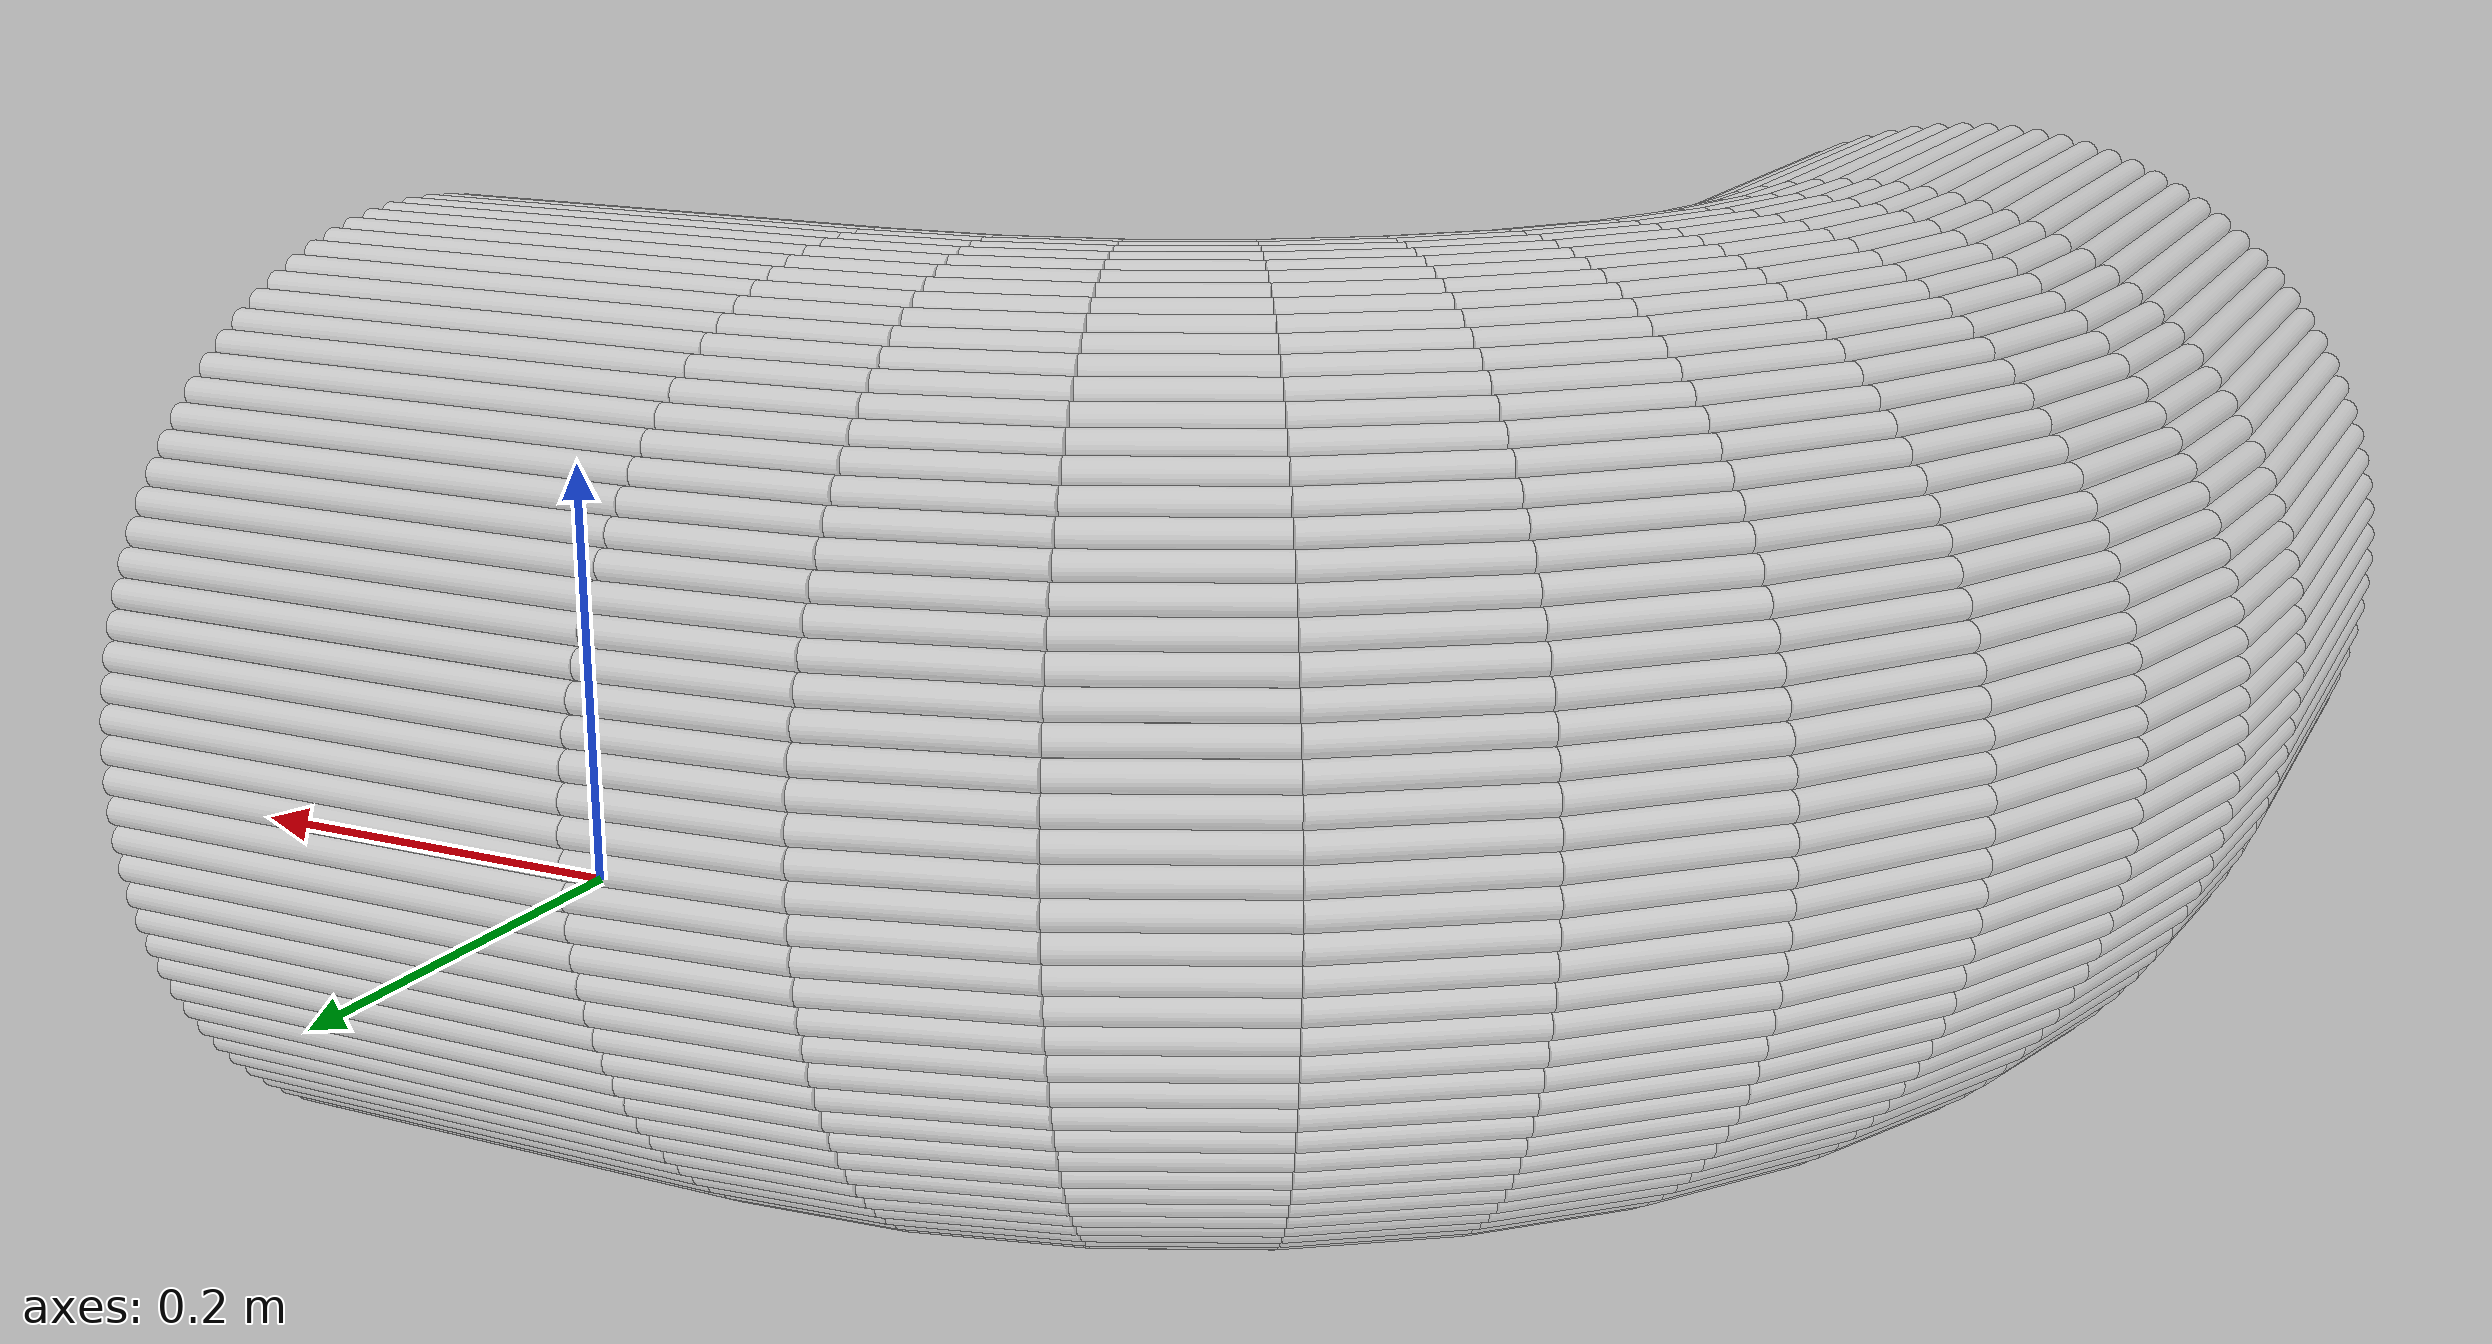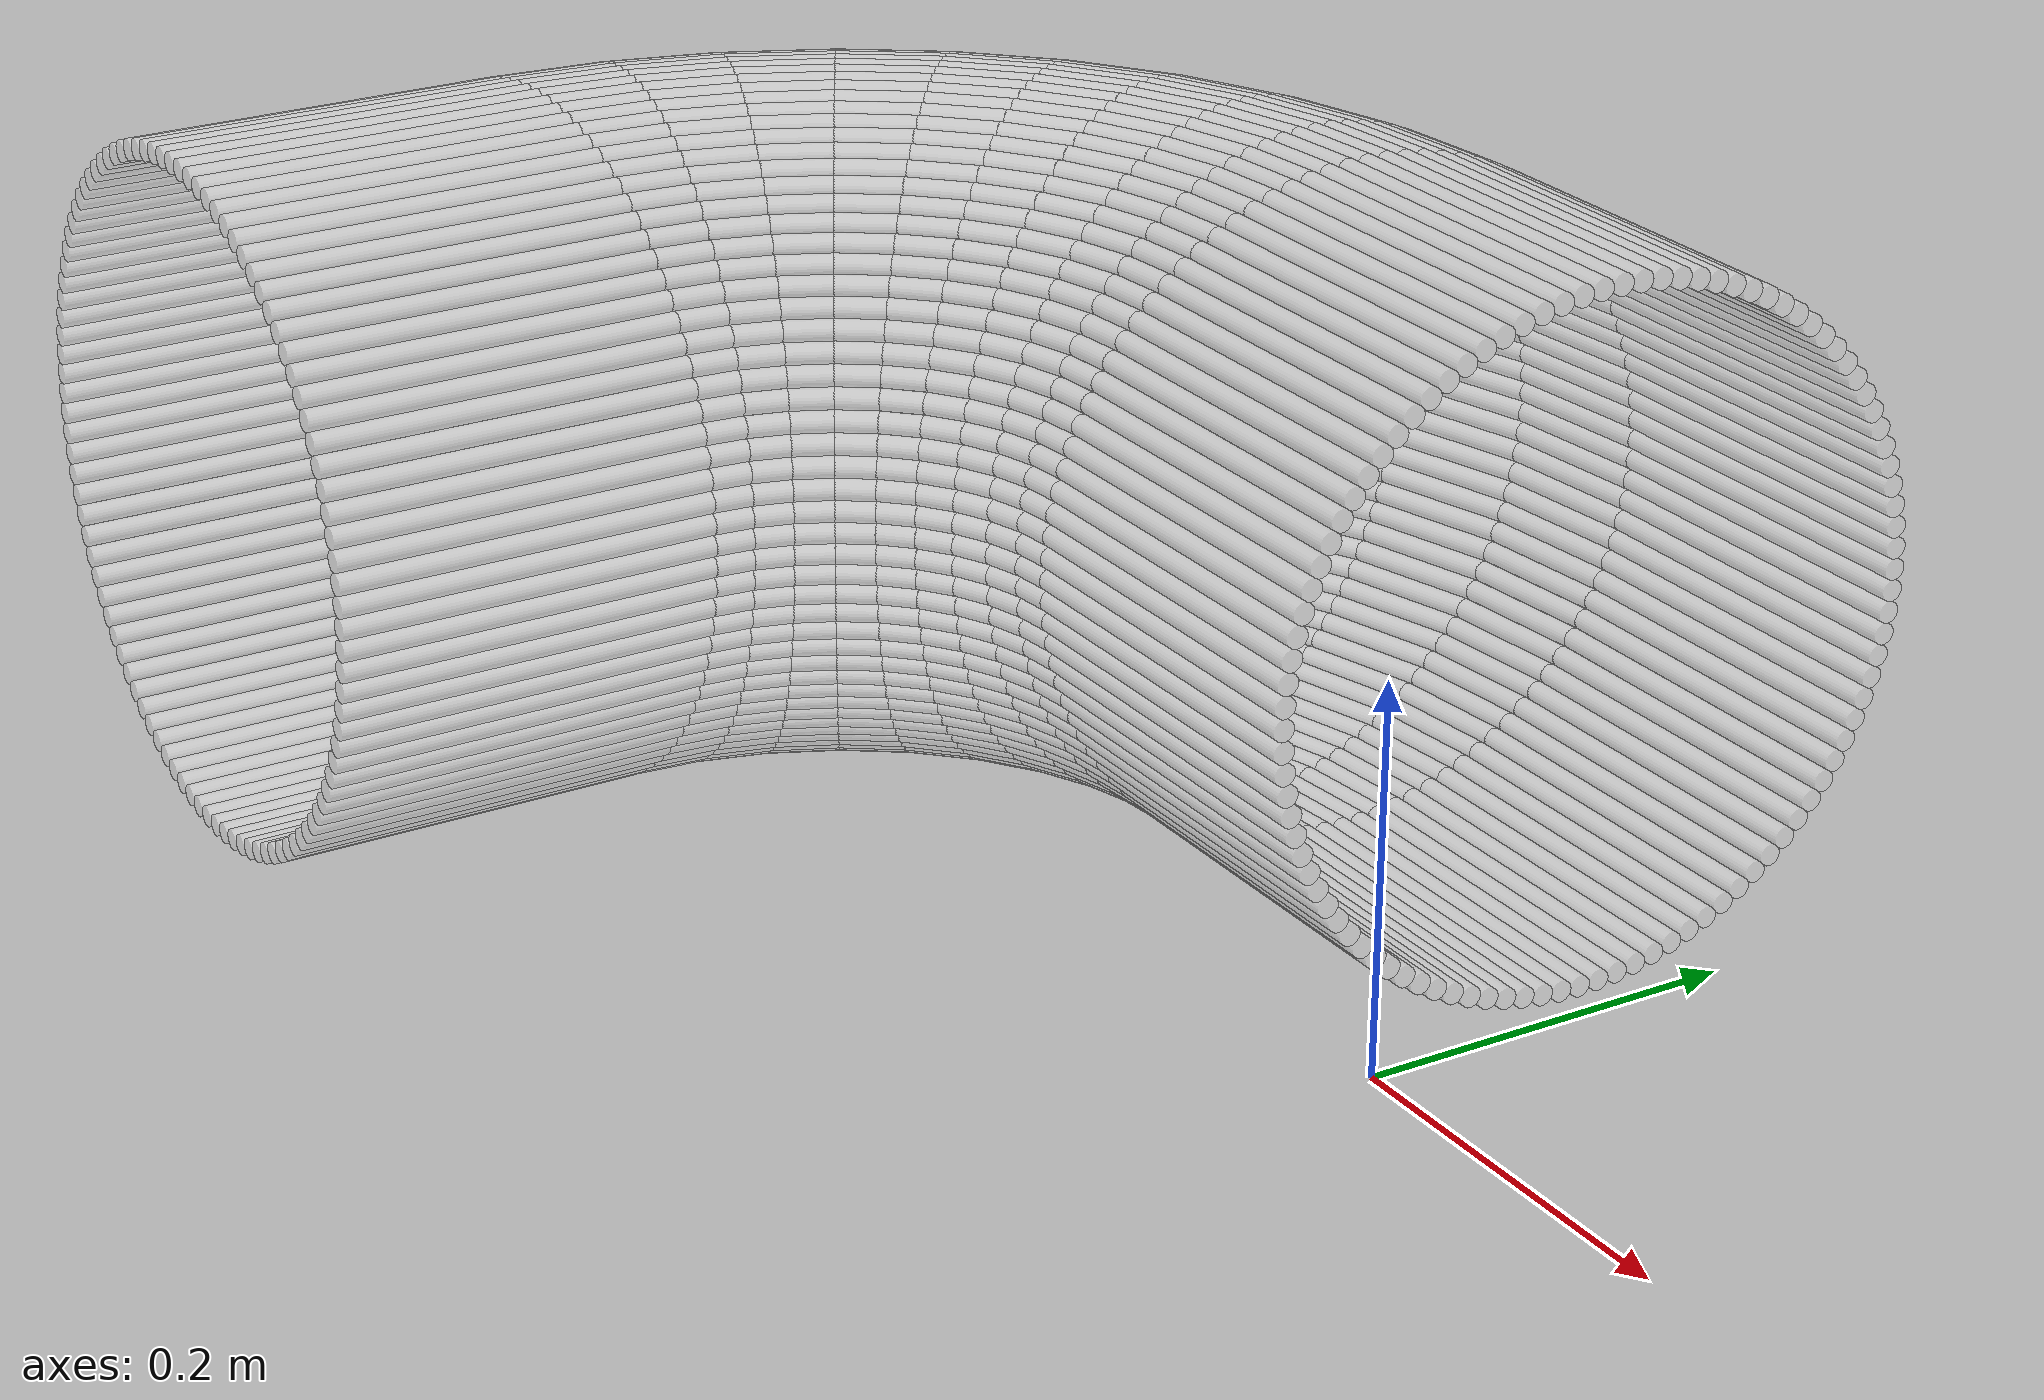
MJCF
<?xml version="1.0" encoding="utf-8"?>
<mujoco>
   <worldbody>
   <body pos="-0.25 -0.14 -0.02" euler="0 0 90">
      <geom euler=" 0 10 0 " fromto="0.48 -0.2 0.18 0.48 0 0.18" rgba="1 1 1 0.35"
            size="0.0056539"
            type="cylinder"/>
      <geom euler=" 0 20 0 " fromto="0.47964 -0.2 0.1913 0.47964 0 0.1913"
            rgba="1 1 1 0.35"
            size="0.0056539"
            type="cylinder"/>
      <geom euler=" 0 30 0 " fromto="0.47858 -0.2 0.20256 0.47858 0 0.20256"
            rgba="1 1 1 0.35"
            size="0.0056539"
            type="cylinder"/>
      <geom euler=" 0 40 0 " fromto="0.47681 -0.2 0.21373 0.47681 0 0.21373"
            rgba="1 1 1 0.35"
            size="0.0056539"
            type="cylinder"/>
      <geom euler=" 0 50 0 " fromto="0.47434 -0.2 0.22476 0.47434 0 0.22476"
            rgba="1 1 1 0.35"
            size="0.0056539"
            type="cylinder"/>
      <geom euler=" 0 60 0 " fromto="0.47119 -0.2 0.23562 0.47119 0 0.23562"
            rgba="1 1 1 0.35"
            size="0.0056539"
            type="cylinder"/>
      <geom euler=" 0 70 0 " fromto="0.46736 -0.2 0.24626 0.46736 0 0.24626"
            rgba="1 1 1 0.35"
            size="0.0056539"
            type="cylinder"/>
      <geom euler=" 0 80 0 " fromto="0.46287 -0.2 0.25664 0.46287 0 0.25664"
            rgba="1 1 1 0.35"
            size="0.0056539"
            type="cylinder"/>
      <geom euler=" 0 90 0 " fromto="0.45774 -0.2 0.26672 0.45774 0 0.26672"
            rgba="1 1 1 0.35"
            size="0.0056539"
            type="cylinder"/>
      <geom euler=" 0 100 0 " fromto="0.45198 -0.2 0.27645 0.45198 0 0.27645"
            rgba="1 1 1 0.35"
            size="0.0056539"
            type="cylinder"/>
      <geom euler=" 0 110 0 " fromto="0.44562 -0.2 0.2858 0.44562 0 0.2858"
            rgba="1 1 1 0.35"
            size="0.0056539"
            type="cylinder"/>
      <geom euler=" 0 120 0 " fromto="0.43869 -0.2 0.29474 0.43869 0 0.29474"
            rgba="1 1 1 0.35"
            size="0.0056539"
            type="cylinder"/>
      <geom euler=" 0 130 0 " fromto="0.43121 -0.2 0.30322 0.43121 0 0.30322"
            rgba="1 1 1 0.35"
            size="0.0056539"
            type="cylinder"/>
      <geom euler=" 0 140 0 " fromto="0.42322 -0.2 0.31121 0.42322 0 0.31121"
            rgba="1 1 1 0.35"
            size="0.0056539"
            type="cylinder"/>
      <geom euler=" 0 150 0 " fromto="0.41474 -0.2 0.31869 0.41474 0 0.31869"
            rgba="1 1 1 0.35"
            size="0.0056539"
            type="cylinder"/>
      <geom euler=" 0 160 0 " fromto="0.4058 -0.2 0.32562 0.4058 0 0.32562"
            rgba="1 1 1 0.35"
            size="0.0056539"
            type="cylinder"/>
      <geom euler=" 0 170 0 " fromto="0.39645 -0.2 0.33198 0.39645 0 0.33198"
            rgba="1 1 1 0.35"
            size="0.0056539"
            type="cylinder"/>
      <geom euler=" 0 180 0 " fromto="0.38672 -0.2 0.33774 0.38672 0 0.33774"
            rgba="1 1 1 0.35"
            size="0.0056539"
            type="cylinder"/>
      <geom euler=" 0 190 0 " fromto="0.37664 -0.2 0.34287 0.37664 0 0.34287"
            rgba="1 1 1 0.35"
            size="0.0056539"
            type="cylinder"/>
      <geom euler=" 0 200 0 " fromto="0.36626 -0.2 0.34736 0.36626 0 0.34736"
            rgba="1 1 1 0.35"
            size="0.0056539"
            type="cylinder"/>
      <geom euler=" 0 210 0 " fromto="0.35562 -0.2 0.35119 0.35562 0 0.35119"
            rgba="1 1 1 0.35"
            size="0.0056539"
            type="cylinder"/>
      <geom euler=" 0 220 0 " fromto="0.34476 -0.2 0.35434 0.34476 0 0.35434"
            rgba="1 1 1 0.35"
            size="0.0056539"
            type="cylinder"/>
      <geom euler=" 0 230 0 " fromto="0.33373 -0.2 0.35681 0.33373 0 0.35681"
            rgba="1 1 1 0.35"
            size="0.0056539"
            type="cylinder"/>
      <geom euler=" 0 240 0 " fromto="0.32256 -0.2 0.35858 0.32256 0 0.35858"
            rgba="1 1 1 0.35"
            size="0.0056539"
            type="cylinder"/>
      <geom euler=" 0 250 0 " fromto="0.3113 -0.2 0.35964 0.3113 0 0.35964"
            rgba="1 1 1 0.35"
            size="0.0056539"
            type="cylinder"/>
      <geom euler=" 0 260 0 " fromto="0.3 -0.2 0.36 0.3 0 0.36" rgba="1 1 1 0.35"
            size="0.0056539"
            type="cylinder"/>
      <geom euler=" 0 270 0 " fromto="0.2887 -0.2 0.35964 0.2887 0 0.35964"
            rgba="1 1 1 0.35"
            size="0.0056539"
            type="cylinder"/>
      <geom euler=" 0 280 0 " fromto="0.27744 -0.2 0.35858 0.27744 0 0.35858"
            rgba="1 1 1 0.35"
            size="0.0056539"
            type="cylinder"/>
      <geom euler=" 0 290 0 " fromto="0.26627 -0.2 0.35681 0.26627 0 0.35681"
            rgba="1 1 1 0.35"
            size="0.0056539"
            type="cylinder"/>
      <geom euler=" 0 300 0 " fromto="0.25524 -0.2 0.35434 0.25524 0 0.35434"
            rgba="1 1 1 0.35"
            size="0.0056539"
            type="cylinder"/>
      <geom euler=" 0 310 0 " fromto="0.24438 -0.2 0.35119 0.24438 0 0.35119"
            rgba="1 1 1 0.35"
            size="0.0056539"
            type="cylinder"/>
      <geom euler=" 0 320 0 " fromto="0.23374 -0.2 0.34736 0.23374 0 0.34736"
            rgba="1 1 1 0.35"
            size="0.0056539"
            type="cylinder"/>
      <geom euler=" 0 330 0 " fromto="0.22336 -0.2 0.34287 0.22336 0 0.34287"
            rgba="1 1 1 0.35"
            size="0.0056539"
            type="cylinder"/>
      <geom euler=" 0 340 0 " fromto="0.21328 -0.2 0.33774 0.21328 0 0.33774"
            rgba="1 1 1 0.35"
            size="0.0056539"
            type="cylinder"/>
      <geom euler=" 0 350 0 " fromto="0.20355 -0.2 0.33198 0.20355 0 0.33198"
            rgba="1 1 1 0.35"
            size="0.0056539"
            type="cylinder"/>
      <geom euler=" 0 360 0 " fromto="0.1942 -0.2 0.32562 0.1942 0 0.32562"
            rgba="1 1 1 0.35"
            size="0.0056539"
            type="cylinder"/>
      <geom euler=" 0 370 0 " fromto="0.18526 -0.2 0.31869 0.18526 0 0.31869"
            rgba="1 1 1 0.35"
            size="0.0056539"
            type="cylinder"/>
      <geom euler=" 0 380 0 " fromto="0.17678 -0.2 0.31121 0.17678 0 0.31121"
            rgba="1 1 1 0.35"
            size="0.0056539"
            type="cylinder"/>
      <geom euler=" 0 390 0 " fromto="0.16879 -0.2 0.30322 0.16879 0 0.30322"
            rgba="1 1 1 0.35"
            size="0.0056539"
            type="cylinder"/>
      <geom euler=" 0 400 0 " fromto="0.16131 -0.2 0.29474 0.16131 0 0.29474"
            rgba="1 1 1 0.35"
            size="0.0056539"
            type="cylinder"/>
      <geom euler=" 0 410 0 " fromto="0.15438 -0.2 0.2858 0.15438 0 0.2858"
            rgba="1 1 1 0.35"
            size="0.0056539"
            type="cylinder"/>
      <geom euler=" 0 420 0 " fromto="0.14802 -0.2 0.27645 0.14802 0 0.27645"
            rgba="1 1 1 0.35"
            size="0.0056539"
            type="cylinder"/>
      <geom euler=" 0 430 0 " fromto="0.14226 -0.2 0.26672 0.14226 0 0.26672"
            rgba="1 1 1 0.35"
            size="0.0056539"
            type="cylinder"/>
      <geom euler=" 0 440 0 " fromto="0.13713 -0.2 0.25664 0.13713 0 0.25664"
            rgba="1 1 1 0.35"
            size="0.0056539"
            type="cylinder"/>
      <geom euler=" 0 450 0 " fromto="0.13264 -0.2 0.24626 0.13264 0 0.24626"
            rgba="1 1 1 0.35"
            size="0.0056539"
            type="cylinder"/>
      <geom euler=" 0 460 0 " fromto="0.12881 -0.2 0.23562 0.12881 0 0.23562"
            rgba="1 1 1 0.35"
            size="0.0056539"
            type="cylinder"/>
      <geom euler=" 0 470 0 " fromto="0.12566 -0.2 0.22476 0.12566 0 0.22476"
            rgba="1 1 1 0.35"
            size="0.0056539"
            type="cylinder"/>
      <geom euler=" 0 480 0 " fromto="0.12319 -0.2 0.21373 0.12319 0 0.21373"
            rgba="1 1 1 0.35"
            size="0.0056539"
            type="cylinder"/>
      <geom euler=" 0 490 0 " fromto="0.12142 -0.2 0.20256 0.12142 0 0.20256"
            rgba="1 1 1 0.35"
            size="0.0056539"
            type="cylinder"/>
      <geom euler=" 0 500 0 " fromto="0.12036 -0.2 0.1913 0.12036 0 0.1913"
            rgba="1 1 1 0.35"
            size="0.0056539"
            type="cylinder"/>
      <geom euler=" 0 510 0 " fromto="0.12 -0.2 0.18 0.12 0 0.18" rgba="1 1 1 0.35"
            size="0.0056539"
            type="cylinder"/>
      <geom euler=" 0 520 0 " fromto="0.12036 -0.2 0.1687 0.12036 0 0.1687"
            rgba="1 1 1 0.35"
            size="0.0056539"
            type="cylinder"/>
      <geom euler=" 0 530 0 " fromto="0.12142 -0.2 0.15744 0.12142 0 0.15744"
            rgba="1 1 1 0.35"
            size="0.0056539"
            type="cylinder"/>
      <geom euler=" 0 540 0 " fromto="0.12319 -0.2 0.14627 0.12319 0 0.14627"
            rgba="1 1 1 0.35"
            size="0.0056539"
            type="cylinder"/>
      <geom euler=" 0 550 0 " fromto="0.12566 -0.2 0.13524 0.12566 0 0.13524"
            rgba="1 1 1 0.35"
            size="0.0056539"
            type="cylinder"/>
      <geom euler=" 0 560 0 " fromto="0.12881 -0.2 0.12438 0.12881 0 0.12438"
            rgba="1 1 1 0.35"
            size="0.0056539"
            type="cylinder"/>
      <geom euler=" 0 570 0 " fromto="0.13264 -0.2 0.11374 0.13264 0 0.11374"
            rgba="1 1 1 0.35"
            size="0.0056539"
            type="cylinder"/>
      <geom euler=" 0 580 0 " fromto="0.13713 -0.2 0.10336 0.13713 0 0.10336"
            rgba="1 1 1 0.35"
            size="0.0056539"
            type="cylinder"/>
      <geom euler=" 0 590 0 " fromto="0.14226 -0.2 0.093284 0.14226 0 0.093284"
            rgba="1 1 1 0.35"
            size="0.0056539"
            type="cylinder"/>
      <geom euler=" 0 600 0 " fromto="0.14802 -0.2 0.083551 0.14802 0 0.083551"
            rgba="1 1 1 0.35"
            size="0.0056539"
            type="cylinder"/>
      <geom euler=" 0 610 0 " fromto="0.15438 -0.2 0.074199 0.15438 0 0.074199"
            rgba="1 1 1 0.35"
            size="0.0056539"
            type="cylinder"/>
      <geom euler=" 0 620 0 " fromto="0.16131 -0.2 0.065264 0.16131 0 0.065264"
            rgba="1 1 1 0.35"
            size="0.0056539"
            type="cylinder"/>
      <geom euler=" 0 630 0 " fromto="0.16879 -0.2 0.056782 0.16879 0 0.056782"
            rgba="1 1 1 0.35"
            size="0.0056539"
            type="cylinder"/>
      <geom euler=" 0 640 0 " fromto="0.17678 -0.2 0.048786 0.17678 0 0.048786"
            rgba="1 1 1 0.35"
            size="0.0056539"
            type="cylinder"/>
      <geom euler=" 0 650 0 " fromto="0.18526 -0.2 0.041308 0.18526 0 0.041308"
            rgba="1 1 1 0.35"
            size="0.0056539"
            type="cylinder"/>
      <geom euler=" 0 660 0 " fromto="0.1942 -0.2 0.034377 0.1942 0 0.034377"
            rgba="1 1 1 0.35"
            size="0.0056539"
            type="cylinder"/>
      <geom euler=" 0 670 0 " fromto="0.20355 -0.2 0.028021 0.20355 0 0.028021"
            rgba="1 1 1 0.35"
            size="0.0056539"
            type="cylinder"/>
      <geom euler=" 0 680 0 " fromto="0.21328 -0.2 0.022265 0.21328 0 0.022265"
            rgba="1 1 1 0.35"
            size="0.0056539"
            type="cylinder"/>
      <geom euler=" 0 690 0 " fromto="0.22336 -0.2 0.017131 0.22336 0 0.017131"
            rgba="1 1 1 0.35"
            size="0.0056539"
            type="cylinder"/>
      <geom euler=" 0 700 0 " fromto="0.23374 -0.2 0.01264 0.23374 0 0.01264"
            rgba="1 1 1 0.35"
            size="0.0056539"
            type="cylinder"/>
      <geom euler=" 0 710 0 " fromto="0.24438 -0.2 0.0088098 0.24438 0 0.0088098"
            rgba="1 1 1 0.35"
            size="0.0056539"
            type="cylinder"/>
      <geom euler=" 0 720 0 " fromto="0.25524 -0.2 0.005655 0.25524 0 0.005655"
            rgba="1 1 1 0.35"
            size="0.0056539"
            type="cylinder"/>
      <geom euler=" 0 730 0 " fromto="0.26627 -0.2 0.0031883 0.26627 0 0.0031883"
            rgba="1 1 1 0.35"
            size="0.0056539"
            type="cylinder"/>
      <geom euler=" 0 740 0 " fromto="0.27744 -0.2 0.0014194 0.27744 0 0.0014194"
            rgba="1 1 1 0.35"
            size="0.0056539"
            type="cylinder"/>
      <geom euler=" 0 750 0 " fromto="0.2887 -0.2 0.00035519 0.2887 0 0.00035519"
            rgba="1 1 1 0.35"
            size="0.0056539"
            type="cylinder"/>
      <geom euler=" 0 760 0 " fromto="0.3 -0.2 0 0.3 0 0" rgba="1 1 1 0.35"
            size="0.0056539"
            type="cylinder"/>
      <geom euler=" 0 770 0 " fromto="0.3113 -0.2 0.00035519 0.3113 0 0.00035519"
            rgba="1 1 1 0.35"
            size="0.0056539"
            type="cylinder"/>
      <geom euler=" 0 780 0 " fromto="0.32256 -0.2 0.0014194 0.32256 0 0.0014194"
            rgba="1 1 1 0.35"
            size="0.0056539"
            type="cylinder"/>
      <geom euler=" 0 790 0 " fromto="0.33373 -0.2 0.0031883 0.33373 0 0.0031883"
            rgba="1 1 1 0.35"
            size="0.0056539"
            type="cylinder"/>
      <geom euler=" 0 800 0 " fromto="0.34476 -0.2 0.005655 0.34476 0 0.005655"
            rgba="1 1 1 0.35"
            size="0.0056539"
            type="cylinder"/>
      <geom euler=" 0 810 0 " fromto="0.35562 -0.2 0.0088098 0.35562 0 0.0088098"
            rgba="1 1 1 0.35"
            size="0.0056539"
            type="cylinder"/>
      <geom euler=" 0 820 0 " fromto="0.36626 -0.2 0.01264 0.36626 0 0.01264"
            rgba="1 1 1 0.35"
            size="0.0056539"
            type="cylinder"/>
      <geom euler=" 0 830 0 " fromto="0.37664 -0.2 0.017131 0.37664 0 0.017131"
            rgba="1 1 1 0.35"
            size="0.0056539"
            type="cylinder"/>
      <geom euler=" 0 840 0 " fromto="0.38672 -0.2 0.022265 0.38672 0 0.022265"
            rgba="1 1 1 0.35"
            size="0.0056539"
            type="cylinder"/>
      <geom euler=" 0 850 0 " fromto="0.39645 -0.2 0.028021 0.39645 0 0.028021"
            rgba="1 1 1 0.35"
            size="0.0056539"
            type="cylinder"/>
      <geom euler=" 0 860 0 " fromto="0.4058 -0.2 0.034377 0.4058 0 0.034377"
            rgba="1 1 1 0.35"
            size="0.0056539"
            type="cylinder"/>
      <geom euler=" 0 870 0 " fromto="0.41474 -0.2 0.041308 0.41474 0 0.041308"
            rgba="1 1 1 0.35"
            size="0.0056539"
            type="cylinder"/>
      <geom euler=" 0 880 0 " fromto="0.42322 -0.2 0.048786 0.42322 0 0.048786"
            rgba="1 1 1 0.35"
            size="0.0056539"
            type="cylinder"/>
      <geom euler=" 0 890 0 " fromto="0.43121 -0.2 0.056782 0.43121 0 0.056782"
            rgba="1 1 1 0.35"
            size="0.0056539"
            type="cylinder"/>
      <geom euler=" 0 900 0 " fromto="0.43869 -0.2 0.065264 0.43869 0 0.065264"
            rgba="1 1 1 0.35"
            size="0.0056539"
            type="cylinder"/>
      <geom euler=" 0 910 0 " fromto="0.44562 -0.2 0.074199 0.44562 0 0.074199"
            rgba="1 1 1 0.35"
            size="0.0056539"
            type="cylinder"/>
      <geom euler=" 0 920 0 " fromto="0.45198 -0.2 0.083551 0.45198 0 0.083551"
            rgba="1 1 1 0.35"
            size="0.0056539"
            type="cylinder"/>
      <geom euler=" 0 930 0 " fromto="0.45774 -0.2 0.093284 0.45774 0 0.093284"
            rgba="1 1 1 0.35"
            size="0.0056539"
            type="cylinder"/>
      <geom euler=" 0 940 0 " fromto="0.46287 -0.2 0.10336 0.46287 0 0.10336"
            rgba="1 1 1 0.35"
            size="0.0056539"
            type="cylinder"/>
      <geom euler=" 0 950 0 " fromto="0.46736 -0.2 0.11374 0.46736 0 0.11374"
            rgba="1 1 1 0.35"
            size="0.0056539"
            type="cylinder"/>
      <geom euler=" 0 960 0 " fromto="0.47119 -0.2 0.12438 0.47119 0 0.12438"
            rgba="1 1 1 0.35"
            size="0.0056539"
            type="cylinder"/>
      <geom euler=" 0 970 0 " fromto="0.47434 -0.2 0.13524 0.47434 0 0.13524"
            rgba="1 1 1 0.35"
            size="0.0056539"
            type="cylinder"/>
      <geom euler=" 0 980 0 " fromto="0.47681 -0.2 0.14627 0.47681 0 0.14627"
            rgba="1 1 1 0.35"
            size="0.0056539"
            type="cylinder"/>
      <geom euler=" 0 990 0 " fromto="0.47858 -0.2 0.15744 0.47858 0 0.15744"
            rgba="1 1 1 0.35"
            size="0.0056539"
            type="cylinder"/>
      <geom euler=" 0 1000 0 " fromto="0.47964 -0.2 0.1687 0.47964 0 0.1687"
            rgba="1 1 1 0.35"
            size="0.0056539"
            type="cylinder"/>
      <geom euler=" 0 10 0 " fromto="0.48 0 0.18 0.47271 0.083351 0.18" rgba="1 1 1 0.35"
            size="0.0056539"
            type="cylinder"/>
      <geom euler=" 0 20 0 " fromto="0.47964 0 0.1913 0.47236 0.083289 0.1913"
            rgba="1 1 1 0.35"
            size="0.0056539"
            type="cylinder"/>
      <geom euler=" 0 30 0 " fromto="0.47858 0 0.20256 0.47131 0.083105 0.20256"
            rgba="1 1 1 0.35"
            size="0.0056539"
            type="cylinder"/>
      <geom euler=" 0 40 0 " fromto="0.47681 0 0.21373 0.46957 0.082797 0.21373"
            rgba="1 1 1 0.35"
            size="0.0056539"
            type="cylinder"/>
      <geom euler=" 0 50 0 " fromto="0.47434 0 0.22476 0.46714 0.082369 0.22476"
            rgba="1 1 1 0.35"
            size="0.0056539"
            type="cylinder"/>
      <geom euler=" 0 60 0 " fromto="0.47119 0 0.23562 0.46403 0.081821 0.23562"
            rgba="1 1 1 0.35"
            size="0.0056539"
            type="cylinder"/>
      <geom euler=" 0 70 0 " fromto="0.46736 0 0.24626 0.46026 0.081156 0.24626"
            rgba="1 1 1 0.35"
            size="0.0056539"
            type="cylinder"/>
      <geom euler=" 0 80 0 " fromto="0.46287 0 0.25664 0.45584 0.080376 0.25664"
            rgba="1 1 1 0.35"
            size="0.0056539"
            type="cylinder"/>
      <geom euler=" 0 90 0 " fromto="0.45774 0 0.26672 0.45078 0.079485 0.26672"
            rgba="1 1 1 0.35"
            size="0.0056539"
            type="cylinder"/>
      <geom euler=" 0 100 0 " fromto="0.45198 0 0.27645 0.44511 0.078485 0.27645"
            rgba="1 1 1 0.35"
            size="0.0056539"
            type="cylinder"/>
      <geom euler=" 0 110 0 " fromto="0.44562 0 0.2858 0.43885 0.077382 0.2858"
            rgba="1 1 1 0.35"
            size="0.0056539"
            type="cylinder"/>
      <geom euler=" 0 120 0 " fromto="0.43869 0 0.29474 0.43203 0.076178 0.29474"
            rgba="1 1 1 0.35"
            size="0.0056539"
            type="cylinder"/>
      <geom euler=" 0 130 0 " fromto="0.43121 0 0.30322 0.42466 0.07488 0.30322"
            rgba="1 1 1 0.35"
            size="0.0056539"
            type="cylinder"/>
      <geom euler=" 0 140 0 " fromto="0.42322 0 0.31121 0.41679 0.073491 0.31121"
            rgba="1 1 1 0.35"
            size="0.0056539"
            type="cylinder"/>
      <geom euler=" 0 150 0 " fromto="0.41474 0 0.31869 0.40844 0.072018 0.31869"
            rgba="1 1 1 0.35"
            size="0.0056539"
            type="cylinder"/>
      <geom euler=" 0 160 0 " fromto="0.4058 0 0.32562 0.39964 0.070467 0.32562"
            rgba="1 1 1 0.35"
            size="0.0056539"
            type="cylinder"/>
      <geom euler=" 0 170 0 " fromto="0.39645 0 0.33198 0.39043 0.068843 0.33198"
            rgba="1 1 1 0.35"
            size="0.0056539"
            type="cylinder"/>
      <geom euler=" 0 180 0 " fromto="0.38672 0 0.33774 0.38084 0.067152 0.33774"
            rgba="1 1 1 0.35"
            size="0.0056539"
            type="cylinder"/>
      <geom euler=" 0 190 0 " fromto="0.37664 0 0.34287 0.37092 0.065403 0.34287"
            rgba="1 1 1 0.35"
            size="0.0056539"
            type="cylinder"/>
      <geom euler=" 0 200 0 " fromto="0.36626 0 0.34736 0.3607 0.063601 0.34736"
            rgba="1 1 1 0.35"
            size="0.0056539"
            type="cylinder"/>
      <geom euler=" 0 210 0 " fromto="0.35562 0 0.35119 0.35022 0.061753 0.35119"
            rgba="1 1 1 0.35"
            size="0.0056539"
            type="cylinder"/>
      <geom euler=" 0 220 0 " fromto="0.34476 0 0.35434 0.33953 0.059868 0.35434"
            rgba="1 1 1 0.35"
            size="0.0056539"
            type="cylinder"/>
      <geom euler=" 0 230 0 " fromto="0.33373 0 0.35681 0.32866 0.057951 0.35681"
            rgba="1 1 1 0.35"
            size="0.0056539"
            type="cylinder"/>
      <geom euler=" 0 240 0 " fromto="0.32256 0 0.35858 0.31766 0.056012 0.35858"
            rgba="1 1 1 0.35"
            size="0.0056539"
            type="cylinder"/>
      <geom euler=" 0 250 0 " fromto="0.3113 0 0.35964 0.30657 0.054057 0.35964"
            rgba="1 1 1 0.35"
            size="0.0056539"
            type="cylinder"/>
      <geom euler=" 0 260 0 " fromto="0.3 0 0.36 0.29544 0.052094 0.36" rgba="1 1 1 0.35"
            size="0.0056539"
            type="cylinder"/>
      <geom euler=" 0 270 0 " fromto="0.2887 0 0.35964 0.28431 0.050132 0.35964"
            rgba="1 1 1 0.35"
            size="0.0056539"
            type="cylinder"/>
      <geom euler=" 0 280 0 " fromto="0.27744 0 0.35858 0.27323 0.048177 0.35858"
            rgba="1 1 1 0.35"
            size="0.0056539"
            type="cylinder"/>
      <geom euler=" 0 290 0 " fromto="0.26627 0 0.35681 0.26223 0.046238 0.35681"
            rgba="1 1 1 0.35"
            size="0.0056539"
            type="cylinder"/>
      <geom euler=" 0 300 0 " fromto="0.25524 0 0.35434 0.25136 0.044321 0.35434"
            rgba="1 1 1 0.35"
            size="0.0056539"
            type="cylinder"/>
      <geom euler=" 0 310 0 " fromto="0.24438 0 0.35119 0.24066 0.042436 0.35119"
            rgba="1 1 1 0.35"
            size="0.0056539"
            type="cylinder"/>
      <geom euler=" 0 320 0 " fromto="0.23374 0 0.34736 0.23019 0.040588 0.34736"
            rgba="1 1 1 0.35"
            size="0.0056539"
            type="cylinder"/>
      <geom euler=" 0 330 0 " fromto="0.22336 0 0.34287 0.21997 0.038786 0.34287"
            rgba="1 1 1 0.35"
            size="0.0056539"
            type="cylinder"/>
      <geom euler=" 0 340 0 " fromto="0.21328 0 0.33774 0.21004 0.037036 0.33774"
            rgba="1 1 1 0.35"
            size="0.0056539"
            type="cylinder"/>
      <geom euler=" 0 350 0 " fromto="0.20355 0 0.33198 0.20046 0.035346 0.33198"
            rgba="1 1 1 0.35"
            size="0.0056539"
            type="cylinder"/>
      <geom euler=" 0 360 0 " fromto="0.1942 0 0.32562 0.19125 0.033722 0.32562"
            rgba="1 1 1 0.35"
            size="0.0056539"
            type="cylinder"/>
      <geom euler=" 0 370 0 " fromto="0.18526 0 0.31869 0.18245 0.032171 0.31869"
            rgba="1 1 1 0.35"
            size="0.0056539"
            type="cylinder"/>
      <geom euler=" 0 380 0 " fromto="0.17678 0 0.31121 0.1741 0.030698 0.31121"
            rgba="1 1 1 0.35"
            size="0.0056539"
            type="cylinder"/>
      <geom euler=" 0 390 0 " fromto="0.16879 0 0.30322 0.16622 0.029309 0.30322"
            rgba="1 1 1 0.35"
            size="0.0056539"
            type="cylinder"/>
      <geom euler=" 0 400 0 " fromto="0.16131 0 0.29474 0.15886 0.028011 0.29474"
            rgba="1 1 1 0.35"
            size="0.0056539"
            type="cylinder"/>
      <geom euler=" 0 410 0 " fromto="0.15438 0 0.2858 0.15203 0.026807 0.2858"
            rgba="1 1 1 0.35"
            size="0.0056539"
            type="cylinder"/>
      <geom euler=" 0 420 0 " fromto="0.14802 0 0.27645 0.14577 0.025704 0.27645"
            rgba="1 1 1 0.35"
            size="0.0056539"
            type="cylinder"/>
      <geom euler=" 0 430 0 " fromto="0.14226 0 0.26672 0.1401 0.024704 0.26672"
            rgba="1 1 1 0.35"
            size="0.0056539"
            type="cylinder"/>
      <geom euler=" 0 440 0 " fromto="0.13713 0 0.25664 0.13505 0.023813 0.25664"
            rgba="1 1 1 0.35"
            size="0.0056539"
            type="cylinder"/>
      <geom euler=" 0 450 0 " fromto="0.13264 0 0.24626 0.13063 0.023033 0.24626"
            rgba="1 1 1 0.35"
            size="0.0056539"
            type="cylinder"/>
      <geom euler=" 0 460 0 " fromto="0.12881 0 0.23562 0.12685 0.022368 0.23562"
            rgba="1 1 1 0.35"
            size="0.0056539"
            type="cylinder"/>
      <geom euler=" 0 470 0 " fromto="0.12566 0 0.22476 0.12375 0.02182 0.22476"
            rgba="1 1 1 0.35"
            size="0.0056539"
            type="cylinder"/>
      <geom euler=" 0 480 0 " fromto="0.12319 0 0.21373 0.12132 0.021391 0.21373"
            rgba="1 1 1 0.35"
            size="0.0056539"
            type="cylinder"/>
      <geom euler=" 0 490 0 " fromto="0.12142 0 0.20256 0.11957 0.021084 0.20256"
            rgba="1 1 1 0.35"
            size="0.0056539"
            type="cylinder"/>
      <geom euler=" 0 500 0 " fromto="0.12036 0 0.1913 0.11853 0.020899 0.1913"
            rgba="1 1 1 0.35"
            size="0.0056539"
            type="cylinder"/>
      <geom euler=" 0 510 0 " fromto="0.12 0 0.18 0.11818 0.020838 0.18" rgba="1 1 1 0.35"
            size="0.0056539"
            type="cylinder"/>
      <geom euler=" 0 520 0 " fromto="0.12036 0 0.1687 0.11853 0.020899 0.1687"
            rgba="1 1 1 0.35"
            size="0.0056539"
            type="cylinder"/>
      <geom euler=" 0 530 0 " fromto="0.12142 0 0.15744 0.11957 0.021084 0.15744"
            rgba="1 1 1 0.35"
            size="0.0056539"
            type="cylinder"/>
      <geom euler=" 0 540 0 " fromto="0.12319 0 0.14627 0.12132 0.021391 0.14627"
            rgba="1 1 1 0.35"
            size="0.0056539"
            type="cylinder"/>
      <geom euler=" 0 550 0 " fromto="0.12566 0 0.13524 0.12375 0.02182 0.13524"
            rgba="1 1 1 0.35"
            size="0.0056539"
            type="cylinder"/>
      <geom euler=" 0 560 0 " fromto="0.12881 0 0.12438 0.12685 0.022368 0.12438"
            rgba="1 1 1 0.35"
            size="0.0056539"
            type="cylinder"/>
      <geom euler=" 0 570 0 " fromto="0.13264 0 0.11374 0.13063 0.023033 0.11374"
            rgba="1 1 1 0.35"
            size="0.0056539"
            type="cylinder"/>
      <geom euler=" 0 580 0 " fromto="0.13713 0 0.10336 0.13505 0.023813 0.10336"
            rgba="1 1 1 0.35"
            size="0.0056539"
            type="cylinder"/>
      <geom euler=" 0 590 0 " fromto="0.14226 0 0.093284 0.1401 0.024704 0.093284"
            rgba="1 1 1 0.35"
            size="0.0056539"
            type="cylinder"/>
      <geom euler=" 0 600 0 " fromto="0.14802 0 0.083551 0.14577 0.025704 0.083551"
            rgba="1 1 1 0.35"
            size="0.0056539"
            type="cylinder"/>
      <geom euler=" 0 610 0 " fromto="0.15438 0 0.074199 0.15203 0.026807 0.074199"
            rgba="1 1 1 0.35"
            size="0.0056539"
            type="cylinder"/>
      <geom euler=" 0 620 0 " fromto="0.16131 0 0.065264 0.15886 0.028011 0.065264"
            rgba="1 1 1 0.35"
            size="0.0056539"
            type="cylinder"/>
      <geom euler=" 0 630 0 " fromto="0.16879 0 0.056782 0.16622 0.029309 0.056782"
            rgba="1 1 1 0.35"
            size="0.0056539"
            type="cylinder"/>
      <geom euler=" 0 640 0 " fromto="0.17678 0 0.048786 0.1741 0.030698 0.048786"
            rgba="1 1 1 0.35"
            size="0.0056539"
            type="cylinder"/>
      <geom euler=" 0 650 0 " fromto="0.18526 0 0.041308 0.18245 0.032171 0.041308"
            rgba="1 1 1 0.35"
            size="0.0056539"
            type="cylinder"/>
      <geom euler=" 0 660 0 " fromto="0.1942 0 0.034377 0.19125 0.033722 0.034377"
            rgba="1 1 1 0.35"
            size="0.0056539"
            type="cylinder"/>
      <geom euler=" 0 670 0 " fromto="0.20355 0 0.028021 0.20046 0.035346 0.028021"
            rgba="1 1 1 0.35"
            size="0.0056539"
            type="cylinder"/>
      <geom euler=" 0 680 0 " fromto="0.21328 0 0.022265 0.21004 0.037036 0.022265"
            rgba="1 1 1 0.35"
            size="0.0056539"
            type="cylinder"/>
      <geom euler=" 0 690 0 " fromto="0.22336 0 0.017131 0.21997 0.038786 0.017131"
            rgba="1 1 1 0.35"
            size="0.0056539"
            type="cylinder"/>
      <geom euler=" 0 700 0 " fromto="0.23374 0 0.01264 0.23019 0.040588 0.01264"
            rgba="1 1 1 0.35"
            size="0.0056539"
            type="cylinder"/>
      <geom euler=" 0 710 0 " fromto="0.24438 0 0.0088098 0.24066 0.042436 0.0088098"
            rgba="1 1 1 0.35"
            size="0.0056539"
            type="cylinder"/>
      <geom euler=" 0 720 0 " fromto="0.25524 0 0.005655 0.25136 0.044321 0.005655"
            rgba="1 1 1 0.35"
            size="0.0056539"
            type="cylinder"/>
      <geom euler=" 0 730 0 " fromto="0.26627 0 0.0031883 0.26223 0.046238 0.0031883"
            rgba="1 1 1 0.35"
            size="0.0056539"
            type="cylinder"/>
      <geom euler=" 0 740 0 " fromto="0.27744 0 0.0014194 0.27323 0.048177 0.0014194"
            rgba="1 1 1 0.35"
            size="0.0056539"
            type="cylinder"/>
      <geom euler=" 0 750 0 " fromto="0.2887 0 0.00035519 0.28431 0.050132 0.00035519"
            rgba="1 1 1 0.35"
            size="0.0056539"
            type="cylinder"/>
      <geom euler=" 0 760 0 " fromto="0.3 0 0 0.29544 0.052094 0" rgba="1 1 1 0.35"
            size="0.0056539"
            type="cylinder"/>
      <geom euler=" 0 770 0 " fromto="0.3113 0 0.00035519 0.30657 0.054057 0.00035519"
            rgba="1 1 1 0.35"
            size="0.0056539"
            type="cylinder"/>
      <geom euler=" 0 780 0 " fromto="0.32256 0 0.0014194 0.31766 0.056012 0.0014194"
            rgba="1 1 1 0.35"
            size="0.0056539"
            type="cylinder"/>
      <geom euler=" 0 790 0 " fromto="0.33373 0 0.0031883 0.32866 0.057951 0.0031883"
            rgba="1 1 1 0.35"
            size="0.0056539"
            type="cylinder"/>
      <geom euler=" 0 800 0 " fromto="0.34476 0 0.005655 0.33953 0.059868 0.005655"
            rgba="1 1 1 0.35"
            size="0.0056539"
            type="cylinder"/>
      <geom euler=" 0 810 0 " fromto="0.35562 0 0.0088098 0.35022 0.061753 0.0088098"
            rgba="1 1 1 0.35"
            size="0.0056539"
            type="cylinder"/>
      <geom euler=" 0 820 0 " fromto="0.36626 0 0.01264 0.3607 0.063601 0.01264"
            rgba="1 1 1 0.35"
            size="0.0056539"
            type="cylinder"/>
      <geom euler=" 0 830 0 " fromto="0.37664 0 0.017131 0.37092 0.065403 0.017131"
            rgba="1 1 1 0.35"
            size="0.0056539"
            type="cylinder"/>
      <geom euler=" 0 840 0 " fromto="0.38672 0 0.022265 0.38084 0.067152 0.022265"
            rgba="1 1 1 0.35"
            size="0.0056539"
            type="cylinder"/>
      <geom euler=" 0 850 0 " fromto="0.39645 0 0.028021 0.39043 0.068843 0.028021"
            rgba="1 1 1 0.35"
            size="0.0056539"
            type="cylinder"/>
      <geom euler=" 0 860 0 " fromto="0.4058 0 0.034377 0.39964 0.070467 0.034377"
            rgba="1 1 1 0.35"
            size="0.0056539"
            type="cylinder"/>
      <geom euler=" 0 870 0 " fromto="0.41474 0 0.041308 0.40844 0.072018 0.041308"
            rgba="1 1 1 0.35"
            size="0.0056539"
            type="cylinder"/>
      <geom euler=" 0 880 0 " fromto="0.42322 0 0.048786 0.41679 0.073491 0.048786"
            rgba="1 1 1 0.35"
            size="0.0056539"
            type="cylinder"/>
      <geom euler=" 0 890 0 " fromto="0.43121 0 0.056782 0.42466 0.07488 0.056782"
            rgba="1 1 1 0.35"
            size="0.0056539"
            type="cylinder"/>
      <geom euler=" 0 900 0 " fromto="0.43869 0 0.065264 0.43203 0.076178 0.065264"
            rgba="1 1 1 0.35"
            size="0.0056539"
            type="cylinder"/>
      <geom euler=" 0 910 0 " fromto="0.44562 0 0.074199 0.43885 0.077382 0.074199"
            rgba="1 1 1 0.35"
            size="0.0056539"
            type="cylinder"/>
      <geom euler=" 0 920 0 " fromto="0.45198 0 0.083551 0.44511 0.078485 0.083551"
            rgba="1 1 1 0.35"
            size="0.0056539"
            type="cylinder"/>
      <geom euler=" 0 930 0 " fromto="0.45774 0 0.093284 0.45078 0.079485 0.093284"
            rgba="1 1 1 0.35"
            size="0.0056539"
            type="cylinder"/>
      <geom euler=" 0 940 0 " fromto="0.46287 0 0.10336 0.45584 0.080376 0.10336"
            rgba="1 1 1 0.35"
            size="0.0056539"
            type="cylinder"/>
      <geom euler=" 0 950 0 " fromto="0.46736 0 0.11374 0.46026 0.081156 0.11374"
            rgba="1 1 1 0.35"
            size="0.0056539"
            type="cylinder"/>
      <geom euler=" 0 960 0 " fromto="0.47119 0 0.12438 0.46403 0.081821 0.12438"
            rgba="1 1 1 0.35"
            size="0.0056539"
            type="cylinder"/>
      <geom euler=" 0 970 0 " fromto="0.47434 0 0.13524 0.46714 0.082369 0.13524"
            rgba="1 1 1 0.35"
            size="0.0056539"
            type="cylinder"/>
      <geom euler=" 0 980 0 " fromto="0.47681 0 0.14627 0.46957 0.082797 0.14627"
            rgba="1 1 1 0.35"
            size="0.0056539"
            type="cylinder"/>
      <geom euler=" 0 990 0 " fromto="0.47858 0 0.15744 0.47131 0.083105 0.15744"
            rgba="1 1 1 0.35"
            size="0.0056539"
            type="cylinder"/>
      <geom euler=" 0 1000 0 " fromto="0.47964 0 0.1687 0.47236 0.083289 0.1687"
            rgba="1 1 1 0.35"
            size="0.0056539"
            type="cylinder"/>
      <geom euler=" 0 10 0 " fromto="0.47271 0.083351 0.18 0.45105 0.16417 0.18"
            rgba="1 1 1 0.35"
            size="0.0056539"
            type="cylinder"/>
      <geom euler=" 0 20 0 " fromto="0.47236 0.083289 0.1913 0.45072 0.16405 0.1913"
            rgba="1 1 1 0.35"
            size="0.0056539"
            type="cylinder"/>
      <geom euler=" 0 30 0 " fromto="0.47131 0.083105 0.20256 0.44972 0.16368 0.20256"
            rgba="1 1 1 0.35"
            size="0.0056539"
            type="cylinder"/>
      <geom euler=" 0 40 0 " fromto="0.46957 0.082797 0.21373 0.44806 0.16308 0.21373"
            rgba="1 1 1 0.35"
            size="0.0056539"
            type="cylinder"/>
      <geom euler=" 0 50 0 " fromto="0.46714 0.082369 0.22476 0.44574 0.16224 0.22476"
            rgba="1 1 1 0.35"
            size="0.0056539"
            type="cylinder"/>
      <geom euler=" 0 60 0 " fromto="0.46403 0.081821 0.23562 0.44277 0.16116 0.23562"
            rgba="1 1 1 0.35"
            size="0.0056539"
            type="cylinder"/>
      <geom euler=" 0 70 0 " fromto="0.46026 0.081156 0.24626 0.43917 0.15985 0.24626"
            rgba="1 1 1 0.35"
            size="0.0056539"
            type="cylinder"/>
      <geom euler=" 0 80 0 " fromto="0.45584 0.080376 0.25664 0.43495 0.15831 0.25664"
            rgba="1 1 1 0.35"
            size="0.0056539"
            type="cylinder"/>
      <geom euler=" 0 90 0 " fromto="0.45078 0.079485 0.26672 0.43013 0.15655 0.26672"
            rgba="1 1 1 0.35"
            size="0.0056539"
            type="cylinder"/>
      <geom euler=" 0 100 0 " fromto="0.44511 0.078485 0.27645 0.42472 0.15459 0.27645"
            rgba="1 1 1 0.35"
            size="0.0056539"
            type="cylinder"/>
      <geom euler=" 0 110 0 " fromto="0.43885 0.077382 0.2858 0.41875 0.15241 0.2858"
            rgba="1 1 1 0.35"
            size="0.0056539"
            type="cylinder"/>
      <geom euler=" 0 120 0 " fromto="0.43203 0.076178 0.29474 0.41224 0.15004 0.29474"
            rgba="1 1 1 0.35"
            size="0.0056539"
            type="cylinder"/>
      <geom euler=" 0 130 0 " fromto="0.42466 0.07488 0.30322 0.40521 0.14748 0.30322"
            rgba="1 1 1 0.35"
            size="0.0056539"
            type="cylinder"/>
      <geom euler=" 0 140 0 " fromto="0.41679 0.073491 0.31121 0.3977 0.14475 0.31121"
            rgba="1 1 1 0.35"
            size="0.0056539"
            type="cylinder"/>
      <geom euler=" 0 150 0 " fromto="0.40844 0.072018 0.31869 0.38972 0.14185 0.31869"
            rgba="1 1 1 0.35"
            size="0.0056539"
            type="cylinder"/>
      <geom euler=" 0 160 0 " fromto="0.39964 0.070467 0.32562 0.38133 0.13879 0.32562"
            rgba="1 1 1 0.35"
            size="0.0056539"
            type="cylinder"/>
      <geom euler=" 0 170 0 " fromto="0.39043 0.068843 0.33198 0.37254 0.13559 0.33198"
            rgba="1 1 1 0.35"
            size="0.0056539"
            type="cylinder"/>
      <geom euler=" 0 180 0 " fromto="0.38084 0.067152 0.33774 0.36339 0.13226 0.33774"
            rgba="1 1 1 0.35"
            size="0.0056539"
            type="cylinder"/>
      <geom euler=" 0 190 0 " fromto="0.37092 0.065403 0.34287 0.35393 0.12882 0.34287"
            rgba="1 1 1 0.35"
            size="0.0056539"
            type="cylinder"/>
      <geom euler=" 0 200 0 " fromto="0.3607 0.063601 0.34736 0.34417 0.12527 0.34736"
            rgba="1 1 1 0.35"
            size="0.0056539"
            type="cylinder"/>
      <geom euler=" 0 210 0 " fromto="0.35022 0.061753 0.35119 0.33418 0.12163 0.35119"
            rgba="1 1 1 0.35"
            size="0.0056539"
            type="cylinder"/>
      <geom euler=" 0 220 0 " fromto="0.33953 0.059868 0.35434 0.32397 0.11792 0.35434"
            rgba="1 1 1 0.35"
            size="0.0056539"
            type="cylinder"/>
      <geom euler=" 0 230 0 " fromto="0.32866 0.057951 0.35681 0.3136 0.11414 0.35681"
            rgba="1 1 1 0.35"
            size="0.0056539"
            type="cylinder"/>
      <geom euler=" 0 240 0 " fromto="0.31766 0.056012 0.35858 0.30311 0.11032 0.35858"
            rgba="1 1 1 0.35"
            size="0.0056539"
            type="cylinder"/>
      <geom euler=" 0 250 0 " fromto="0.30657 0.054057 0.35964 0.29253 0.10647 0.35964"
            rgba="1 1 1 0.35"
            size="0.0056539"
            type="cylinder"/>
      <geom euler=" 0 260 0 " fromto="0.29544 0.052094 0.36 0.28191 0.10261 0.36"
            rgba="1 1 1 0.35"
            size="0.0056539"
            type="cylinder"/>
      <geom euler=" 0 270 0 " fromto="0.28431 0.050132 0.35964 0.27129 0.09874 0.35964"
            rgba="1 1 1 0.35"
            size="0.0056539"
            type="cylinder"/>
      <geom euler=" 0 280 0 " fromto="0.27323 0.048177 0.35858 0.26071 0.09489 0.35858"
            rgba="1 1 1 0.35"
            size="0.0056539"
            type="cylinder"/>
      <geom euler=" 0 290 0 " fromto="0.26223 0.046238 0.35681 0.25021 0.09107 0.35681"
            rgba="1 1 1 0.35"
            size="0.0056539"
            type="cylinder"/>
      <geom euler=" 0 300 0 " fromto="0.25136 0.044321 0.35434 0.23984 0.087296 0.35434"
            rgba="1 1 1 0.35"
            size="0.0056539"
            type="cylinder"/>
      <geom euler=" 0 310 0 " fromto="0.24066 0.042436 0.35119 0.22964 0.083582 0.35119"
            rgba="1 1 1 0.35"
            size="0.0056539"
            type="cylinder"/>
      <geom euler=" 0 320 0 " fromto="0.23019 0.040588 0.34736 0.21964 0.079943 0.34736"
            rgba="1 1 1 0.35"
            size="0.0056539"
            type="cylinder"/>
      <geom euler=" 0 330 0 " fromto="0.21997 0.038786 0.34287 0.20989 0.076394 0.34287"
            rgba="1 1 1 0.35"
            size="0.0056539"
            type="cylinder"/>
      <geom euler=" 0 340 0 " fromto="0.21004 0.037036 0.33774 0.20042 0.072948 0.33774"
            rgba="1 1 1 0.35"
            size="0.0056539"
            type="cylinder"/>
      <geom euler=" 0 350 0 " fromto="0.20046 0.035346 0.33198 0.19128 0.069619 0.33198"
            rgba="1 1 1 0.35"
            size="0.0056539"
            type="cylinder"/>
      <geom euler=" 0 360 0 " fromto="0.19125 0.033722 0.32562 0.18249 0.06642 0.32562"
            rgba="1 1 1 0.35"
            size="0.0056539"
            type="cylinder"/>
      <geom euler=" 0 370 0 " fromto="0.18245 0.032171 0.31869 0.17409 0.063364 0.31869"
            rgba="1 1 1 0.35"
            size="0.0056539"
            type="cylinder"/>
      <geom euler=" 0 380 0 " fromto="0.1741 0.030698 0.31121 0.16612 0.060463 0.31121"
            rgba="1 1 1 0.35"
            size="0.0056539"
            type="cylinder"/>
      <geom euler=" 0 390 0 " fromto="0.16622 0.029309 0.30322 0.15861 0.057728 0.30322"
            rgba="1 1 1 0.35"
            size="0.0056539"
            type="cylinder"/>
      <geom euler=" 0 400 0 " fromto="0.15886 0.028011 0.29474 0.15158 0.05517 0.29474"
            rgba="1 1 1 0.35"
            size="0.0056539"
            type="cylinder"/>
      <geom euler=" 0 410 0 " fromto="0.15203 0.026807 0.2858 0.14507 0.0528 0.2858"
            rgba="1 1 1 0.35"
            size="0.0056539"
            type="cylinder"/>
      <geom euler=" 0 420 0 " fromto="0.14577 0.025704 0.27645 0.13909 0.050626 0.27645"
            rgba="1 1 1 0.35"
            size="0.0056539"
            type="cylinder"/>
      <geom euler=" 0 430 0 " fromto="0.1401 0.024704 0.26672 0.13369 0.048657 0.26672"
            rgba="1 1 1 0.35"
            size="0.0056539"
            type="cylinder"/>
      <geom euler=" 0 440 0 " fromto="0.13505 0.023813 0.25664 0.12886 0.046902 0.25664"
            rgba="1 1 1 0.35"
            size="0.0056539"
            type="cylinder"/>
      <geom euler=" 0 450 0 " fromto="0.13063 0.023033 0.24626 0.12464 0.045366 0.24626"
            rgba="1 1 1 0.35"
            size="0.0056539"
            type="cylinder"/>
      <geom euler=" 0 460 0 " fromto="0.12685 0.022368 0.23562 0.12104 0.044056 0.23562"
            rgba="1 1 1 0.35"
            size="0.0056539"
            type="cylinder"/>
      <geom euler=" 0 470 0 " fromto="0.12375 0.02182 0.22476 0.11808 0.042977 0.22476"
            rgba="1 1 1 0.35"
            size="0.0056539"
            type="cylinder"/>
      <geom euler=" 0 480 0 " fromto="0.12132 0.021391 0.21373 0.11576 0.042133 0.21373"
            rgba="1 1 1 0.35"
            size="0.0056539"
            type="cylinder"/>
      <geom euler=" 0 490 0 " fromto="0.11957 0.021084 0.20256 0.1141 0.041528 0.20256"
            rgba="1 1 1 0.35"
            size="0.0056539"
            type="cylinder"/>
      <geom euler=" 0 500 0 " fromto="0.11853 0.020899 0.1913 0.1131 0.041164 0.1913"
            rgba="1 1 1 0.35"
            size="0.0056539"
            type="cylinder"/>
      <geom euler=" 0 510 0 " fromto="0.11818 0.020838 0.18 0.11276 0.041042 0.18"
            rgba="1 1 1 0.35"
            size="0.0056539"
            type="cylinder"/>
      <geom euler=" 0 520 0 " fromto="0.11853 0.020899 0.1687 0.1131 0.041164 0.1687"
            rgba="1 1 1 0.35"
            size="0.0056539"
            type="cylinder"/>
      <geom euler=" 0 530 0 " fromto="0.11957 0.021084 0.15744 0.1141 0.041528 0.15744"
            rgba="1 1 1 0.35"
            size="0.0056539"
            type="cylinder"/>
      <geom euler=" 0 540 0 " fromto="0.12132 0.021391 0.14627 0.11576 0.042133 0.14627"
            rgba="1 1 1 0.35"
            size="0.0056539"
            type="cylinder"/>
      <geom euler=" 0 550 0 " fromto="0.12375 0.02182 0.13524 0.11808 0.042977 0.13524"
            rgba="1 1 1 0.35"
            size="0.0056539"
            type="cylinder"/>
      <geom euler=" 0 560 0 " fromto="0.12685 0.022368 0.12438 0.12104 0.044056 0.12438"
            rgba="1 1 1 0.35"
            size="0.0056539"
            type="cylinder"/>
      <geom euler=" 0 570 0 " fromto="0.13063 0.023033 0.11374 0.12464 0.045366 0.11374"
            rgba="1 1 1 0.35"
            size="0.0056539"
            type="cylinder"/>
      <geom euler=" 0 580 0 " fromto="0.13505 0.023813 0.10336 0.12886 0.046902 0.10336"
            rgba="1 1 1 0.35"
            size="0.0056539"
            type="cylinder"/>
      <geom euler=" 0 590 0 " fromto="0.1401 0.024704 0.093284 0.13369 0.048657 0.093284"
            rgba="1 1 1 0.35"
            size="0.0056539"
            type="cylinder"/>
      <geom euler=" 0 600 0 " fromto="0.14577 0.025704 0.083551 0.13909 0.050626 0.083551"
            rgba="1 1 1 0.35"
            size="0.0056539"
            type="cylinder"/>
      <geom euler=" 0 610 0 " fromto="0.15203 0.026807 0.074199 0.14507 0.0528 0.074199"
            rgba="1 1 1 0.35"
            size="0.0056539"
            type="cylinder"/>
      <geom euler=" 0 620 0 " fromto="0.15886 0.028011 0.065264 0.15158 0.05517 0.065264"
            rgba="1 1 1 0.35"
            size="0.0056539"
            type="cylinder"/>
      <geom euler=" 0 630 0 " fromto="0.16622 0.029309 0.056782 0.15861 0.057728 0.056782"
            rgba="1 1 1 0.35"
            size="0.0056539"
            type="cylinder"/>
      <geom euler=" 0 640 0 " fromto="0.1741 0.030698 0.048786 0.16612 0.060463 0.048786"
            rgba="1 1 1 0.35"
            size="0.0056539"
            type="cylinder"/>
      <geom euler=" 0 650 0 " fromto="0.18245 0.032171 0.041308 0.17409 0.063364 0.041308"
            rgba="1 1 1 0.35"
            size="0.0056539"
            type="cylinder"/>
      <geom euler=" 0 660 0 " fromto="0.19125 0.033722 0.034377 0.18249 0.06642 0.034377"
            rgba="1 1 1 0.35"
            size="0.0056539"
            type="cylinder"/>
      <geom euler=" 0 670 0 " fromto="0.20046 0.035346 0.028021 0.19128 0.069619 0.028021"
            rgba="1 1 1 0.35"
            size="0.0056539"
            type="cylinder"/>
      <geom euler=" 0 680 0 " fromto="0.21004 0.037036 0.022265 0.20042 0.072948 0.022265"
            rgba="1 1 1 0.35"
            size="0.0056539"
            type="cylinder"/>
      <geom euler=" 0 690 0 " fromto="0.21997 0.038786 0.017131 0.20989 0.076394 0.017131"
            rgba="1 1 1 0.35"
            size="0.0056539"
            type="cylinder"/>
      <geom euler=" 0 700 0 " fromto="0.23019 0.040588 0.01264 0.21964 0.079943 0.01264"
            rgba="1 1 1 0.35"
            size="0.0056539"
            type="cylinder"/>
      <geom euler=" 0 710 0 "
            fromto="0.24066 0.042436 0.0088098 0.22964 0.083582 0.0088098"
            rgba="1 1 1 0.35"
            size="0.0056539"
            type="cylinder"/>
      <geom euler=" 0 720 0 " fromto="0.25136 0.044321 0.005655 0.23984 0.087296 0.005655"
            rgba="1 1 1 0.35"
            size="0.0056539"
            type="cylinder"/>
      <geom euler=" 0 730 0 " fromto="0.26223 0.046238 0.0031883 0.25021 0.09107 0.0031883"
            rgba="1 1 1 0.35"
            size="0.0056539"
            type="cylinder"/>
      <geom euler=" 0 740 0 " fromto="0.27323 0.048177 0.0014194 0.26071 0.09489 0.0014194"
            rgba="1 1 1 0.35"
            size="0.0056539"
            type="cylinder"/>
      <geom euler=" 0 750 0 "
            fromto="0.28431 0.050132 0.00035519 0.27129 0.09874 0.00035519"
            rgba="1 1 1 0.35"
            size="0.0056539"
            type="cylinder"/>
      <geom euler=" 0 760 0 " fromto="0.29544 0.052094 0 0.28191 0.10261 0"
            rgba="1 1 1 0.35"
            size="0.0056539"
            type="cylinder"/>
      <geom euler=" 0 770 0 "
            fromto="0.30657 0.054057 0.00035519 0.29253 0.10647 0.00035519"
            rgba="1 1 1 0.35"
            size="0.0056539"
            type="cylinder"/>
      <geom euler=" 0 780 0 " fromto="0.31766 0.056012 0.0014194 0.30311 0.11032 0.0014194"
            rgba="1 1 1 0.35"
            size="0.0056539"
            type="cylinder"/>
      <geom euler=" 0 790 0 " fromto="0.32866 0.057951 0.0031883 0.3136 0.11414 0.0031883"
            rgba="1 1 1 0.35"
            size="0.0056539"
            type="cylinder"/>
      <geom euler=" 0 800 0 " fromto="0.33953 0.059868 0.005655 0.32397 0.11792 0.005655"
            rgba="1 1 1 0.35"
            size="0.0056539"
            type="cylinder"/>
      <geom euler=" 0 810 0 " fromto="0.35022 0.061753 0.0088098 0.33418 0.12163 0.0088098"
            rgba="1 1 1 0.35"
            size="0.0056539"
            type="cylinder"/>
      <geom euler=" 0 820 0 " fromto="0.3607 0.063601 0.01264 0.34417 0.12527 0.01264"
            rgba="1 1 1 0.35"
            size="0.0056539"
            type="cylinder"/>
      <geom euler=" 0 830 0 " fromto="0.37092 0.065403 0.017131 0.35393 0.12882 0.017131"
            rgba="1 1 1 0.35"
            size="0.0056539"
            type="cylinder"/>
      <geom euler=" 0 840 0 " fromto="0.38084 0.067152 0.022265 0.36339 0.13226 0.022265"
            rgba="1 1 1 0.35"
            size="0.0056539"
            type="cylinder"/>
      <geom euler=" 0 850 0 " fromto="0.39043 0.068843 0.028021 0.37254 0.13559 0.028021"
            rgba="1 1 1 0.35"
            size="0.0056539"
            type="cylinder"/>
      <geom euler=" 0 860 0 " fromto="0.39964 0.070467 0.034377 0.38133 0.13879 0.034377"
            rgba="1 1 1 0.35"
            size="0.0056539"
            type="cylinder"/>
      <geom euler=" 0 870 0 " fromto="0.40844 0.072018 0.041308 0.38972 0.14185 0.041308"
            rgba="1 1 1 0.35"
            size="0.0056539"
            type="cylinder"/>
      <geom euler=" 0 880 0 " fromto="0.41679 0.073491 0.048786 0.3977 0.14475 0.048786"
            rgba="1 1 1 0.35"
            size="0.0056539"
            type="cylinder"/>
      <geom euler=" 0 890 0 " fromto="0.42466 0.07488 0.056782 0.40521 0.14748 0.056782"
            rgba="1 1 1 0.35"
            size="0.0056539"
            type="cylinder"/>
      <geom euler=" 0 900 0 " fromto="0.43203 0.076178 0.065264 0.41224 0.15004 0.065264"
            rgba="1 1 1 0.35"
            size="0.0056539"
            type="cylinder"/>
      <geom euler=" 0 910 0 " fromto="0.43885 0.077382 0.074199 0.41875 0.15241 0.074199"
            rgba="1 1 1 0.35"
            size="0.0056539"
            type="cylinder"/>
      <geom euler=" 0 920 0 " fromto="0.44511 0.078485 0.083551 0.42472 0.15459 0.083551"
            rgba="1 1 1 0.35"
            size="0.0056539"
            type="cylinder"/>
      <geom euler=" 0 930 0 " fromto="0.45078 0.079485 0.093284 0.43013 0.15655 0.093284"
            rgba="1 1 1 0.35"
            size="0.0056539"
            type="cylinder"/>
      <geom euler=" 0 940 0 " fromto="0.45584 0.080376 0.10336 0.43495 0.15831 0.10336"
            rgba="1 1 1 0.35"
            size="0.0056539"
            type="cylinder"/>
      <geom euler=" 0 950 0 " fromto="0.46026 0.081156 0.11374 0.43917 0.15985 0.11374"
            rgba="1 1 1 0.35"
            size="0.0056539"
            type="cylinder"/>
      <geom euler=" 0 960 0 " fromto="0.46403 0.081821 0.12438 0.44277 0.16116 0.12438"
            rgba="1 1 1 0.35"
            size="0.0056539"
            type="cylinder"/>
      <geom euler=" 0 970 0 " fromto="0.46714 0.082369 0.13524 0.44574 0.16224 0.13524"
            rgba="1 1 1 0.35"
            size="0.0056539"
            type="cylinder"/>
      <geom euler=" 0 980 0 " fromto="0.46957 0.082797 0.14627 0.44806 0.16308 0.14627"
            rgba="1 1 1 0.35"
            size="0.0056539"
            type="cylinder"/>
      <geom euler=" 0 990 0 " fromto="0.47131 0.083105 0.15744 0.44972 0.16368 0.15744"
            rgba="1 1 1 0.35"
            size="0.0056539"
            type="cylinder"/>
      <geom euler=" 0 1000 0 " fromto="0.47236 0.083289 0.1687 0.45072 0.16405 0.1687"
            rgba="1 1 1 0.35"
            size="0.0056539"
            type="cylinder"/>
      <geom euler=" 0 10 0 " fromto="0.45105 0.16417 0.18 0.41569 0.24 0.18"
            rgba="1 1 1 0.35"
            size="0.0056539"
            type="cylinder"/>
      <geom euler=" 0 20 0 " fromto="0.45072 0.16405 0.1913 0.41538 0.23982 0.1913"
            rgba="1 1 1 0.35"
            size="0.0056539"
            type="cylinder"/>
      <geom euler=" 0 30 0 " fromto="0.44972 0.16368 0.20256 0.41446 0.23929 0.20256"
            rgba="1 1 1 0.35"
            size="0.0056539"
            type="cylinder"/>
      <geom euler=" 0 40 0 " fromto="0.44806 0.16308 0.21373 0.41293 0.23841 0.21373"
            rgba="1 1 1 0.35"
            size="0.0056539"
            type="cylinder"/>
      <geom euler=" 0 50 0 " fromto="0.44574 0.16224 0.22476 0.41079 0.23717 0.22476"
            rgba="1 1 1 0.35"
            size="0.0056539"
            type="cylinder"/>
      <geom euler=" 0 60 0 " fromto="0.44277 0.16116 0.23562 0.40806 0.2356 0.23562"
            rgba="1 1 1 0.35"
            size="0.0056539"
            type="cylinder"/>
      <geom euler=" 0 70 0 " fromto="0.43917 0.15985 0.24626 0.40475 0.23368 0.24626"
            rgba="1 1 1 0.35"
            size="0.0056539"
            type="cylinder"/>
      <geom euler=" 0 80 0 " fromto="0.43495 0.15831 0.25664 0.40086 0.23143 0.25664"
            rgba="1 1 1 0.35"
            size="0.0056539"
            type="cylinder"/>
      <geom euler=" 0 90 0 " fromto="0.43013 0.15655 0.26672 0.39641 0.22887 0.26672"
            rgba="1 1 1 0.35"
            size="0.0056539"
            type="cylinder"/>
      <geom euler=" 0 100 0 " fromto="0.42472 0.15459 0.27645 0.39143 0.22599 0.27645"
            rgba="1 1 1 0.35"
            size="0.0056539"
            type="cylinder"/>
      <geom euler=" 0 110 0 " fromto="0.41875 0.15241 0.2858 0.38592 0.22281 0.2858"
            rgba="1 1 1 0.35"
            size="0.0056539"
            type="cylinder"/>
      <geom euler=" 0 120 0 " fromto="0.41224 0.15004 0.29474 0.37992 0.21935 0.29474"
            rgba="1 1 1 0.35"
            size="0.0056539"
            type="cylinder"/>
      <geom euler=" 0 130 0 " fromto="0.40521 0.14748 0.30322 0.37344 0.21561 0.30322"
            rgba="1 1 1 0.35"
            size="0.0056539"
            type="cylinder"/>
      <geom euler=" 0 140 0 " fromto="0.3977 0.14475 0.31121 0.36652 0.21161 0.31121"
            rgba="1 1 1 0.35"
            size="0.0056539"
            type="cylinder"/>
      <geom euler=" 0 150 0 " fromto="0.38972 0.14185 0.31869 0.35917 0.20737 0.31869"
            rgba="1 1 1 0.35"
            size="0.0056539"
            type="cylinder"/>
      <geom euler=" 0 160 0 " fromto="0.38133 0.13879 0.32562 0.35143 0.2029 0.32562"
            rgba="1 1 1 0.35"
            size="0.0056539"
            type="cylinder"/>
      <geom euler=" 0 170 0 " fromto="0.37254 0.13559 0.33198 0.34333 0.19822 0.33198"
            rgba="1 1 1 0.35"
            size="0.0056539"
            type="cylinder"/>
      <geom euler=" 0 180 0 " fromto="0.36339 0.13226 0.33774 0.33491 0.19336 0.33774"
            rgba="1 1 1 0.35"
            size="0.0056539"
            type="cylinder"/>
      <geom euler=" 0 190 0 " fromto="0.35393 0.12882 0.34287 0.32618 0.18832 0.34287"
            rgba="1 1 1 0.35"
            size="0.0056539"
            type="cylinder"/>
      <geom euler=" 0 200 0 " fromto="0.34417 0.12527 0.34736 0.31719 0.18313 0.34736"
            rgba="1 1 1 0.35"
            size="0.0056539"
            type="cylinder"/>
      <geom euler=" 0 210 0 " fromto="0.33418 0.12163 0.35119 0.30798 0.17781 0.35119"
            rgba="1 1 1 0.35"
            size="0.0056539"
            type="cylinder"/>
      <geom euler=" 0 220 0 " fromto="0.32397 0.11792 0.35434 0.29857 0.17238 0.35434"
            rgba="1 1 1 0.35"
            size="0.0056539"
            type="cylinder"/>
      <geom euler=" 0 230 0 " fromto="0.3136 0.11414 0.35681 0.28902 0.16686 0.35681"
            rgba="1 1 1 0.35"
            size="0.0056539"
            type="cylinder"/>
      <geom euler=" 0 240 0 " fromto="0.30311 0.11032 0.35858 0.27935 0.16128 0.35858"
            rgba="1 1 1 0.35"
            size="0.0056539"
            type="cylinder"/>
      <geom euler=" 0 250 0 " fromto="0.29253 0.10647 0.35964 0.2696 0.15565 0.35964"
            rgba="1 1 1 0.35"
            size="0.0056539"
            type="cylinder"/>
      <geom euler=" 0 260 0 " fromto="0.28191 0.10261 0.36 0.25981 0.15 0.36"
            rgba="1 1 1 0.35"
            size="0.0056539"
            type="cylinder"/>
      <geom euler=" 0 270 0 " fromto="0.27129 0.09874 0.35964 0.25002 0.14435 0.35964"
            rgba="1 1 1 0.35"
            size="0.0056539"
            type="cylinder"/>
      <geom euler=" 0 280 0 " fromto="0.26071 0.09489 0.35858 0.24027 0.13872 0.35858"
            rgba="1 1 1 0.35"
            size="0.0056539"
            type="cylinder"/>
      <geom euler=" 0 290 0 " fromto="0.25021 0.09107 0.35681 0.2306 0.13314 0.35681"
            rgba="1 1 1 0.35"
            size="0.0056539"
            type="cylinder"/>
      <geom euler=" 0 300 0 " fromto="0.23984 0.087296 0.35434 0.22104 0.12762 0.35434"
            rgba="1 1 1 0.35"
            size="0.0056539"
            type="cylinder"/>
      <geom euler=" 0 310 0 " fromto="0.22964 0.083582 0.35119 0.21164 0.12219 0.35119"
            rgba="1 1 1 0.35"
            size="0.0056539"
            type="cylinder"/>
      <geom euler=" 0 320 0 " fromto="0.21964 0.079943 0.34736 0.20242 0.11687 0.34736"
            rgba="1 1 1 0.35"
            size="0.0056539"
            type="cylinder"/>
      <geom euler=" 0 330 0 " fromto="0.20989 0.076394 0.34287 0.19344 0.11168 0.34287"
            rgba="1 1 1 0.35"
            size="0.0056539"
            type="cylinder"/>
      <geom euler=" 0 340 0 " fromto="0.20042 0.072948 0.33774 0.18471 0.10664 0.33774"
            rgba="1 1 1 0.35"
            size="0.0056539"
            type="cylinder"/>
      <geom euler=" 0 350 0 " fromto="0.19128 0.069619 0.33198 0.17628 0.10178 0.33198"
            rgba="1 1 1 0.35"
            size="0.0056539"
            type="cylinder"/>
      <geom euler=" 0 360 0 " fromto="0.18249 0.06642 0.32562 0.16818 0.097099 0.32562"
            rgba="1 1 1 0.35"
            size="0.0056539"
            type="cylinder"/>
      <geom euler=" 0 370 0 " fromto="0.17409 0.063364 0.31869 0.16044 0.092632 0.31869"
            rgba="1 1 1 0.35"
            size="0.0056539"
            type="cylinder"/>
      <geom euler=" 0 380 0 " fromto="0.16612 0.060463 0.31121 0.1531 0.088391 0.31121"
            rgba="1 1 1 0.35"
            size="0.0056539"
            type="cylinder"/>
      <geom euler=" 0 390 0 " fromto="0.15861 0.057728 0.30322 0.14617 0.084393 0.30322"
            rgba="1 1 1 0.35"
            size="0.0056539"
            type="cylinder"/>
      <geom euler=" 0 400 0 " fromto="0.15158 0.05517 0.29474 0.1397 0.080654 0.29474"
            rgba="1 1 1 0.35"
            size="0.0056539"
            type="cylinder"/>
      <geom euler=" 0 410 0 " fromto="0.14507 0.0528 0.2858 0.13369 0.077188 0.2858"
            rgba="1 1 1 0.35"
            size="0.0056539"
            type="cylinder"/>
      <geom euler=" 0 420 0 " fromto="0.13909 0.050626 0.27645 0.12819 0.07401 0.27645"
            rgba="1 1 1 0.35"
            size="0.0056539"
            type="cylinder"/>
      <geom euler=" 0 430 0 " fromto="0.13369 0.048657 0.26672 0.1232 0.071132 0.26672"
            rgba="1 1 1 0.35"
            size="0.0056539"
            type="cylinder"/>
      <geom euler=" 0 440 0 " fromto="0.12886 0.046902 0.25664 0.11876 0.068566 0.25664"
            rgba="1 1 1 0.35"
            size="0.0056539"
            type="cylinder"/>
      <geom euler=" 0 450 0 " fromto="0.12464 0.045366 0.24626 0.11487 0.06632 0.24626"
            rgba="1 1 1 0.35"
            size="0.0056539"
            type="cylinder"/>
      <geom euler=" 0 460 0 " fromto="0.12104 0.044056 0.23562 0.11155 0.064405 0.23562"
            rgba="1 1 1 0.35"
            size="0.0056539"
            type="cylinder"/>
      <geom euler=" 0 470 0 " fromto="0.11808 0.042977 0.22476 0.10882 0.062828 0.22476"
            rgba="1 1 1 0.35"
            size="0.0056539"
            type="cylinder"/>
      <geom euler=" 0 480 0 " fromto="0.11576 0.042133 0.21373 0.10668 0.061594 0.21373"
            rgba="1 1 1 0.35"
            size="0.0056539"
            type="cylinder"/>
      <geom euler=" 0 490 0 " fromto="0.1141 0.041528 0.20256 0.10515 0.06071 0.20256"
            rgba="1 1 1 0.35"
            size="0.0056539"
            type="cylinder"/>
      <geom euler=" 0 500 0 " fromto="0.1131 0.041164 0.1913 0.10423 0.060178 0.1913"
            rgba="1 1 1 0.35"
            size="0.0056539"
            type="cylinder"/>
      <geom euler=" 0 510 0 " fromto="0.11276 0.041042 0.18 0.10392 0.06 0.18"
            rgba="1 1 1 0.35"
            size="0.0056539"
            type="cylinder"/>
      <geom euler=" 0 520 0 " fromto="0.1131 0.041164 0.1687 0.10423 0.060178 0.1687"
            rgba="1 1 1 0.35"
            size="0.0056539"
            type="cylinder"/>
      <geom euler=" 0 530 0 " fromto="0.1141 0.041528 0.15744 0.10515 0.06071 0.15744"
            rgba="1 1 1 0.35"
            size="0.0056539"
            type="cylinder"/>
      <geom euler=" 0 540 0 " fromto="0.11576 0.042133 0.14627 0.10668 0.061594 0.14627"
            rgba="1 1 1 0.35"
            size="0.0056539"
            type="cylinder"/>
      <geom euler=" 0 550 0 " fromto="0.11808 0.042977 0.13524 0.10882 0.062828 0.13524"
            rgba="1 1 1 0.35"
            size="0.0056539"
            type="cylinder"/>
      <geom euler=" 0 560 0 " fromto="0.12104 0.044056 0.12438 0.11155 0.064405 0.12438"
            rgba="1 1 1 0.35"
            size="0.0056539"
            type="cylinder"/>
      <geom euler=" 0 570 0 " fromto="0.12464 0.045366 0.11374 0.11487 0.06632 0.11374"
            rgba="1 1 1 0.35"
            size="0.0056539"
            type="cylinder"/>
      <geom euler=" 0 580 0 " fromto="0.12886 0.046902 0.10336 0.11876 0.068566 0.10336"
            rgba="1 1 1 0.35"
            size="0.0056539"
            type="cylinder"/>
      <geom euler=" 0 590 0 " fromto="0.13369 0.048657 0.093284 0.1232 0.071132 0.093284"
            rgba="1 1 1 0.35"
            size="0.0056539"
            type="cylinder"/>
      <geom euler=" 0 600 0 " fromto="0.13909 0.050626 0.083551 0.12819 0.07401 0.083551"
            rgba="1 1 1 0.35"
            size="0.0056539"
            type="cylinder"/>
      <geom euler=" 0 610 0 " fromto="0.14507 0.0528 0.074199 0.13369 0.077188 0.074199"
            rgba="1 1 1 0.35"
            size="0.0056539"
            type="cylinder"/>
      <geom euler=" 0 620 0 " fromto="0.15158 0.05517 0.065264 0.1397 0.080654 0.065264"
            rgba="1 1 1 0.35"
            size="0.0056539"
            type="cylinder"/>
      <geom euler=" 0 630 0 " fromto="0.15861 0.057728 0.056782 0.14617 0.084393 0.056782"
            rgba="1 1 1 0.35"
            size="0.0056539"
            type="cylinder"/>
      <geom euler=" 0 640 0 " fromto="0.16612 0.060463 0.048786 0.1531 0.088391 0.048786"
            rgba="1 1 1 0.35"
            size="0.0056539"
            type="cylinder"/>
      <geom euler=" 0 650 0 " fromto="0.17409 0.063364 0.041308 0.16044 0.092632 0.041308"
            rgba="1 1 1 0.35"
            size="0.0056539"
            type="cylinder"/>
      <geom euler=" 0 660 0 " fromto="0.18249 0.06642 0.034377 0.16818 0.097099 0.034377"
            rgba="1 1 1 0.35"
            size="0.0056539"
            type="cylinder"/>
      <geom euler=" 0 670 0 " fromto="0.19128 0.069619 0.028021 0.17628 0.10178 0.028021"
            rgba="1 1 1 0.35"
            size="0.0056539"
            type="cylinder"/>
      <geom euler=" 0 680 0 " fromto="0.20042 0.072948 0.022265 0.18471 0.10664 0.022265"
            rgba="1 1 1 0.35"
            size="0.0056539"
            type="cylinder"/>
      <geom euler=" 0 690 0 " fromto="0.20989 0.076394 0.017131 0.19344 0.11168 0.017131"
            rgba="1 1 1 0.35"
            size="0.0056539"
            type="cylinder"/>
      <geom euler=" 0 700 0 " fromto="0.21964 0.079943 0.01264 0.20242 0.11687 0.01264"
            rgba="1 1 1 0.35"
            size="0.0056539"
            type="cylinder"/>
      <geom euler=" 0 710 0 " fromto="0.22964 0.083582 0.0088098 0.21164 0.12219 0.0088098"
            rgba="1 1 1 0.35"
            size="0.0056539"
            type="cylinder"/>
      <geom euler=" 0 720 0 " fromto="0.23984 0.087296 0.005655 0.22104 0.12762 0.005655"
            rgba="1 1 1 0.35"
            size="0.0056539"
            type="cylinder"/>
      <geom euler=" 0 730 0 " fromto="0.25021 0.09107 0.0031883 0.2306 0.13314 0.0031883"
            rgba="1 1 1 0.35"
            size="0.0056539"
            type="cylinder"/>
      <geom euler=" 0 740 0 " fromto="0.26071 0.09489 0.0014194 0.24027 0.13872 0.0014194"
            rgba="1 1 1 0.35"
            size="0.0056539"
            type="cylinder"/>
      <geom euler=" 0 750 0 "
            fromto="0.27129 0.09874 0.00035519 0.25002 0.14435 0.00035519"
            rgba="1 1 1 0.35"
            size="0.0056539"
            type="cylinder"/>
      <geom euler=" 0 760 0 " fromto="0.28191 0.10261 0 0.25981 0.15 0" rgba="1 1 1 0.35"
            size="0.0056539"
            type="cylinder"/>
      <geom euler=" 0 770 0 " fromto="0.29253 0.10647 0.00035519 0.2696 0.15565 0.00035519"
            rgba="1 1 1 0.35"
            size="0.0056539"
            type="cylinder"/>
      <geom euler=" 0 780 0 " fromto="0.30311 0.11032 0.0014194 0.27935 0.16128 0.0014194"
            rgba="1 1 1 0.35"
            size="0.0056539"
            type="cylinder"/>
      <geom euler=" 0 790 0 " fromto="0.3136 0.11414 0.0031883 0.28902 0.16686 0.0031883"
            rgba="1 1 1 0.35"
            size="0.0056539"
            type="cylinder"/>
      <geom euler=" 0 800 0 " fromto="0.32397 0.11792 0.005655 0.29857 0.17238 0.005655"
            rgba="1 1 1 0.35"
            size="0.0056539"
            type="cylinder"/>
      <geom euler=" 0 810 0 " fromto="0.33418 0.12163 0.0088098 0.30798 0.17781 0.0088098"
            rgba="1 1 1 0.35"
            size="0.0056539"
            type="cylinder"/>
      <geom euler=" 0 820 0 " fromto="0.34417 0.12527 0.01264 0.31719 0.18313 0.01264"
            rgba="1 1 1 0.35"
            size="0.0056539"
            type="cylinder"/>
      <geom euler=" 0 830 0 " fromto="0.35393 0.12882 0.017131 0.32618 0.18832 0.017131"
            rgba="1 1 1 0.35"
            size="0.0056539"
            type="cylinder"/>
      <geom euler=" 0 840 0 " fromto="0.36339 0.13226 0.022265 0.33491 0.19336 0.022265"
            rgba="1 1 1 0.35"
            size="0.0056539"
            type="cylinder"/>
      <geom euler=" 0 850 0 " fromto="0.37254 0.13559 0.028021 0.34333 0.19822 0.028021"
            rgba="1 1 1 0.35"
            size="0.0056539"
            type="cylinder"/>
      <geom euler=" 0 860 0 " fromto="0.38133 0.13879 0.034377 0.35143 0.2029 0.034377"
            rgba="1 1 1 0.35"
            size="0.0056539"
            type="cylinder"/>
      <geom euler=" 0 870 0 " fromto="0.38972 0.14185 0.041308 0.35917 0.20737 0.041308"
            rgba="1 1 1 0.35"
            size="0.0056539"
            type="cylinder"/>
      <geom euler=" 0 880 0 " fromto="0.3977 0.14475 0.048786 0.36652 0.21161 0.048786"
            rgba="1 1 1 0.35"
            size="0.0056539"
            type="cylinder"/>
      <geom euler=" 0 890 0 " fromto="0.40521 0.14748 0.056782 0.37344 0.21561 0.056782"
            rgba="1 1 1 0.35"
            size="0.0056539"
            type="cylinder"/>
      <geom euler=" 0 900 0 " fromto="0.41224 0.15004 0.065264 0.37992 0.21935 0.065264"
            rgba="1 1 1 0.35"
            size="0.0056539"
            type="cylinder"/>
      <geom euler=" 0 910 0 " fromto="0.41875 0.15241 0.074199 0.38592 0.22281 0.074199"
            rgba="1 1 1 0.35"
            size="0.0056539"
            type="cylinder"/>
      <geom euler=" 0 920 0 " fromto="0.42472 0.15459 0.083551 0.39143 0.22599 0.083551"
            rgba="1 1 1 0.35"
            size="0.0056539"
            type="cylinder"/>
      <geom euler=" 0 930 0 " fromto="0.43013 0.15655 0.093284 0.39641 0.22887 0.093284"
            rgba="1 1 1 0.35"
            size="0.0056539"
            type="cylinder"/>
      <geom euler=" 0 940 0 " fromto="0.43495 0.15831 0.10336 0.40086 0.23143 0.10336"
            rgba="1 1 1 0.35"
            size="0.0056539"
            type="cylinder"/>
      <geom euler=" 0 950 0 " fromto="0.43917 0.15985 0.11374 0.40475 0.23368 0.11374"
            rgba="1 1 1 0.35"
            size="0.0056539"
            type="cylinder"/>
      <geom euler=" 0 960 0 " fromto="0.44277 0.16116 0.12438 0.40806 0.2356 0.12438"
            rgba="1 1 1 0.35"
            size="0.0056539"
            type="cylinder"/>
      <geom euler=" 0 970 0 " fromto="0.44574 0.16224 0.13524 0.41079 0.23717 0.13524"
            rgba="1 1 1 0.35"
            size="0.0056539"
            type="cylinder"/>
      <geom euler=" 0 980 0 " fromto="0.44806 0.16308 0.14627 0.41293 0.23841 0.14627"
            rgba="1 1 1 0.35"
            size="0.0056539"
            type="cylinder"/>
      <geom euler=" 0 990 0 " fromto="0.44972 0.16368 0.15744 0.41446 0.23929 0.15744"
            rgba="1 1 1 0.35"
            size="0.0056539"
            type="cylinder"/>
      <geom euler=" 0 1000 0 " fromto="0.45072 0.16405 0.1687 0.41538 0.23982 0.1687"
            rgba="1 1 1 0.35"
            size="0.0056539"
            type="cylinder"/>
      <geom euler=" 0 10 0 " fromto="0.41569 0.24 0.18 0.3677 0.30854 0.18"
            rgba="1 1 1 0.35"
            size="0.0056539"
            type="cylinder"/>
      <geom euler=" 0 20 0 " fromto="0.41538 0.23982 0.1913 0.36743 0.30831 0.1913"
            rgba="1 1 1 0.35"
            size="0.0056539"
            type="cylinder"/>
      <geom euler=" 0 30 0 " fromto="0.41446 0.23929 0.20256 0.36661 0.30763 0.20256"
            rgba="1 1 1 0.35"
            size="0.0056539"
            type="cylinder"/>
      <geom euler=" 0 40 0 " fromto="0.41293 0.23841 0.21373 0.36526 0.30649 0.21373"
            rgba="1 1 1 0.35"
            size="0.0056539"
            type="cylinder"/>
      <geom euler=" 0 50 0 " fromto="0.41079 0.23717 0.22476 0.36337 0.3049 0.22476"
            rgba="1 1 1 0.35"
            size="0.0056539"
            type="cylinder"/>
      <geom euler=" 0 60 0 " fromto="0.40806 0.2356 0.23562 0.36095 0.30288 0.23562"
            rgba="1 1 1 0.35"
            size="0.0056539"
            type="cylinder"/>
      <geom euler=" 0 70 0 " fromto="0.40475 0.23368 0.24626 0.35802 0.30041 0.24626"
            rgba="1 1 1 0.35"
            size="0.0056539"
            type="cylinder"/>
      <geom euler=" 0 80 0 " fromto="0.40086 0.23143 0.25664 0.35458 0.29753 0.25664"
            rgba="1 1 1 0.35"
            size="0.0056539"
            type="cylinder"/>
      <geom euler=" 0 90 0 " fromto="0.39641 0.22887 0.26672 0.35065 0.29423 0.26672"
            rgba="1 1 1 0.35"
            size="0.0056539"
            type="cylinder"/>
      <geom euler=" 0 100 0 " fromto="0.39143 0.22599 0.27645 0.34624 0.29053 0.27645"
            rgba="1 1 1 0.35"
            size="0.0056539"
            type="cylinder"/>
      <geom euler=" 0 110 0 " fromto="0.38592 0.22281 0.2858 0.34137 0.28644 0.2858"
            rgba="1 1 1 0.35"
            size="0.0056539"
            type="cylinder"/>
      <geom euler=" 0 120 0 " fromto="0.37992 0.21935 0.29474 0.33606 0.28199 0.29474"
            rgba="1 1 1 0.35"
            size="0.0056539"
            type="cylinder"/>
      <geom euler=" 0 130 0 " fromto="0.37344 0.21561 0.30322 0.33033 0.27718 0.30322"
            rgba="1 1 1 0.35"
            size="0.0056539"
            type="cylinder"/>
      <geom euler=" 0 140 0 " fromto="0.36652 0.21161 0.31121 0.3242 0.27204 0.31121"
            rgba="1 1 1 0.35"
            size="0.0056539"
            type="cylinder"/>
      <geom euler=" 0 150 0 " fromto="0.35917 0.20737 0.31869 0.31771 0.26659 0.31869"
            rgba="1 1 1 0.35"
            size="0.0056539"
            type="cylinder"/>
      <geom euler=" 0 160 0 " fromto="0.35143 0.2029 0.32562 0.31086 0.26084 0.32562"
            rgba="1 1 1 0.35"
            size="0.0056539"
            type="cylinder"/>
      <geom euler=" 0 170 0 " fromto="0.34333 0.19822 0.33198 0.3037 0.25483 0.33198"
            rgba="1 1 1 0.35"
            size="0.0056539"
            type="cylinder"/>
      <geom euler=" 0 180 0 " fromto="0.33491 0.19336 0.33774 0.29624 0.24858 0.33774"
            rgba="1 1 1 0.35"
            size="0.0056539"
            type="cylinder"/>
      <geom euler=" 0 190 0 " fromto="0.32618 0.18832 0.34287 0.28852 0.2421 0.34287"
            rgba="1 1 1 0.35"
            size="0.0056539"
            type="cylinder"/>
      <geom euler=" 0 200 0 " fromto="0.31719 0.18313 0.34736 0.28057 0.23543 0.34736"
            rgba="1 1 1 0.35"
            size="0.0056539"
            type="cylinder"/>
      <geom euler=" 0 210 0 " fromto="0.30798 0.17781 0.35119 0.27242 0.22859 0.35119"
            rgba="1 1 1 0.35"
            size="0.0056539"
            type="cylinder"/>
      <geom euler=" 0 220 0 " fromto="0.29857 0.17238 0.35434 0.2641 0.22161 0.35434"
            rgba="1 1 1 0.35"
            size="0.0056539"
            type="cylinder"/>
      <geom euler=" 0 230 0 " fromto="0.28902 0.16686 0.35681 0.25565 0.21452 0.35681"
            rgba="1 1 1 0.35"
            size="0.0056539"
            type="cylinder"/>
      <geom euler=" 0 240 0 " fromto="0.27935 0.16128 0.35858 0.2471 0.20734 0.35858"
            rgba="1 1 1 0.35"
            size="0.0056539"
            type="cylinder"/>
      <geom euler=" 0 250 0 " fromto="0.2696 0.15565 0.35964 0.23847 0.2001 0.35964"
            rgba="1 1 1 0.35"
            size="0.0056539"
            type="cylinder"/>
      <geom euler=" 0 260 0 " fromto="0.25981 0.15 0.36 0.22981 0.19284 0.36"
            rgba="1 1 1 0.35"
            size="0.0056539"
            type="cylinder"/>
      <geom euler=" 0 270 0 " fromto="0.25002 0.14435 0.35964 0.22116 0.18557 0.35964"
            rgba="1 1 1 0.35"
            size="0.0056539"
            type="cylinder"/>
      <geom euler=" 0 280 0 " fromto="0.24027 0.13872 0.35858 0.21253 0.17834 0.35858"
            rgba="1 1 1 0.35"
            size="0.0056539"
            type="cylinder"/>
      <geom euler=" 0 290 0 " fromto="0.2306 0.13314 0.35681 0.20398 0.17116 0.35681"
            rgba="1 1 1 0.35"
            size="0.0056539"
            type="cylinder"/>
      <geom euler=" 0 300 0 " fromto="0.22104 0.12762 0.35434 0.19552 0.16406 0.35434"
            rgba="1 1 1 0.35"
            size="0.0056539"
            type="cylinder"/>
      <geom euler=" 0 310 0 " fromto="0.21164 0.12219 0.35119 0.1872 0.15708 0.35119"
            rgba="1 1 1 0.35"
            size="0.0056539"
            type="cylinder"/>
      <geom euler=" 0 320 0 " fromto="0.20242 0.11687 0.34736 0.17905 0.15024 0.34736"
            rgba="1 1 1 0.35"
            size="0.0056539"
            type="cylinder"/>
      <geom euler=" 0 330 0 " fromto="0.19344 0.11168 0.34287 0.1711 0.14357 0.34287"
            rgba="1 1 1 0.35"
            size="0.0056539"
            type="cylinder"/>
      <geom euler=" 0 340 0 " fromto="0.18471 0.10664 0.33774 0.16339 0.1371 0.33774"
            rgba="1 1 1 0.35"
            size="0.0056539"
            type="cylinder"/>
      <geom euler=" 0 350 0 " fromto="0.17628 0.10178 0.33198 0.15593 0.13084 0.33198"
            rgba="1 1 1 0.35"
            size="0.0056539"
            type="cylinder"/>
      <geom euler=" 0 360 0 " fromto="0.16818 0.097099 0.32562 0.14876 0.12483 0.32562"
            rgba="1 1 1 0.35"
            size="0.0056539"
            type="cylinder"/>
      <geom euler=" 0 370 0 " fromto="0.16044 0.092632 0.31869 0.14192 0.11909 0.31869"
            rgba="1 1 1 0.35"
            size="0.0056539"
            type="cylinder"/>
      <geom euler=" 0 380 0 " fromto="0.1531 0.088391 0.31121 0.13542 0.11363 0.31121"
            rgba="1 1 1 0.35"
            size="0.0056539"
            type="cylinder"/>
      <geom euler=" 0 390 0 " fromto="0.14617 0.084393 0.30322 0.1293 0.10849 0.30322"
            rgba="1 1 1 0.35"
            size="0.0056539"
            type="cylinder"/>
      <geom euler=" 0 400 0 " fromto="0.1397 0.080654 0.29474 0.12357 0.10369 0.29474"
            rgba="1 1 1 0.35"
            size="0.0056539"
            type="cylinder"/>
      <geom euler=" 0 410 0 " fromto="0.13369 0.077188 0.2858 0.11826 0.099232 0.2858"
            rgba="1 1 1 0.35"
            size="0.0056539"
            type="cylinder"/>
      <geom euler=" 0 420 0 " fromto="0.12819 0.07401 0.27645 0.11339 0.095146 0.27645"
            rgba="1 1 1 0.35"
            size="0.0056539"
            type="cylinder"/>
      <geom euler=" 0 430 0 " fromto="0.1232 0.071132 0.26672 0.10898 0.091446 0.26672"
            rgba="1 1 1 0.35"
            size="0.0056539"
            type="cylinder"/>
      <geom euler=" 0 440 0 " fromto="0.11876 0.068566 0.25664 0.10505 0.088146 0.25664"
            rgba="1 1 1 0.35"
            size="0.0056539"
            type="cylinder"/>
      <geom euler=" 0 450 0 " fromto="0.11487 0.06632 0.24626 0.10161 0.085259 0.24626"
            rgba="1 1 1 0.35"
            size="0.0056539"
            type="cylinder"/>
      <geom euler=" 0 460 0 " fromto="0.11155 0.064405 0.23562 0.098674 0.082797 0.23562"
            rgba="1 1 1 0.35"
            size="0.0056539"
            type="cylinder"/>
      <geom euler=" 0 470 0 " fromto="0.10882 0.062828 0.22476 0.096257 0.080769 0.22476"
            rgba="1 1 1 0.35"
            size="0.0056539"
            type="cylinder"/>
      <geom euler=" 0 480 0 " fromto="0.10668 0.061594 0.21373 0.094368 0.079184 0.21373"
            rgba="1 1 1 0.35"
            size="0.0056539"
            type="cylinder"/>
      <geom euler=" 0 490 0 " fromto="0.10515 0.06071 0.20256 0.093013 0.078047 0.20256"
            rgba="1 1 1 0.35"
            size="0.0056539"
            type="cylinder"/>
      <geom euler=" 0 500 0 " fromto="0.10423 0.060178 0.1913 0.092197 0.077363 0.1913"
            rgba="1 1 1 0.35"
            size="0.0056539"
            type="cylinder"/>
      <geom euler=" 0 510 0 " fromto="0.10392 0.06 0.18 0.091925 0.077135 0.18"
            rgba="1 1 1 0.35"
            size="0.0056539"
            type="cylinder"/>
      <geom euler=" 0 520 0 " fromto="0.10423 0.060178 0.1687 0.092197 0.077363 0.1687"
            rgba="1 1 1 0.35"
            size="0.0056539"
            type="cylinder"/>
      <geom euler=" 0 530 0 " fromto="0.10515 0.06071 0.15744 0.093013 0.078047 0.15744"
            rgba="1 1 1 0.35"
            size="0.0056539"
            type="cylinder"/>
      <geom euler=" 0 540 0 " fromto="0.10668 0.061594 0.14627 0.094368 0.079184 0.14627"
            rgba="1 1 1 0.35"
            size="0.0056539"
            type="cylinder"/>
      <geom euler=" 0 550 0 " fromto="0.10882 0.062828 0.13524 0.096257 0.080769 0.13524"
            rgba="1 1 1 0.35"
            size="0.0056539"
            type="cylinder"/>
      <geom euler=" 0 560 0 " fromto="0.11155 0.064405 0.12438 0.098674 0.082797 0.12438"
            rgba="1 1 1 0.35"
            size="0.0056539"
            type="cylinder"/>
      <geom euler=" 0 570 0 " fromto="0.11487 0.06632 0.11374 0.10161 0.085259 0.11374"
            rgba="1 1 1 0.35"
            size="0.0056539"
            type="cylinder"/>
      <geom euler=" 0 580 0 " fromto="0.11876 0.068566 0.10336 0.10505 0.088146 0.10336"
            rgba="1 1 1 0.35"
            size="0.0056539"
            type="cylinder"/>
      <geom euler=" 0 590 0 " fromto="0.1232 0.071132 0.093284 0.10898 0.091446 0.093284"
            rgba="1 1 1 0.35"
            size="0.0056539"
            type="cylinder"/>
      <geom euler=" 0 600 0 " fromto="0.12819 0.07401 0.083551 0.11339 0.095146 0.083551"
            rgba="1 1 1 0.35"
            size="0.0056539"
            type="cylinder"/>
      <geom euler=" 0 610 0 " fromto="0.13369 0.077188 0.074199 0.11826 0.099232 0.074199"
            rgba="1 1 1 0.35"
            size="0.0056539"
            type="cylinder"/>
      <geom euler=" 0 620 0 " fromto="0.1397 0.080654 0.065264 0.12357 0.10369 0.065264"
            rgba="1 1 1 0.35"
            size="0.0056539"
            type="cylinder"/>
      <geom euler=" 0 630 0 " fromto="0.14617 0.084393 0.056782 0.1293 0.10849 0.056782"
            rgba="1 1 1 0.35"
            size="0.0056539"
            type="cylinder"/>
      <geom euler=" 0 640 0 " fromto="0.1531 0.088391 0.048786 0.13542 0.11363 0.048786"
            rgba="1 1 1 0.35"
            size="0.0056539"
            type="cylinder"/>
      <geom euler=" 0 650 0 " fromto="0.16044 0.092632 0.041308 0.14192 0.11909 0.041308"
            rgba="1 1 1 0.35"
            size="0.0056539"
            type="cylinder"/>
      <geom euler=" 0 660 0 " fromto="0.16818 0.097099 0.034377 0.14876 0.12483 0.034377"
            rgba="1 1 1 0.35"
            size="0.0056539"
            type="cylinder"/>
      <geom euler=" 0 670 0 " fromto="0.17628 0.10178 0.028021 0.15593 0.13084 0.028021"
            rgba="1 1 1 0.35"
            size="0.0056539"
            type="cylinder"/>
      <geom euler=" 0 680 0 " fromto="0.18471 0.10664 0.022265 0.16339 0.1371 0.022265"
            rgba="1 1 1 0.35"
            size="0.0056539"
            type="cylinder"/>
      <geom euler=" 0 690 0 " fromto="0.19344 0.11168 0.017131 0.1711 0.14357 0.017131"
            rgba="1 1 1 0.35"
            size="0.0056539"
            type="cylinder"/>
      <geom euler=" 0 700 0 " fromto="0.20242 0.11687 0.01264 0.17905 0.15024 0.01264"
            rgba="1 1 1 0.35"
            size="0.0056539"
            type="cylinder"/>
      <geom euler=" 0 710 0 " fromto="0.21164 0.12219 0.0088098 0.1872 0.15708 0.0088098"
            rgba="1 1 1 0.35"
            size="0.0056539"
            type="cylinder"/>
      <geom euler=" 0 720 0 " fromto="0.22104 0.12762 0.005655 0.19552 0.16406 0.005655"
            rgba="1 1 1 0.35"
            size="0.0056539"
            type="cylinder"/>
      <geom euler=" 0 730 0 " fromto="0.2306 0.13314 0.0031883 0.20398 0.17116 0.0031883"
            rgba="1 1 1 0.35"
            size="0.0056539"
            type="cylinder"/>
      <geom euler=" 0 740 0 " fromto="0.24027 0.13872 0.0014194 0.21253 0.17834 0.0014194"
            rgba="1 1 1 0.35"
            size="0.0056539"
            type="cylinder"/>
      <geom euler=" 0 750 0 "
            fromto="0.25002 0.14435 0.00035519 0.22116 0.18557 0.00035519"
            rgba="1 1 1 0.35"
            size="0.0056539"
            type="cylinder"/>
      <geom euler=" 0 760 0 " fromto="0.25981 0.15 0 0.22981 0.19284 0" rgba="1 1 1 0.35"
            size="0.0056539"
            type="cylinder"/>
      <geom euler=" 0 770 0 " fromto="0.2696 0.15565 0.00035519 0.23847 0.2001 0.00035519"
            rgba="1 1 1 0.35"
            size="0.0056539"
            type="cylinder"/>
      <geom euler=" 0 780 0 " fromto="0.27935 0.16128 0.0014194 0.2471 0.20734 0.0014194"
            rgba="1 1 1 0.35"
            size="0.0056539"
            type="cylinder"/>
      <geom euler=" 0 790 0 " fromto="0.28902 0.16686 0.0031883 0.25565 0.21452 0.0031883"
            rgba="1 1 1 0.35"
            size="0.0056539"
            type="cylinder"/>
      <geom euler=" 0 800 0 " fromto="0.29857 0.17238 0.005655 0.2641 0.22161 0.005655"
            rgba="1 1 1 0.35"
            size="0.0056539"
            type="cylinder"/>
      <geom euler=" 0 810 0 " fromto="0.30798 0.17781 0.0088098 0.27242 0.22859 0.0088098"
            rgba="1 1 1 0.35"
            size="0.0056539"
            type="cylinder"/>
      <geom euler=" 0 820 0 " fromto="0.31719 0.18313 0.01264 0.28057 0.23543 0.01264"
            rgba="1 1 1 0.35"
            size="0.0056539"
            type="cylinder"/>
      <geom euler=" 0 830 0 " fromto="0.32618 0.18832 0.017131 0.28852 0.2421 0.017131"
            rgba="1 1 1 0.35"
            size="0.0056539"
            type="cylinder"/>
      <geom euler=" 0 840 0 " fromto="0.33491 0.19336 0.022265 0.29624 0.24858 0.022265"
            rgba="1 1 1 0.35"
            size="0.0056539"
            type="cylinder"/>
      <geom euler=" 0 850 0 " fromto="0.34333 0.19822 0.028021 0.3037 0.25483 0.028021"
            rgba="1 1 1 0.35"
            size="0.0056539"
            type="cylinder"/>
      <geom euler=" 0 860 0 " fromto="0.35143 0.2029 0.034377 0.31086 0.26084 0.034377"
            rgba="1 1 1 0.35"
            size="0.0056539"
            type="cylinder"/>
      <geom euler=" 0 870 0 " fromto="0.35917 0.20737 0.041308 0.31771 0.26659 0.041308"
            rgba="1 1 1 0.35"
            size="0.0056539"
            type="cylinder"/>
      <geom euler=" 0 880 0 " fromto="0.36652 0.21161 0.048786 0.3242 0.27204 0.048786"
            rgba="1 1 1 0.35"
            size="0.0056539"
            type="cylinder"/>
      <geom euler=" 0 890 0 " fromto="0.37344 0.21561 0.056782 0.33033 0.27718 0.056782"
            rgba="1 1 1 0.35"
            size="0.0056539"
            type="cylinder"/>
      <geom euler=" 0 900 0 " fromto="0.37992 0.21935 0.065264 0.33606 0.28199 0.065264"
            rgba="1 1 1 0.35"
            size="0.0056539"
            type="cylinder"/>
      <geom euler=" 0 910 0 " fromto="0.38592 0.22281 0.074199 0.34137 0.28644 0.074199"
            rgba="1 1 1 0.35"
            size="0.0056539"
            type="cylinder"/>
      <geom euler=" 0 920 0 " fromto="0.39143 0.22599 0.083551 0.34624 0.29053 0.083551"
            rgba="1 1 1 0.35"
            size="0.0056539"
            type="cylinder"/>
      <geom euler=" 0 930 0 " fromto="0.39641 0.22887 0.093284 0.35065 0.29423 0.093284"
            rgba="1 1 1 0.35"
            size="0.0056539"
            type="cylinder"/>
      <geom euler=" 0 940 0 " fromto="0.40086 0.23143 0.10336 0.35458 0.29753 0.10336"
            rgba="1 1 1 0.35"
            size="0.0056539"
            type="cylinder"/>
      <geom euler=" 0 950 0 " fromto="0.40475 0.23368 0.11374 0.35802 0.30041 0.11374"
            rgba="1 1 1 0.35"
            size="0.0056539"
            type="cylinder"/>
      <geom euler=" 0 960 0 " fromto="0.40806 0.2356 0.12438 0.36095 0.30288 0.12438"
            rgba="1 1 1 0.35"
            size="0.0056539"
            type="cylinder"/>
      <geom euler=" 0 970 0 " fromto="0.41079 0.23717 0.13524 0.36337 0.3049 0.13524"
            rgba="1 1 1 0.35"
            size="0.0056539"
            type="cylinder"/>
      <geom euler=" 0 980 0 " fromto="0.41293 0.23841 0.14627 0.36526 0.30649 0.14627"
            rgba="1 1 1 0.35"
            size="0.0056539"
            type="cylinder"/>
      <geom euler=" 0 990 0 " fromto="0.41446 0.23929 0.15744 0.36661 0.30763 0.15744"
            rgba="1 1 1 0.35"
            size="0.0056539"
            type="cylinder"/>
      <geom euler=" 0 1000 0 " fromto="0.41538 0.23982 0.1687 0.36743 0.30831 0.1687"
            rgba="1 1 1 0.35"
            size="0.0056539"
            type="cylinder"/>
      <geom euler=" 0 10 0 " fromto="0.3677 0.30854 0.18 0.30854 0.3677 0.18"
            rgba="1 1 1 0.35"
            size="0.0056539"
            type="cylinder"/>
      <geom euler=" 0 20 0 " fromto="0.36743 0.30831 0.1913 0.30831 0.36743 0.1913"
            rgba="1 1 1 0.35"
            size="0.0056539"
            type="cylinder"/>
      <geom euler=" 0 30 0 " fromto="0.36661 0.30763 0.20256 0.30763 0.36661 0.20256"
            rgba="1 1 1 0.35"
            size="0.0056539"
            type="cylinder"/>
      <geom euler=" 0 40 0 " fromto="0.36526 0.30649 0.21373 0.30649 0.36526 0.21373"
            rgba="1 1 1 0.35"
            size="0.0056539"
            type="cylinder"/>
      <geom euler=" 0 50 0 " fromto="0.36337 0.3049 0.22476 0.3049 0.36337 0.22476"
            rgba="1 1 1 0.35"
            size="0.0056539"
            type="cylinder"/>
      <geom euler=" 0 60 0 " fromto="0.36095 0.30288 0.23562 0.30288 0.36095 0.23562"
            rgba="1 1 1 0.35"
            size="0.0056539"
            type="cylinder"/>
      <geom euler=" 0 70 0 " fromto="0.35802 0.30041 0.24626 0.30041 0.35802 0.24626"
            rgba="1 1 1 0.35"
            size="0.0056539"
            type="cylinder"/>
      <geom euler=" 0 80 0 " fromto="0.35458 0.29753 0.25664 0.29753 0.35458 0.25664"
            rgba="1 1 1 0.35"
            size="0.0056539"
            type="cylinder"/>
      <geom euler=" 0 90 0 " fromto="0.35065 0.29423 0.26672 0.29423 0.35065 0.26672"
            rgba="1 1 1 0.35"
            size="0.0056539"
            type="cylinder"/>
      <geom euler=" 0 100 0 " fromto="0.34624 0.29053 0.27645 0.29053 0.34624 0.27645"
            rgba="1 1 1 0.35"
            size="0.0056539"
            type="cylinder"/>
      <geom euler=" 0 110 0 " fromto="0.34137 0.28644 0.2858 0.28644 0.34137 0.2858"
            rgba="1 1 1 0.35"
            size="0.0056539"
            type="cylinder"/>
      <geom euler=" 0 120 0 " fromto="0.33606 0.28199 0.29474 0.28199 0.33606 0.29474"
            rgba="1 1 1 0.35"
            size="0.0056539"
            type="cylinder"/>
      <geom euler=" 0 130 0 " fromto="0.33033 0.27718 0.30322 0.27718 0.33033 0.30322"
            rgba="1 1 1 0.35"
            size="0.0056539"
            type="cylinder"/>
      <geom euler=" 0 140 0 " fromto="0.3242 0.27204 0.31121 0.27204 0.3242 0.31121"
            rgba="1 1 1 0.35"
            size="0.0056539"
            type="cylinder"/>
      <geom euler=" 0 150 0 " fromto="0.31771 0.26659 0.31869 0.26659 0.31771 0.31869"
            rgba="1 1 1 0.35"
            size="0.0056539"
            type="cylinder"/>
      <geom euler=" 0 160 0 " fromto="0.31086 0.26084 0.32562 0.26084 0.31086 0.32562"
            rgba="1 1 1 0.35"
            size="0.0056539"
            type="cylinder"/>
      <geom euler=" 0 170 0 " fromto="0.3037 0.25483 0.33198 0.25483 0.3037 0.33198"
            rgba="1 1 1 0.35"
            size="0.0056539"
            type="cylinder"/>
      <geom euler=" 0 180 0 " fromto="0.29624 0.24858 0.33774 0.24858 0.29624 0.33774"
            rgba="1 1 1 0.35"
            size="0.0056539"
            type="cylinder"/>
      <geom euler=" 0 190 0 " fromto="0.28852 0.2421 0.34287 0.2421 0.28852 0.34287"
            rgba="1 1 1 0.35"
            size="0.0056539"
            type="cylinder"/>
      <geom euler=" 0 200 0 " fromto="0.28057 0.23543 0.34736 0.23543 0.28057 0.34736"
            rgba="1 1 1 0.35"
            size="0.0056539"
            type="cylinder"/>
      <geom euler=" 0 210 0 " fromto="0.27242 0.22859 0.35119 0.22859 0.27242 0.35119"
            rgba="1 1 1 0.35"
            size="0.0056539"
            type="cylinder"/>
      <geom euler=" 0 220 0 " fromto="0.2641 0.22161 0.35434 0.22161 0.2641 0.35434"
            rgba="1 1 1 0.35"
            size="0.0056539"
            type="cylinder"/>
      <geom euler=" 0 230 0 " fromto="0.25565 0.21452 0.35681 0.21452 0.25565 0.35681"
            rgba="1 1 1 0.35"
            size="0.0056539"
            type="cylinder"/>
      <geom euler=" 0 240 0 " fromto="0.2471 0.20734 0.35858 0.20734 0.2471 0.35858"
            rgba="1 1 1 0.35"
            size="0.0056539"
            type="cylinder"/>
      <geom euler=" 0 250 0 " fromto="0.23847 0.2001 0.35964 0.2001 0.23847 0.35964"
            rgba="1 1 1 0.35"
            size="0.0056539"
            type="cylinder"/>
      <geom euler=" 0 260 0 " fromto="0.22981 0.19284 0.36 0.19284 0.22981 0.36"
            rgba="1 1 1 0.35"
            size="0.0056539"
            type="cylinder"/>
      <geom euler=" 0 270 0 " fromto="0.22116 0.18557 0.35964 0.18557 0.22116 0.35964"
            rgba="1 1 1 0.35"
            size="0.0056539"
            type="cylinder"/>
      <geom euler=" 0 280 0 " fromto="0.21253 0.17834 0.35858 0.17834 0.21253 0.35858"
            rgba="1 1 1 0.35"
            size="0.0056539"
            type="cylinder"/>
      <geom euler=" 0 290 0 " fromto="0.20398 0.17116 0.35681 0.17116 0.20398 0.35681"
            rgba="1 1 1 0.35"
            size="0.0056539"
            type="cylinder"/>
      <geom euler=" 0 300 0 " fromto="0.19552 0.16406 0.35434 0.16406 0.19552 0.35434"
            rgba="1 1 1 0.35"
            size="0.0056539"
            type="cylinder"/>
      <geom euler=" 0 310 0 " fromto="0.1872 0.15708 0.35119 0.15708 0.1872 0.35119"
            rgba="1 1 1 0.35"
            size="0.0056539"
            type="cylinder"/>
      <geom euler=" 0 320 0 " fromto="0.17905 0.15024 0.34736 0.15024 0.17905 0.34736"
            rgba="1 1 1 0.35"
            size="0.0056539"
            type="cylinder"/>
      <geom euler=" 0 330 0 " fromto="0.1711 0.14357 0.34287 0.14357 0.1711 0.34287"
            rgba="1 1 1 0.35"
            size="0.0056539"
            type="cylinder"/>
      <geom euler=" 0 340 0 " fromto="0.16339 0.1371 0.33774 0.1371 0.16339 0.33774"
            rgba="1 1 1 0.35"
            size="0.0056539"
            type="cylinder"/>
      <geom euler=" 0 350 0 " fromto="0.15593 0.13084 0.33198 0.13084 0.15593 0.33198"
            rgba="1 1 1 0.35"
            size="0.0056539"
            type="cylinder"/>
      <geom euler=" 0 360 0 " fromto="0.14876 0.12483 0.32562 0.12483 0.14876 0.32562"
            rgba="1 1 1 0.35"
            size="0.0056539"
            type="cylinder"/>
      <geom euler=" 0 370 0 " fromto="0.14192 0.11909 0.31869 0.11909 0.14192 0.31869"
            rgba="1 1 1 0.35"
            size="0.0056539"
            type="cylinder"/>
      <geom euler=" 0 380 0 " fromto="0.13542 0.11363 0.31121 0.11363 0.13542 0.31121"
            rgba="1 1 1 0.35"
            size="0.0056539"
            type="cylinder"/>
      <geom euler=" 0 390 0 " fromto="0.1293 0.10849 0.30322 0.10849 0.1293 0.30322"
            rgba="1 1 1 0.35"
            size="0.0056539"
            type="cylinder"/>
      <geom euler=" 0 400 0 " fromto="0.12357 0.10369 0.29474 0.10369 0.12357 0.29474"
            rgba="1 1 1 0.35"
            size="0.0056539"
            type="cylinder"/>
      <geom euler=" 0 410 0 " fromto="0.11826 0.099232 0.2858 0.099232 0.11826 0.2858"
            rgba="1 1 1 0.35"
            size="0.0056539"
            type="cylinder"/>
      <geom euler=" 0 420 0 " fromto="0.11339 0.095146 0.27645 0.095146 0.11339 0.27645"
            rgba="1 1 1 0.35"
            size="0.0056539"
            type="cylinder"/>
      <geom euler=" 0 430 0 " fromto="0.10898 0.091446 0.26672 0.091446 0.10898 0.26672"
            rgba="1 1 1 0.35"
            size="0.0056539"
            type="cylinder"/>
      <geom euler=" 0 440 0 " fromto="0.10505 0.088146 0.25664 0.088146 0.10505 0.25664"
            rgba="1 1 1 0.35"
            size="0.0056539"
            type="cylinder"/>
      <geom euler=" 0 450 0 " fromto="0.10161 0.085259 0.24626 0.085259 0.10161 0.24626"
            rgba="1 1 1 0.35"
            size="0.0056539"
            type="cylinder"/>
      <geom euler=" 0 460 0 " fromto="0.098674 0.082797 0.23562 0.082797 0.098674 0.23562"
            rgba="1 1 1 0.35"
            size="0.0056539"
            type="cylinder"/>
      <geom euler=" 0 470 0 " fromto="0.096257 0.080769 0.22476 0.080769 0.096257 0.22476"
            rgba="1 1 1 0.35"
            size="0.0056539"
            type="cylinder"/>
      <geom euler=" 0 480 0 " fromto="0.094368 0.079184 0.21373 0.079184 0.094368 0.21373"
            rgba="1 1 1 0.35"
            size="0.0056539"
            type="cylinder"/>
      <geom euler=" 0 490 0 " fromto="0.093013 0.078047 0.20256 0.078047 0.093013 0.20256"
            rgba="1 1 1 0.35"
            size="0.0056539"
            type="cylinder"/>
      <geom euler=" 0 500 0 " fromto="0.092197 0.077363 0.1913 0.077363 0.092197 0.1913"
            rgba="1 1 1 0.35"
            size="0.0056539"
            type="cylinder"/>
      <geom euler=" 0 510 0 " fromto="0.091925 0.077135 0.18 0.077135 0.091925 0.18"
            rgba="1 1 1 0.35"
            size="0.0056539"
            type="cylinder"/>
      <geom euler=" 0 520 0 " fromto="0.092197 0.077363 0.1687 0.077363 0.092197 0.1687"
            rgba="1 1 1 0.35"
            size="0.0056539"
            type="cylinder"/>
      <geom euler=" 0 530 0 " fromto="0.093013 0.078047 0.15744 0.078047 0.093013 0.15744"
            rgba="1 1 1 0.35"
            size="0.0056539"
            type="cylinder"/>
      <geom euler=" 0 540 0 " fromto="0.094368 0.079184 0.14627 0.079184 0.094368 0.14627"
            rgba="1 1 1 0.35"
            size="0.0056539"
            type="cylinder"/>
      <geom euler=" 0 550 0 " fromto="0.096257 0.080769 0.13524 0.080769 0.096257 0.13524"
            rgba="1 1 1 0.35"
            size="0.0056539"
            type="cylinder"/>
      <geom euler=" 0 560 0 " fromto="0.098674 0.082797 0.12438 0.082797 0.098674 0.12438"
            rgba="1 1 1 0.35"
            size="0.0056539"
            type="cylinder"/>
      <geom euler=" 0 570 0 " fromto="0.10161 0.085259 0.11374 0.085259 0.10161 0.11374"
            rgba="1 1 1 0.35"
            size="0.0056539"
            type="cylinder"/>
      <geom euler=" 0 580 0 " fromto="0.10505 0.088146 0.10336 0.088146 0.10505 0.10336"
            rgba="1 1 1 0.35"
            size="0.0056539"
            type="cylinder"/>
      <geom euler=" 0 590 0 " fromto="0.10898 0.091446 0.093284 0.091446 0.10898 0.093284"
            rgba="1 1 1 0.35"
            size="0.0056539"
            type="cylinder"/>
      <geom euler=" 0 600 0 " fromto="0.11339 0.095146 0.083551 0.095146 0.11339 0.083551"
            rgba="1 1 1 0.35"
            size="0.0056539"
            type="cylinder"/>
      <geom euler=" 0 610 0 " fromto="0.11826 0.099232 0.074199 0.099232 0.11826 0.074199"
            rgba="1 1 1 0.35"
            size="0.0056539"
            type="cylinder"/>
      <geom euler=" 0 620 0 " fromto="0.12357 0.10369 0.065264 0.10369 0.12357 0.065264"
            rgba="1 1 1 0.35"
            size="0.0056539"
            type="cylinder"/>
      <geom euler=" 0 630 0 " fromto="0.1293 0.10849 0.056782 0.10849 0.1293 0.056782"
            rgba="1 1 1 0.35"
            size="0.0056539"
            type="cylinder"/>
      <geom euler=" 0 640 0 " fromto="0.13542 0.11363 0.048786 0.11363 0.13542 0.048786"
            rgba="1 1 1 0.35"
            size="0.0056539"
            type="cylinder"/>
      <geom euler=" 0 650 0 " fromto="0.14192 0.11909 0.041308 0.11909 0.14192 0.041308"
            rgba="1 1 1 0.35"
            size="0.0056539"
            type="cylinder"/>
      <geom euler=" 0 660 0 " fromto="0.14876 0.12483 0.034377 0.12483 0.14876 0.034377"
            rgba="1 1 1 0.35"
            size="0.0056539"
            type="cylinder"/>
      <geom euler=" 0 670 0 " fromto="0.15593 0.13084 0.028021 0.13084 0.15593 0.028021"
            rgba="1 1 1 0.35"
            size="0.0056539"
            type="cylinder"/>
      <geom euler=" 0 680 0 " fromto="0.16339 0.1371 0.022265 0.1371 0.16339 0.022265"
            rgba="1 1 1 0.35"
            size="0.0056539"
            type="cylinder"/>
      <geom euler=" 0 690 0 " fromto="0.1711 0.14357 0.017131 0.14357 0.1711 0.017131"
            rgba="1 1 1 0.35"
            size="0.0056539"
            type="cylinder"/>
      <geom euler=" 0 700 0 " fromto="0.17905 0.15024 0.01264 0.15024 0.17905 0.01264"
            rgba="1 1 1 0.35"
            size="0.0056539"
            type="cylinder"/>
      <geom euler=" 0 710 0 " fromto="0.1872 0.15708 0.0088098 0.15708 0.1872 0.0088098"
            rgba="1 1 1 0.35"
            size="0.0056539"
            type="cylinder"/>
      <geom euler=" 0 720 0 " fromto="0.19552 0.16406 0.005655 0.16406 0.19552 0.005655"
            rgba="1 1 1 0.35"
            size="0.0056539"
            type="cylinder"/>
      <geom euler=" 0 730 0 " fromto="0.20398 0.17116 0.0031883 0.17116 0.20398 0.0031883"
            rgba="1 1 1 0.35"
            size="0.0056539"
            type="cylinder"/>
      <geom euler=" 0 740 0 " fromto="0.21253 0.17834 0.0014194 0.17834 0.21253 0.0014194"
            rgba="1 1 1 0.35"
            size="0.0056539"
            type="cylinder"/>
      <geom euler=" 0 750 0 "
            fromto="0.22116 0.18557 0.00035519 0.18557 0.22116 0.00035519"
            rgba="1 1 1 0.35"
            size="0.0056539"
            type="cylinder"/>
      <geom euler=" 0 760 0 " fromto="0.22981 0.19284 0 0.19284 0.22981 0"
            rgba="1 1 1 0.35"
            size="0.0056539"
            type="cylinder"/>
      <geom euler=" 0 770 0 " fromto="0.23847 0.2001 0.00035519 0.2001 0.23847 0.00035519"
            rgba="1 1 1 0.35"
            size="0.0056539"
            type="cylinder"/>
      <geom euler=" 0 780 0 " fromto="0.2471 0.20734 0.0014194 0.20734 0.2471 0.0014194"
            rgba="1 1 1 0.35"
            size="0.0056539"
            type="cylinder"/>
      <geom euler=" 0 790 0 " fromto="0.25565 0.21452 0.0031883 0.21452 0.25565 0.0031883"
            rgba="1 1 1 0.35"
            size="0.0056539"
            type="cylinder"/>
      <geom euler=" 0 800 0 " fromto="0.2641 0.22161 0.005655 0.22161 0.2641 0.005655"
            rgba="1 1 1 0.35"
            size="0.0056539"
            type="cylinder"/>
      <geom euler=" 0 810 0 " fromto="0.27242 0.22859 0.0088098 0.22859 0.27242 0.0088098"
            rgba="1 1 1 0.35"
            size="0.0056539"
            type="cylinder"/>
      <geom euler=" 0 820 0 " fromto="0.28057 0.23543 0.01264 0.23543 0.28057 0.01264"
            rgba="1 1 1 0.35"
            size="0.0056539"
            type="cylinder"/>
      <geom euler=" 0 830 0 " fromto="0.28852 0.2421 0.017131 0.2421 0.28852 0.017131"
            rgba="1 1 1 0.35"
            size="0.0056539"
            type="cylinder"/>
      <geom euler=" 0 840 0 " fromto="0.29624 0.24858 0.022265 0.24858 0.29624 0.022265"
            rgba="1 1 1 0.35"
            size="0.0056539"
            type="cylinder"/>
      <geom euler=" 0 850 0 " fromto="0.3037 0.25483 0.028021 0.25483 0.3037 0.028021"
            rgba="1 1 1 0.35"
            size="0.0056539"
            type="cylinder"/>
      <geom euler=" 0 860 0 " fromto="0.31086 0.26084 0.034377 0.26084 0.31086 0.034377"
            rgba="1 1 1 0.35"
            size="0.0056539"
            type="cylinder"/>
      <geom euler=" 0 870 0 " fromto="0.31771 0.26659 0.041308 0.26659 0.31771 0.041308"
            rgba="1 1 1 0.35"
            size="0.0056539"
            type="cylinder"/>
      <geom euler=" 0 880 0 " fromto="0.3242 0.27204 0.048786 0.27204 0.3242 0.048786"
            rgba="1 1 1 0.35"
            size="0.0056539"
            type="cylinder"/>
      <geom euler=" 0 890 0 " fromto="0.33033 0.27718 0.056782 0.27718 0.33033 0.056782"
            rgba="1 1 1 0.35"
            size="0.0056539"
            type="cylinder"/>
      <geom euler=" 0 900 0 " fromto="0.33606 0.28199 0.065264 0.28199 0.33606 0.065264"
            rgba="1 1 1 0.35"
            size="0.0056539"
            type="cylinder"/>
      <geom euler=" 0 910 0 " fromto="0.34137 0.28644 0.074199 0.28644 0.34137 0.074199"
            rgba="1 1 1 0.35"
            size="0.0056539"
            type="cylinder"/>
      <geom euler=" 0 920 0 " fromto="0.34624 0.29053 0.083551 0.29053 0.34624 0.083551"
            rgba="1 1 1 0.35"
            size="0.0056539"
            type="cylinder"/>
      <geom euler=" 0 930 0 " fromto="0.35065 0.29423 0.093284 0.29423 0.35065 0.093284"
            rgba="1 1 1 0.35"
            size="0.0056539"
            type="cylinder"/>
      <geom euler=" 0 940 0 " fromto="0.35458 0.29753 0.10336 0.29753 0.35458 0.10336"
            rgba="1 1 1 0.35"
            size="0.0056539"
            type="cylinder"/>
      <geom euler=" 0 950 0 " fromto="0.35802 0.30041 0.11374 0.30041 0.35802 0.11374"
            rgba="1 1 1 0.35"
            size="0.0056539"
            type="cylinder"/>
      <geom euler=" 0 960 0 " fromto="0.36095 0.30288 0.12438 0.30288 0.36095 0.12438"
            rgba="1 1 1 0.35"
            size="0.0056539"
            type="cylinder"/>
      <geom euler=" 0 970 0 " fromto="0.36337 0.3049 0.13524 0.3049 0.36337 0.13524"
            rgba="1 1 1 0.35"
            size="0.0056539"
            type="cylinder"/>
      <geom euler=" 0 980 0 " fromto="0.36526 0.30649 0.14627 0.30649 0.36526 0.14627"
            rgba="1 1 1 0.35"
            size="0.0056539"
            type="cylinder"/>
      <geom euler=" 0 990 0 " fromto="0.36661 0.30763 0.15744 0.30763 0.36661 0.15744"
            rgba="1 1 1 0.35"
            size="0.0056539"
            type="cylinder"/>
      <geom euler=" 0 1000 0 " fromto="0.36743 0.30831 0.1687 0.30831 0.36743 0.1687"
            rgba="1 1 1 0.35"
            size="0.0056539"
            type="cylinder"/>
      <geom euler=" 0 10 0 " fromto="0.30854 0.3677 0.18 0.24 0.41569 0.18"
            rgba="1 1 1 0.35"
            size="0.0056539"
            type="cylinder"/>
      <geom euler=" 0 20 0 " fromto="0.30831 0.36743 0.1913 0.23982 0.41538 0.1913"
            rgba="1 1 1 0.35"
            size="0.0056539"
            type="cylinder"/>
      <geom euler=" 0 30 0 " fromto="0.30763 0.36661 0.20256 0.23929 0.41446 0.20256"
            rgba="1 1 1 0.35"
            size="0.0056539"
            type="cylinder"/>
      <geom euler=" 0 40 0 " fromto="0.30649 0.36526 0.21373 0.23841 0.41293 0.21373"
            rgba="1 1 1 0.35"
            size="0.0056539"
            type="cylinder"/>
      <geom euler=" 0 50 0 " fromto="0.3049 0.36337 0.22476 0.23717 0.41079 0.22476"
            rgba="1 1 1 0.35"
            size="0.0056539"
            type="cylinder"/>
      <geom euler=" 0 60 0 " fromto="0.30288 0.36095 0.23562 0.2356 0.40806 0.23562"
            rgba="1 1 1 0.35"
            size="0.0056539"
            type="cylinder"/>
      <geom euler=" 0 70 0 " fromto="0.30041 0.35802 0.24626 0.23368 0.40475 0.24626"
            rgba="1 1 1 0.35"
            size="0.0056539"
            type="cylinder"/>
      <geom euler=" 0 80 0 " fromto="0.29753 0.35458 0.25664 0.23143 0.40086 0.25664"
            rgba="1 1 1 0.35"
            size="0.0056539"
            type="cylinder"/>
      <geom euler=" 0 90 0 " fromto="0.29423 0.35065 0.26672 0.22887 0.39641 0.26672"
            rgba="1 1 1 0.35"
            size="0.0056539"
            type="cylinder"/>
      <geom euler=" 0 100 0 " fromto="0.29053 0.34624 0.27645 0.22599 0.39143 0.27645"
            rgba="1 1 1 0.35"
            size="0.0056539"
            type="cylinder"/>
      <geom euler=" 0 110 0 " fromto="0.28644 0.34137 0.2858 0.22281 0.38592 0.2858"
            rgba="1 1 1 0.35"
            size="0.0056539"
            type="cylinder"/>
      <geom euler=" 0 120 0 " fromto="0.28199 0.33606 0.29474 0.21935 0.37992 0.29474"
            rgba="1 1 1 0.35"
            size="0.0056539"
            type="cylinder"/>
      <geom euler=" 0 130 0 " fromto="0.27718 0.33033 0.30322 0.21561 0.37344 0.30322"
            rgba="1 1 1 0.35"
            size="0.0056539"
            type="cylinder"/>
      <geom euler=" 0 140 0 " fromto="0.27204 0.3242 0.31121 0.21161 0.36652 0.31121"
            rgba="1 1 1 0.35"
            size="0.0056539"
            type="cylinder"/>
      <geom euler=" 0 150 0 " fromto="0.26659 0.31771 0.31869 0.20737 0.35917 0.31869"
            rgba="1 1 1 0.35"
            size="0.0056539"
            type="cylinder"/>
      <geom euler=" 0 160 0 " fromto="0.26084 0.31086 0.32562 0.2029 0.35143 0.32562"
            rgba="1 1 1 0.35"
            size="0.0056539"
            type="cylinder"/>
      <geom euler=" 0 170 0 " fromto="0.25483 0.3037 0.33198 0.19822 0.34333 0.33198"
            rgba="1 1 1 0.35"
            size="0.0056539"
            type="cylinder"/>
      <geom euler=" 0 180 0 " fromto="0.24858 0.29624 0.33774 0.19336 0.33491 0.33774"
            rgba="1 1 1 0.35"
            size="0.0056539"
            type="cylinder"/>
      <geom euler=" 0 190 0 " fromto="0.2421 0.28852 0.34287 0.18832 0.32618 0.34287"
            rgba="1 1 1 0.35"
            size="0.0056539"
            type="cylinder"/>
      <geom euler=" 0 200 0 " fromto="0.23543 0.28057 0.34736 0.18313 0.31719 0.34736"
            rgba="1 1 1 0.35"
            size="0.0056539"
            type="cylinder"/>
      <geom euler=" 0 210 0 " fromto="0.22859 0.27242 0.35119 0.17781 0.30798 0.35119"
            rgba="1 1 1 0.35"
            size="0.0056539"
            type="cylinder"/>
      <geom euler=" 0 220 0 " fromto="0.22161 0.2641 0.35434 0.17238 0.29857 0.35434"
            rgba="1 1 1 0.35"
            size="0.0056539"
            type="cylinder"/>
      <geom euler=" 0 230 0 " fromto="0.21452 0.25565 0.35681 0.16686 0.28902 0.35681"
            rgba="1 1 1 0.35"
            size="0.0056539"
            type="cylinder"/>
      <geom euler=" 0 240 0 " fromto="0.20734 0.2471 0.35858 0.16128 0.27935 0.35858"
            rgba="1 1 1 0.35"
            size="0.0056539"
            type="cylinder"/>
      <geom euler=" 0 250 0 " fromto="0.2001 0.23847 0.35964 0.15565 0.2696 0.35964"
            rgba="1 1 1 0.35"
            size="0.0056539"
            type="cylinder"/>
      <geom euler=" 0 260 0 " fromto="0.19284 0.22981 0.36 0.15 0.25981 0.36"
            rgba="1 1 1 0.35"
            size="0.0056539"
            type="cylinder"/>
      <geom euler=" 0 270 0 " fromto="0.18557 0.22116 0.35964 0.14435 0.25002 0.35964"
            rgba="1 1 1 0.35"
            size="0.0056539"
            type="cylinder"/>
      <geom euler=" 0 280 0 " fromto="0.17834 0.21253 0.35858 0.13872 0.24027 0.35858"
            rgba="1 1 1 0.35"
            size="0.0056539"
            type="cylinder"/>
      <geom euler=" 0 290 0 " fromto="0.17116 0.20398 0.35681 0.13314 0.2306 0.35681"
            rgba="1 1 1 0.35"
            size="0.0056539"
            type="cylinder"/>
      <geom euler=" 0 300 0 " fromto="0.16406 0.19552 0.35434 0.12762 0.22104 0.35434"
            rgba="1 1 1 0.35"
            size="0.0056539"
            type="cylinder"/>
      <geom euler=" 0 310 0 " fromto="0.15708 0.1872 0.35119 0.12219 0.21164 0.35119"
            rgba="1 1 1 0.35"
            size="0.0056539"
            type="cylinder"/>
      <geom euler=" 0 320 0 " fromto="0.15024 0.17905 0.34736 0.11687 0.20242 0.34736"
            rgba="1 1 1 0.35"
            size="0.0056539"
            type="cylinder"/>
      <geom euler=" 0 330 0 " fromto="0.14357 0.1711 0.34287 0.11168 0.19344 0.34287"
            rgba="1 1 1 0.35"
            size="0.0056539"
            type="cylinder"/>
      <geom euler=" 0 340 0 " fromto="0.1371 0.16339 0.33774 0.10664 0.18471 0.33774"
            rgba="1 1 1 0.35"
            size="0.0056539"
            type="cylinder"/>
      <geom euler=" 0 350 0 " fromto="0.13084 0.15593 0.33198 0.10178 0.17628 0.33198"
            rgba="1 1 1 0.35"
            size="0.0056539"
            type="cylinder"/>
      <geom euler=" 0 360 0 " fromto="0.12483 0.14876 0.32562 0.097099 0.16818 0.32562"
            rgba="1 1 1 0.35"
            size="0.0056539"
            type="cylinder"/>
      <geom euler=" 0 370 0 " fromto="0.11909 0.14192 0.31869 0.092632 0.16044 0.31869"
            rgba="1 1 1 0.35"
            size="0.0056539"
            type="cylinder"/>
      <geom euler=" 0 380 0 " fromto="0.11363 0.13542 0.31121 0.088391 0.1531 0.31121"
            rgba="1 1 1 0.35"
            size="0.0056539"
            type="cylinder"/>
      <geom euler=" 0 390 0 " fromto="0.10849 0.1293 0.30322 0.084393 0.14617 0.30322"
            rgba="1 1 1 0.35"
            size="0.0056539"
            type="cylinder"/>
      <geom euler=" 0 400 0 " fromto="0.10369 0.12357 0.29474 0.080654 0.1397 0.29474"
            rgba="1 1 1 0.35"
            size="0.0056539"
            type="cylinder"/>
      <geom euler=" 0 410 0 " fromto="0.099232 0.11826 0.2858 0.077188 0.13369 0.2858"
            rgba="1 1 1 0.35"
            size="0.0056539"
            type="cylinder"/>
      <geom euler=" 0 420 0 " fromto="0.095146 0.11339 0.27645 0.07401 0.12819 0.27645"
            rgba="1 1 1 0.35"
            size="0.0056539"
            type="cylinder"/>
      <geom euler=" 0 430 0 " fromto="0.091446 0.10898 0.26672 0.071132 0.1232 0.26672"
            rgba="1 1 1 0.35"
            size="0.0056539"
            type="cylinder"/>
      <geom euler=" 0 440 0 " fromto="0.088146 0.10505 0.25664 0.068566 0.11876 0.25664"
            rgba="1 1 1 0.35"
            size="0.0056539"
            type="cylinder"/>
      <geom euler=" 0 450 0 " fromto="0.085259 0.10161 0.24626 0.06632 0.11487 0.24626"
            rgba="1 1 1 0.35"
            size="0.0056539"
            type="cylinder"/>
      <geom euler=" 0 460 0 " fromto="0.082797 0.098674 0.23562 0.064405 0.11155 0.23562"
            rgba="1 1 1 0.35"
            size="0.0056539"
            type="cylinder"/>
      <geom euler=" 0 470 0 " fromto="0.080769 0.096257 0.22476 0.062828 0.10882 0.22476"
            rgba="1 1 1 0.35"
            size="0.0056539"
            type="cylinder"/>
      <geom euler=" 0 480 0 " fromto="0.079184 0.094368 0.21373 0.061594 0.10668 0.21373"
            rgba="1 1 1 0.35"
            size="0.0056539"
            type="cylinder"/>
      <geom euler=" 0 490 0 " fromto="0.078047 0.093013 0.20256 0.06071 0.10515 0.20256"
            rgba="1 1 1 0.35"
            size="0.0056539"
            type="cylinder"/>
      <geom euler=" 0 500 0 " fromto="0.077363 0.092197 0.1913 0.060178 0.10423 0.1913"
            rgba="1 1 1 0.35"
            size="0.0056539"
            type="cylinder"/>
      <geom euler=" 0 510 0 " fromto="0.077135 0.091925 0.18 0.06 0.10392 0.18"
            rgba="1 1 1 0.35"
            size="0.0056539"
            type="cylinder"/>
      <geom euler=" 0 520 0 " fromto="0.077363 0.092197 0.1687 0.060178 0.10423 0.1687"
            rgba="1 1 1 0.35"
            size="0.0056539"
            type="cylinder"/>
      <geom euler=" 0 530 0 " fromto="0.078047 0.093013 0.15744 0.06071 0.10515 0.15744"
            rgba="1 1 1 0.35"
            size="0.0056539"
            type="cylinder"/>
      <geom euler=" 0 540 0 " fromto="0.079184 0.094368 0.14627 0.061594 0.10668 0.14627"
            rgba="1 1 1 0.35"
            size="0.0056539"
            type="cylinder"/>
      <geom euler=" 0 550 0 " fromto="0.080769 0.096257 0.13524 0.062828 0.10882 0.13524"
            rgba="1 1 1 0.35"
            size="0.0056539"
            type="cylinder"/>
      <geom euler=" 0 560 0 " fromto="0.082797 0.098674 0.12438 0.064405 0.11155 0.12438"
            rgba="1 1 1 0.35"
            size="0.0056539"
            type="cylinder"/>
      <geom euler=" 0 570 0 " fromto="0.085259 0.10161 0.11374 0.06632 0.11487 0.11374"
            rgba="1 1 1 0.35"
            size="0.0056539"
            type="cylinder"/>
      <geom euler=" 0 580 0 " fromto="0.088146 0.10505 0.10336 0.068566 0.11876 0.10336"
            rgba="1 1 1 0.35"
            size="0.0056539"
            type="cylinder"/>
      <geom euler=" 0 590 0 " fromto="0.091446 0.10898 0.093284 0.071132 0.1232 0.093284"
            rgba="1 1 1 0.35"
            size="0.0056539"
            type="cylinder"/>
      <geom euler=" 0 600 0 " fromto="0.095146 0.11339 0.083551 0.07401 0.12819 0.083551"
            rgba="1 1 1 0.35"
            size="0.0056539"
            type="cylinder"/>
      <geom euler=" 0 610 0 " fromto="0.099232 0.11826 0.074199 0.077188 0.13369 0.074199"
            rgba="1 1 1 0.35"
            size="0.0056539"
            type="cylinder"/>
      <geom euler=" 0 620 0 " fromto="0.10369 0.12357 0.065264 0.080654 0.1397 0.065264"
            rgba="1 1 1 0.35"
            size="0.0056539"
            type="cylinder"/>
      <geom euler=" 0 630 0 " fromto="0.10849 0.1293 0.056782 0.084393 0.14617 0.056782"
            rgba="1 1 1 0.35"
            size="0.0056539"
            type="cylinder"/>
      <geom euler=" 0 640 0 " fromto="0.11363 0.13542 0.048786 0.088391 0.1531 0.048786"
            rgba="1 1 1 0.35"
            size="0.0056539"
            type="cylinder"/>
      <geom euler=" 0 650 0 " fromto="0.11909 0.14192 0.041308 0.092632 0.16044 0.041308"
            rgba="1 1 1 0.35"
            size="0.0056539"
            type="cylinder"/>
      <geom euler=" 0 660 0 " fromto="0.12483 0.14876 0.034377 0.097099 0.16818 0.034377"
            rgba="1 1 1 0.35"
            size="0.0056539"
            type="cylinder"/>
      <geom euler=" 0 670 0 " fromto="0.13084 0.15593 0.028021 0.10178 0.17628 0.028021"
            rgba="1 1 1 0.35"
            size="0.0056539"
            type="cylinder"/>
      <geom euler=" 0 680 0 " fromto="0.1371 0.16339 0.022265 0.10664 0.18471 0.022265"
            rgba="1 1 1 0.35"
            size="0.0056539"
            type="cylinder"/>
      <geom euler=" 0 690 0 " fromto="0.14357 0.1711 0.017131 0.11168 0.19344 0.017131"
            rgba="1 1 1 0.35"
            size="0.0056539"
            type="cylinder"/>
      <geom euler=" 0 700 0 " fromto="0.15024 0.17905 0.01264 0.11687 0.20242 0.01264"
            rgba="1 1 1 0.35"
            size="0.0056539"
            type="cylinder"/>
      <geom euler=" 0 710 0 " fromto="0.15708 0.1872 0.0088098 0.12219 0.21164 0.0088098"
            rgba="1 1 1 0.35"
            size="0.0056539"
            type="cylinder"/>
      <geom euler=" 0 720 0 " fromto="0.16406 0.19552 0.005655 0.12762 0.22104 0.005655"
            rgba="1 1 1 0.35"
            size="0.0056539"
            type="cylinder"/>
      <geom euler=" 0 730 0 " fromto="0.17116 0.20398 0.0031883 0.13314 0.2306 0.0031883"
            rgba="1 1 1 0.35"
            size="0.0056539"
            type="cylinder"/>
      <geom euler=" 0 740 0 " fromto="0.17834 0.21253 0.0014194 0.13872 0.24027 0.0014194"
            rgba="1 1 1 0.35"
            size="0.0056539"
            type="cylinder"/>
      <geom euler=" 0 750 0 "
            fromto="0.18557 0.22116 0.00035519 0.14435 0.25002 0.00035519"
            rgba="1 1 1 0.35"
            size="0.0056539"
            type="cylinder"/>
      <geom euler=" 0 760 0 " fromto="0.19284 0.22981 0 0.15 0.25981 0" rgba="1 1 1 0.35"
            size="0.0056539"
            type="cylinder"/>
      <geom euler=" 0 770 0 " fromto="0.2001 0.23847 0.00035519 0.15565 0.2696 0.00035519"
            rgba="1 1 1 0.35"
            size="0.0056539"
            type="cylinder"/>
      <geom euler=" 0 780 0 " fromto="0.20734 0.2471 0.0014194 0.16128 0.27935 0.0014194"
            rgba="1 1 1 0.35"
            size="0.0056539"
            type="cylinder"/>
      <geom euler=" 0 790 0 " fromto="0.21452 0.25565 0.0031883 0.16686 0.28902 0.0031883"
            rgba="1 1 1 0.35"
            size="0.0056539"
            type="cylinder"/>
      <geom euler=" 0 800 0 " fromto="0.22161 0.2641 0.005655 0.17238 0.29857 0.005655"
            rgba="1 1 1 0.35"
            size="0.0056539"
            type="cylinder"/>
      <geom euler=" 0 810 0 " fromto="0.22859 0.27242 0.0088098 0.17781 0.30798 0.0088098"
            rgba="1 1 1 0.35"
            size="0.0056539"
            type="cylinder"/>
      <geom euler=" 0 820 0 " fromto="0.23543 0.28057 0.01264 0.18313 0.31719 0.01264"
            rgba="1 1 1 0.35"
            size="0.0056539"
            type="cylinder"/>
      <geom euler=" 0 830 0 " fromto="0.2421 0.28852 0.017131 0.18832 0.32618 0.017131"
            rgba="1 1 1 0.35"
            size="0.0056539"
            type="cylinder"/>
      <geom euler=" 0 840 0 " fromto="0.24858 0.29624 0.022265 0.19336 0.33491 0.022265"
            rgba="1 1 1 0.35"
            size="0.0056539"
            type="cylinder"/>
      <geom euler=" 0 850 0 " fromto="0.25483 0.3037 0.028021 0.19822 0.34333 0.028021"
            rgba="1 1 1 0.35"
            size="0.0056539"
            type="cylinder"/>
      <geom euler=" 0 860 0 " fromto="0.26084 0.31086 0.034377 0.2029 0.35143 0.034377"
            rgba="1 1 1 0.35"
            size="0.0056539"
            type="cylinder"/>
      <geom euler=" 0 870 0 " fromto="0.26659 0.31771 0.041308 0.20737 0.35917 0.041308"
            rgba="1 1 1 0.35"
            size="0.0056539"
            type="cylinder"/>
      <geom euler=" 0 880 0 " fromto="0.27204 0.3242 0.048786 0.21161 0.36652 0.048786"
            rgba="1 1 1 0.35"
            size="0.0056539"
            type="cylinder"/>
      <geom euler=" 0 890 0 " fromto="0.27718 0.33033 0.056782 0.21561 0.37344 0.056782"
            rgba="1 1 1 0.35"
            size="0.0056539"
            type="cylinder"/>
      <geom euler=" 0 900 0 " fromto="0.28199 0.33606 0.065264 0.21935 0.37992 0.065264"
            rgba="1 1 1 0.35"
            size="0.0056539"
            type="cylinder"/>
      <geom euler=" 0 910 0 " fromto="0.28644 0.34137 0.074199 0.22281 0.38592 0.074199"
            rgba="1 1 1 0.35"
            size="0.0056539"
            type="cylinder"/>
      <geom euler=" 0 920 0 " fromto="0.29053 0.34624 0.083551 0.22599 0.39143 0.083551"
            rgba="1 1 1 0.35"
            size="0.0056539"
            type="cylinder"/>
      <geom euler=" 0 930 0 " fromto="0.29423 0.35065 0.093284 0.22887 0.39641 0.093284"
            rgba="1 1 1 0.35"
            size="0.0056539"
            type="cylinder"/>
      <geom euler=" 0 940 0 " fromto="0.29753 0.35458 0.10336 0.23143 0.40086 0.10336"
            rgba="1 1 1 0.35"
            size="0.0056539"
            type="cylinder"/>
      <geom euler=" 0 950 0 " fromto="0.30041 0.35802 0.11374 0.23368 0.40475 0.11374"
            rgba="1 1 1 0.35"
            size="0.0056539"
            type="cylinder"/>
      <geom euler=" 0 960 0 " fromto="0.30288 0.36095 0.12438 0.2356 0.40806 0.12438"
            rgba="1 1 1 0.35"
            size="0.0056539"
            type="cylinder"/>
      <geom euler=" 0 970 0 " fromto="0.3049 0.36337 0.13524 0.23717 0.41079 0.13524"
            rgba="1 1 1 0.35"
            size="0.0056539"
            type="cylinder"/>
      <geom euler=" 0 980 0 " fromto="0.30649 0.36526 0.14627 0.23841 0.41293 0.14627"
            rgba="1 1 1 0.35"
            size="0.0056539"
            type="cylinder"/>
      <geom euler=" 0 990 0 " fromto="0.30763 0.36661 0.15744 0.23929 0.41446 0.15744"
            rgba="1 1 1 0.35"
            size="0.0056539"
            type="cylinder"/>
      <geom euler=" 0 1000 0 " fromto="0.30831 0.36743 0.1687 0.23982 0.41538 0.1687"
            rgba="1 1 1 0.35"
            size="0.0056539"
            type="cylinder"/>
      <geom euler=" 0 10 0 " fromto="0.24 0.41569 0.18 0.16417 0.45105 0.18"
            rgba="1 1 1 0.35"
            size="0.0056539"
            type="cylinder"/>
      <geom euler=" 0 20 0 " fromto="0.23982 0.41538 0.1913 0.16405 0.45072 0.1913"
            rgba="1 1 1 0.35"
            size="0.0056539"
            type="cylinder"/>
      <geom euler=" 0 30 0 " fromto="0.23929 0.41446 0.20256 0.16368 0.44972 0.20256"
            rgba="1 1 1 0.35"
            size="0.0056539"
            type="cylinder"/>
      <geom euler=" 0 40 0 " fromto="0.23841 0.41293 0.21373 0.16308 0.44806 0.21373"
            rgba="1 1 1 0.35"
            size="0.0056539"
            type="cylinder"/>
      <geom euler=" 0 50 0 " fromto="0.23717 0.41079 0.22476 0.16224 0.44574 0.22476"
            rgba="1 1 1 0.35"
            size="0.0056539"
            type="cylinder"/>
      <geom euler=" 0 60 0 " fromto="0.2356 0.40806 0.23562 0.16116 0.44277 0.23562"
            rgba="1 1 1 0.35"
            size="0.0056539"
            type="cylinder"/>
      <geom euler=" 0 70 0 " fromto="0.23368 0.40475 0.24626 0.15985 0.43917 0.24626"
            rgba="1 1 1 0.35"
            size="0.0056539"
            type="cylinder"/>
      <geom euler=" 0 80 0 " fromto="0.23143 0.40086 0.25664 0.15831 0.43495 0.25664"
            rgba="1 1 1 0.35"
            size="0.0056539"
            type="cylinder"/>
      <geom euler=" 0 90 0 " fromto="0.22887 0.39641 0.26672 0.15655 0.43013 0.26672"
            rgba="1 1 1 0.35"
            size="0.0056539"
            type="cylinder"/>
      <geom euler=" 0 100 0 " fromto="0.22599 0.39143 0.27645 0.15459 0.42472 0.27645"
            rgba="1 1 1 0.35"
            size="0.0056539"
            type="cylinder"/>
      <geom euler=" 0 110 0 " fromto="0.22281 0.38592 0.2858 0.15241 0.41875 0.2858"
            rgba="1 1 1 0.35"
            size="0.0056539"
            type="cylinder"/>
      <geom euler=" 0 120 0 " fromto="0.21935 0.37992 0.29474 0.15004 0.41224 0.29474"
            rgba="1 1 1 0.35"
            size="0.0056539"
            type="cylinder"/>
      <geom euler=" 0 130 0 " fromto="0.21561 0.37344 0.30322 0.14748 0.40521 0.30322"
            rgba="1 1 1 0.35"
            size="0.0056539"
            type="cylinder"/>
      <geom euler=" 0 140 0 " fromto="0.21161 0.36652 0.31121 0.14475 0.3977 0.31121"
            rgba="1 1 1 0.35"
            size="0.0056539"
            type="cylinder"/>
      <geom euler=" 0 150 0 " fromto="0.20737 0.35917 0.31869 0.14185 0.38972 0.31869"
            rgba="1 1 1 0.35"
            size="0.0056539"
            type="cylinder"/>
      <geom euler=" 0 160 0 " fromto="0.2029 0.35143 0.32562 0.13879 0.38133 0.32562"
            rgba="1 1 1 0.35"
            size="0.0056539"
            type="cylinder"/>
      <geom euler=" 0 170 0 " fromto="0.19822 0.34333 0.33198 0.13559 0.37254 0.33198"
            rgba="1 1 1 0.35"
            size="0.0056539"
            type="cylinder"/>
      <geom euler=" 0 180 0 " fromto="0.19336 0.33491 0.33774 0.13226 0.36339 0.33774"
            rgba="1 1 1 0.35"
            size="0.0056539"
            type="cylinder"/>
      <geom euler=" 0 190 0 " fromto="0.18832 0.32618 0.34287 0.12882 0.35393 0.34287"
            rgba="1 1 1 0.35"
            size="0.0056539"
            type="cylinder"/>
      <geom euler=" 0 200 0 " fromto="0.18313 0.31719 0.34736 0.12527 0.34417 0.34736"
            rgba="1 1 1 0.35"
            size="0.0056539"
            type="cylinder"/>
      <geom euler=" 0 210 0 " fromto="0.17781 0.30798 0.35119 0.12163 0.33418 0.35119"
            rgba="1 1 1 0.35"
            size="0.0056539"
            type="cylinder"/>
      <geom euler=" 0 220 0 " fromto="0.17238 0.29857 0.35434 0.11792 0.32397 0.35434"
            rgba="1 1 1 0.35"
            size="0.0056539"
            type="cylinder"/>
      <geom euler=" 0 230 0 " fromto="0.16686 0.28902 0.35681 0.11414 0.3136 0.35681"
            rgba="1 1 1 0.35"
            size="0.0056539"
            type="cylinder"/>
      <geom euler=" 0 240 0 " fromto="0.16128 0.27935 0.35858 0.11032 0.30311 0.35858"
            rgba="1 1 1 0.35"
            size="0.0056539"
            type="cylinder"/>
      <geom euler=" 0 250 0 " fromto="0.15565 0.2696 0.35964 0.10647 0.29253 0.35964"
            rgba="1 1 1 0.35"
            size="0.0056539"
            type="cylinder"/>
      <geom euler=" 0 260 0 " fromto="0.15 0.25981 0.36 0.10261 0.28191 0.36"
            rgba="1 1 1 0.35"
            size="0.0056539"
            type="cylinder"/>
      <geom euler=" 0 270 0 " fromto="0.14435 0.25002 0.35964 0.09874 0.27129 0.35964"
            rgba="1 1 1 0.35"
            size="0.0056539"
            type="cylinder"/>
      <geom euler=" 0 280 0 " fromto="0.13872 0.24027 0.35858 0.09489 0.26071 0.35858"
            rgba="1 1 1 0.35"
            size="0.0056539"
            type="cylinder"/>
      <geom euler=" 0 290 0 " fromto="0.13314 0.2306 0.35681 0.09107 0.25021 0.35681"
            rgba="1 1 1 0.35"
            size="0.0056539"
            type="cylinder"/>
      <geom euler=" 0 300 0 " fromto="0.12762 0.22104 0.35434 0.087296 0.23984 0.35434"
            rgba="1 1 1 0.35"
            size="0.0056539"
            type="cylinder"/>
      <geom euler=" 0 310 0 " fromto="0.12219 0.21164 0.35119 0.083582 0.22964 0.35119"
            rgba="1 1 1 0.35"
            size="0.0056539"
            type="cylinder"/>
      <geom euler=" 0 320 0 " fromto="0.11687 0.20242 0.34736 0.079943 0.21964 0.34736"
            rgba="1 1 1 0.35"
            size="0.0056539"
            type="cylinder"/>
      <geom euler=" 0 330 0 " fromto="0.11168 0.19344 0.34287 0.076394 0.20989 0.34287"
            rgba="1 1 1 0.35"
            size="0.0056539"
            type="cylinder"/>
      <geom euler=" 0 340 0 " fromto="0.10664 0.18471 0.33774 0.072948 0.20042 0.33774"
            rgba="1 1 1 0.35"
            size="0.0056539"
            type="cylinder"/>
      <geom euler=" 0 350 0 " fromto="0.10178 0.17628 0.33198 0.069619 0.19128 0.33198"
            rgba="1 1 1 0.35"
            size="0.0056539"
            type="cylinder"/>
      <geom euler=" 0 360 0 " fromto="0.097099 0.16818 0.32562 0.06642 0.18249 0.32562"
            rgba="1 1 1 0.35"
            size="0.0056539"
            type="cylinder"/>
      <geom euler=" 0 370 0 " fromto="0.092632 0.16044 0.31869 0.063364 0.17409 0.31869"
            rgba="1 1 1 0.35"
            size="0.0056539"
            type="cylinder"/>
      <geom euler=" 0 380 0 " fromto="0.088391 0.1531 0.31121 0.060463 0.16612 0.31121"
            rgba="1 1 1 0.35"
            size="0.0056539"
            type="cylinder"/>
      <geom euler=" 0 390 0 " fromto="0.084393 0.14617 0.30322 0.057728 0.15861 0.30322"
            rgba="1 1 1 0.35"
            size="0.0056539"
            type="cylinder"/>
      <geom euler=" 0 400 0 " fromto="0.080654 0.1397 0.29474 0.05517 0.15158 0.29474"
            rgba="1 1 1 0.35"
            size="0.0056539"
            type="cylinder"/>
      <geom euler=" 0 410 0 " fromto="0.077188 0.13369 0.2858 0.0528 0.14507 0.2858"
            rgba="1 1 1 0.35"
            size="0.0056539"
            type="cylinder"/>
      <geom euler=" 0 420 0 " fromto="0.07401 0.12819 0.27645 0.050626 0.13909 0.27645"
            rgba="1 1 1 0.35"
            size="0.0056539"
            type="cylinder"/>
      <geom euler=" 0 430 0 " fromto="0.071132 0.1232 0.26672 0.048657 0.13369 0.26672"
            rgba="1 1 1 0.35"
            size="0.0056539"
            type="cylinder"/>
      <geom euler=" 0 440 0 " fromto="0.068566 0.11876 0.25664 0.046902 0.12886 0.25664"
            rgba="1 1 1 0.35"
            size="0.0056539"
            type="cylinder"/>
      <geom euler=" 0 450 0 " fromto="0.06632 0.11487 0.24626 0.045366 0.12464 0.24626"
            rgba="1 1 1 0.35"
            size="0.0056539"
            type="cylinder"/>
      <geom euler=" 0 460 0 " fromto="0.064405 0.11155 0.23562 0.044056 0.12104 0.23562"
            rgba="1 1 1 0.35"
            size="0.0056539"
            type="cylinder"/>
      <geom euler=" 0 470 0 " fromto="0.062828 0.10882 0.22476 0.042977 0.11808 0.22476"
            rgba="1 1 1 0.35"
            size="0.0056539"
            type="cylinder"/>
      <geom euler=" 0 480 0 " fromto="0.061594 0.10668 0.21373 0.042133 0.11576 0.21373"
            rgba="1 1 1 0.35"
            size="0.0056539"
            type="cylinder"/>
      <geom euler=" 0 490 0 " fromto="0.06071 0.10515 0.20256 0.041528 0.1141 0.20256"
            rgba="1 1 1 0.35"
            size="0.0056539"
            type="cylinder"/>
      <geom euler=" 0 500 0 " fromto="0.060178 0.10423 0.1913 0.041164 0.1131 0.1913"
            rgba="1 1 1 0.35"
            size="0.0056539"
            type="cylinder"/>
      <geom euler=" 0 510 0 " fromto="0.06 0.10392 0.18 0.041042 0.11276 0.18"
            rgba="1 1 1 0.35"
            size="0.0056539"
            type="cylinder"/>
      <geom euler=" 0 520 0 " fromto="0.060178 0.10423 0.1687 0.041164 0.1131 0.1687"
            rgba="1 1 1 0.35"
            size="0.0056539"
            type="cylinder"/>
      <geom euler=" 0 530 0 " fromto="0.06071 0.10515 0.15744 0.041528 0.1141 0.15744"
            rgba="1 1 1 0.35"
            size="0.0056539"
            type="cylinder"/>
      <geom euler=" 0 540 0 " fromto="0.061594 0.10668 0.14627 0.042133 0.11576 0.14627"
            rgba="1 1 1 0.35"
            size="0.0056539"
            type="cylinder"/>
      <geom euler=" 0 550 0 " fromto="0.062828 0.10882 0.13524 0.042977 0.11808 0.13524"
            rgba="1 1 1 0.35"
            size="0.0056539"
            type="cylinder"/>
      <geom euler=" 0 560 0 " fromto="0.064405 0.11155 0.12438 0.044056 0.12104 0.12438"
            rgba="1 1 1 0.35"
            size="0.0056539"
            type="cylinder"/>
      <geom euler=" 0 570 0 " fromto="0.06632 0.11487 0.11374 0.045366 0.12464 0.11374"
            rgba="1 1 1 0.35"
            size="0.0056539"
            type="cylinder"/>
      <geom euler=" 0 580 0 " fromto="0.068566 0.11876 0.10336 0.046902 0.12886 0.10336"
            rgba="1 1 1 0.35"
            size="0.0056539"
            type="cylinder"/>
      <geom euler=" 0 590 0 " fromto="0.071132 0.1232 0.093284 0.048657 0.13369 0.093284"
            rgba="1 1 1 0.35"
            size="0.0056539"
            type="cylinder"/>
      <geom euler=" 0 600 0 " fromto="0.07401 0.12819 0.083551 0.050626 0.13909 0.083551"
            rgba="1 1 1 0.35"
            size="0.0056539"
            type="cylinder"/>
      <geom euler=" 0 610 0 " fromto="0.077188 0.13369 0.074199 0.0528 0.14507 0.074199"
            rgba="1 1 1 0.35"
            size="0.0056539"
            type="cylinder"/>
      <geom euler=" 0 620 0 " fromto="0.080654 0.1397 0.065264 0.05517 0.15158 0.065264"
            rgba="1 1 1 0.35"
            size="0.0056539"
            type="cylinder"/>
      <geom euler=" 0 630 0 " fromto="0.084393 0.14617 0.056782 0.057728 0.15861 0.056782"
            rgba="1 1 1 0.35"
            size="0.0056539"
            type="cylinder"/>
      <geom euler=" 0 640 0 " fromto="0.088391 0.1531 0.048786 0.060463 0.16612 0.048786"
            rgba="1 1 1 0.35"
            size="0.0056539"
            type="cylinder"/>
      <geom euler=" 0 650 0 " fromto="0.092632 0.16044 0.041308 0.063364 0.17409 0.041308"
            rgba="1 1 1 0.35"
            size="0.0056539"
            type="cylinder"/>
      <geom euler=" 0 660 0 " fromto="0.097099 0.16818 0.034377 0.06642 0.18249 0.034377"
            rgba="1 1 1 0.35"
            size="0.0056539"
            type="cylinder"/>
      <geom euler=" 0 670 0 " fromto="0.10178 0.17628 0.028021 0.069619 0.19128 0.028021"
            rgba="1 1 1 0.35"
            size="0.0056539"
            type="cylinder"/>
      <geom euler=" 0 680 0 " fromto="0.10664 0.18471 0.022265 0.072948 0.20042 0.022265"
            rgba="1 1 1 0.35"
            size="0.0056539"
            type="cylinder"/>
      <geom euler=" 0 690 0 " fromto="0.11168 0.19344 0.017131 0.076394 0.20989 0.017131"
            rgba="1 1 1 0.35"
            size="0.0056539"
            type="cylinder"/>
      <geom euler=" 0 700 0 " fromto="0.11687 0.20242 0.01264 0.079943 0.21964 0.01264"
            rgba="1 1 1 0.35"
            size="0.0056539"
            type="cylinder"/>
      <geom euler=" 0 710 0 " fromto="0.12219 0.21164 0.0088098 0.083582 0.22964 0.0088098"
            rgba="1 1 1 0.35"
            size="0.0056539"
            type="cylinder"/>
      <geom euler=" 0 720 0 " fromto="0.12762 0.22104 0.005655 0.087296 0.23984 0.005655"
            rgba="1 1 1 0.35"
            size="0.0056539"
            type="cylinder"/>
      <geom euler=" 0 730 0 " fromto="0.13314 0.2306 0.0031883 0.09107 0.25021 0.0031883"
            rgba="1 1 1 0.35"
            size="0.0056539"
            type="cylinder"/>
      <geom euler=" 0 740 0 " fromto="0.13872 0.24027 0.0014194 0.09489 0.26071 0.0014194"
            rgba="1 1 1 0.35"
            size="0.0056539"
            type="cylinder"/>
      <geom euler=" 0 750 0 "
            fromto="0.14435 0.25002 0.00035519 0.09874 0.27129 0.00035519"
            rgba="1 1 1 0.35"
            size="0.0056539"
            type="cylinder"/>
      <geom euler=" 0 760 0 " fromto="0.15 0.25981 0 0.10261 0.28191 0" rgba="1 1 1 0.35"
            size="0.0056539"
            type="cylinder"/>
      <geom euler=" 0 770 0 " fromto="0.15565 0.2696 0.00035519 0.10647 0.29253 0.00035519"
            rgba="1 1 1 0.35"
            size="0.0056539"
            type="cylinder"/>
      <geom euler=" 0 780 0 " fromto="0.16128 0.27935 0.0014194 0.11032 0.30311 0.0014194"
            rgba="1 1 1 0.35"
            size="0.0056539"
            type="cylinder"/>
      <geom euler=" 0 790 0 " fromto="0.16686 0.28902 0.0031883 0.11414 0.3136 0.0031883"
            rgba="1 1 1 0.35"
            size="0.0056539"
            type="cylinder"/>
      <geom euler=" 0 800 0 " fromto="0.17238 0.29857 0.005655 0.11792 0.32397 0.005655"
            rgba="1 1 1 0.35"
            size="0.0056539"
            type="cylinder"/>
      <geom euler=" 0 810 0 " fromto="0.17781 0.30798 0.0088098 0.12163 0.33418 0.0088098"
            rgba="1 1 1 0.35"
            size="0.0056539"
            type="cylinder"/>
      <geom euler=" 0 820 0 " fromto="0.18313 0.31719 0.01264 0.12527 0.34417 0.01264"
            rgba="1 1 1 0.35"
            size="0.0056539"
            type="cylinder"/>
      <geom euler=" 0 830 0 " fromto="0.18832 0.32618 0.017131 0.12882 0.35393 0.017131"
            rgba="1 1 1 0.35"
            size="0.0056539"
            type="cylinder"/>
      <geom euler=" 0 840 0 " fromto="0.19336 0.33491 0.022265 0.13226 0.36339 0.022265"
            rgba="1 1 1 0.35"
            size="0.0056539"
            type="cylinder"/>
      <geom euler=" 0 850 0 " fromto="0.19822 0.34333 0.028021 0.13559 0.37254 0.028021"
            rgba="1 1 1 0.35"
            size="0.0056539"
            type="cylinder"/>
      <geom euler=" 0 860 0 " fromto="0.2029 0.35143 0.034377 0.13879 0.38133 0.034377"
            rgba="1 1 1 0.35"
            size="0.0056539"
            type="cylinder"/>
      <geom euler=" 0 870 0 " fromto="0.20737 0.35917 0.041308 0.14185 0.38972 0.041308"
            rgba="1 1 1 0.35"
            size="0.0056539"
            type="cylinder"/>
      <geom euler=" 0 880 0 " fromto="0.21161 0.36652 0.048786 0.14475 0.3977 0.048786"
            rgba="1 1 1 0.35"
            size="0.0056539"
            type="cylinder"/>
      <geom euler=" 0 890 0 " fromto="0.21561 0.37344 0.056782 0.14748 0.40521 0.056782"
            rgba="1 1 1 0.35"
            size="0.0056539"
            type="cylinder"/>
      <geom euler=" 0 900 0 " fromto="0.21935 0.37992 0.065264 0.15004 0.41224 0.065264"
            rgba="1 1 1 0.35"
            size="0.0056539"
            type="cylinder"/>
      <geom euler=" 0 910 0 " fromto="0.22281 0.38592 0.074199 0.15241 0.41875 0.074199"
            rgba="1 1 1 0.35"
            size="0.0056539"
            type="cylinder"/>
      <geom euler=" 0 920 0 " fromto="0.22599 0.39143 0.083551 0.15459 0.42472 0.083551"
            rgba="1 1 1 0.35"
            size="0.0056539"
            type="cylinder"/>
      <geom euler=" 0 930 0 " fromto="0.22887 0.39641 0.093284 0.15655 0.43013 0.093284"
            rgba="1 1 1 0.35"
            size="0.0056539"
            type="cylinder"/>
      <geom euler=" 0 940 0 " fromto="0.23143 0.40086 0.10336 0.15831 0.43495 0.10336"
            rgba="1 1 1 0.35"
            size="0.0056539"
            type="cylinder"/>
      <geom euler=" 0 950 0 " fromto="0.23368 0.40475 0.11374 0.15985 0.43917 0.11374"
            rgba="1 1 1 0.35"
            size="0.0056539"
            type="cylinder"/>
      <geom euler=" 0 960 0 " fromto="0.2356 0.40806 0.12438 0.16116 0.44277 0.12438"
            rgba="1 1 1 0.35"
            size="0.0056539"
            type="cylinder"/>
      <geom euler=" 0 970 0 " fromto="0.23717 0.41079 0.13524 0.16224 0.44574 0.13524"
            rgba="1 1 1 0.35"
            size="0.0056539"
            type="cylinder"/>
      <geom euler=" 0 980 0 " fromto="0.23841 0.41293 0.14627 0.16308 0.44806 0.14627"
            rgba="1 1 1 0.35"
            size="0.0056539"
            type="cylinder"/>
      <geom euler=" 0 990 0 " fromto="0.23929 0.41446 0.15744 0.16368 0.44972 0.15744"
            rgba="1 1 1 0.35"
            size="0.0056539"
            type="cylinder"/>
      <geom euler=" 0 1000 0 " fromto="0.23982 0.41538 0.1687 0.16405 0.45072 0.1687"
            rgba="1 1 1 0.35"
            size="0.0056539"
            type="cylinder"/>
      <geom euler=" 0 10 0 " fromto="0.16417 0.45105 0.18 0.083351 0.47271 0.18"
            rgba="1 1 1 0.35"
            size="0.0056539"
            type="cylinder"/>
      <geom euler=" 0 20 0 " fromto="0.16405 0.45072 0.1913 0.083289 0.47236 0.1913"
            rgba="1 1 1 0.35"
            size="0.0056539"
            type="cylinder"/>
      <geom euler=" 0 30 0 " fromto="0.16368 0.44972 0.20256 0.083105 0.47131 0.20256"
            rgba="1 1 1 0.35"
            size="0.0056539"
            type="cylinder"/>
      <geom euler=" 0 40 0 " fromto="0.16308 0.44806 0.21373 0.082797 0.46957 0.21373"
            rgba="1 1 1 0.35"
            size="0.0056539"
            type="cylinder"/>
      <geom euler=" 0 50 0 " fromto="0.16224 0.44574 0.22476 0.082369 0.46714 0.22476"
            rgba="1 1 1 0.35"
            size="0.0056539"
            type="cylinder"/>
      <geom euler=" 0 60 0 " fromto="0.16116 0.44277 0.23562 0.081821 0.46403 0.23562"
            rgba="1 1 1 0.35"
            size="0.0056539"
            type="cylinder"/>
      <geom euler=" 0 70 0 " fromto="0.15985 0.43917 0.24626 0.081156 0.46026 0.24626"
            rgba="1 1 1 0.35"
            size="0.0056539"
            type="cylinder"/>
      <geom euler=" 0 80 0 " fromto="0.15831 0.43495 0.25664 0.080376 0.45584 0.25664"
            rgba="1 1 1 0.35"
            size="0.0056539"
            type="cylinder"/>
      <geom euler=" 0 90 0 " fromto="0.15655 0.43013 0.26672 0.079485 0.45078 0.26672"
            rgba="1 1 1 0.35"
            size="0.0056539"
            type="cylinder"/>
      <geom euler=" 0 100 0 " fromto="0.15459 0.42472 0.27645 0.078485 0.44511 0.27645"
            rgba="1 1 1 0.35"
            size="0.0056539"
            type="cylinder"/>
      <geom euler=" 0 110 0 " fromto="0.15241 0.41875 0.2858 0.077382 0.43885 0.2858"
            rgba="1 1 1 0.35"
            size="0.0056539"
            type="cylinder"/>
      <geom euler=" 0 120 0 " fromto="0.15004 0.41224 0.29474 0.076178 0.43203 0.29474"
            rgba="1 1 1 0.35"
            size="0.0056539"
            type="cylinder"/>
      <geom euler=" 0 130 0 " fromto="0.14748 0.40521 0.30322 0.07488 0.42466 0.30322"
            rgba="1 1 1 0.35"
            size="0.0056539"
            type="cylinder"/>
      <geom euler=" 0 140 0 " fromto="0.14475 0.3977 0.31121 0.073491 0.41679 0.31121"
            rgba="1 1 1 0.35"
            size="0.0056539"
            type="cylinder"/>
      <geom euler=" 0 150 0 " fromto="0.14185 0.38972 0.31869 0.072018 0.40844 0.31869"
            rgba="1 1 1 0.35"
            size="0.0056539"
            type="cylinder"/>
      <geom euler=" 0 160 0 " fromto="0.13879 0.38133 0.32562 0.070467 0.39964 0.32562"
            rgba="1 1 1 0.35"
            size="0.0056539"
            type="cylinder"/>
      <geom euler=" 0 170 0 " fromto="0.13559 0.37254 0.33198 0.068843 0.39043 0.33198"
            rgba="1 1 1 0.35"
            size="0.0056539"
            type="cylinder"/>
      <geom euler=" 0 180 0 " fromto="0.13226 0.36339 0.33774 0.067152 0.38084 0.33774"
            rgba="1 1 1 0.35"
            size="0.0056539"
            type="cylinder"/>
      <geom euler=" 0 190 0 " fromto="0.12882 0.35393 0.34287 0.065403 0.37092 0.34287"
            rgba="1 1 1 0.35"
            size="0.0056539"
            type="cylinder"/>
      <geom euler=" 0 200 0 " fromto="0.12527 0.34417 0.34736 0.063601 0.3607 0.34736"
            rgba="1 1 1 0.35"
            size="0.0056539"
            type="cylinder"/>
      <geom euler=" 0 210 0 " fromto="0.12163 0.33418 0.35119 0.061753 0.35022 0.35119"
            rgba="1 1 1 0.35"
            size="0.0056539"
            type="cylinder"/>
      <geom euler=" 0 220 0 " fromto="0.11792 0.32397 0.35434 0.059868 0.33953 0.35434"
            rgba="1 1 1 0.35"
            size="0.0056539"
            type="cylinder"/>
      <geom euler=" 0 230 0 " fromto="0.11414 0.3136 0.35681 0.057951 0.32866 0.35681"
            rgba="1 1 1 0.35"
            size="0.0056539"
            type="cylinder"/>
      <geom euler=" 0 240 0 " fromto="0.11032 0.30311 0.35858 0.056012 0.31766 0.35858"
            rgba="1 1 1 0.35"
            size="0.0056539"
            type="cylinder"/>
      <geom euler=" 0 250 0 " fromto="0.10647 0.29253 0.35964 0.054057 0.30657 0.35964"
            rgba="1 1 1 0.35"
            size="0.0056539"
            type="cylinder"/>
      <geom euler=" 0 260 0 " fromto="0.10261 0.28191 0.36 0.052094 0.29544 0.36"
            rgba="1 1 1 0.35"
            size="0.0056539"
            type="cylinder"/>
      <geom euler=" 0 270 0 " fromto="0.09874 0.27129 0.35964 0.050132 0.28431 0.35964"
            rgba="1 1 1 0.35"
            size="0.0056539"
            type="cylinder"/>
      <geom euler=" 0 280 0 " fromto="0.09489 0.26071 0.35858 0.048177 0.27323 0.35858"
            rgba="1 1 1 0.35"
            size="0.0056539"
            type="cylinder"/>
      <geom euler=" 0 290 0 " fromto="0.09107 0.25021 0.35681 0.046238 0.26223 0.35681"
            rgba="1 1 1 0.35"
            size="0.0056539"
            type="cylinder"/>
      <geom euler=" 0 300 0 " fromto="0.087296 0.23984 0.35434 0.044321 0.25136 0.35434"
            rgba="1 1 1 0.35"
            size="0.0056539"
            type="cylinder"/>
      <geom euler=" 0 310 0 " fromto="0.083582 0.22964 0.35119 0.042436 0.24066 0.35119"
            rgba="1 1 1 0.35"
            size="0.0056539"
            type="cylinder"/>
      <geom euler=" 0 320 0 " fromto="0.079943 0.21964 0.34736 0.040588 0.23019 0.34736"
            rgba="1 1 1 0.35"
            size="0.0056539"
            type="cylinder"/>
      <geom euler=" 0 330 0 " fromto="0.076394 0.20989 0.34287 0.038786 0.21997 0.34287"
            rgba="1 1 1 0.35"
            size="0.0056539"
            type="cylinder"/>
      <geom euler=" 0 340 0 " fromto="0.072948 0.20042 0.33774 0.037036 0.21004 0.33774"
            rgba="1 1 1 0.35"
            size="0.0056539"
            type="cylinder"/>
      <geom euler=" 0 350 0 " fromto="0.069619 0.19128 0.33198 0.035346 0.20046 0.33198"
            rgba="1 1 1 0.35"
            size="0.0056539"
            type="cylinder"/>
      <geom euler=" 0 360 0 " fromto="0.06642 0.18249 0.32562 0.033722 0.19125 0.32562"
            rgba="1 1 1 0.35"
            size="0.0056539"
            type="cylinder"/>
      <geom euler=" 0 370 0 " fromto="0.063364 0.17409 0.31869 0.032171 0.18245 0.31869"
            rgba="1 1 1 0.35"
            size="0.0056539"
            type="cylinder"/>
      <geom euler=" 0 380 0 " fromto="0.060463 0.16612 0.31121 0.030698 0.1741 0.31121"
            rgba="1 1 1 0.35"
            size="0.0056539"
            type="cylinder"/>
      <geom euler=" 0 390 0 " fromto="0.057728 0.15861 0.30322 0.029309 0.16622 0.30322"
            rgba="1 1 1 0.35"
            size="0.0056539"
            type="cylinder"/>
      <geom euler=" 0 400 0 " fromto="0.05517 0.15158 0.29474 0.028011 0.15886 0.29474"
            rgba="1 1 1 0.35"
            size="0.0056539"
            type="cylinder"/>
      <geom euler=" 0 410 0 " fromto="0.0528 0.14507 0.2858 0.026807 0.15203 0.2858"
            rgba="1 1 1 0.35"
            size="0.0056539"
            type="cylinder"/>
      <geom euler=" 0 420 0 " fromto="0.050626 0.13909 0.27645 0.025704 0.14577 0.27645"
            rgba="1 1 1 0.35"
            size="0.0056539"
            type="cylinder"/>
      <geom euler=" 0 430 0 " fromto="0.048657 0.13369 0.26672 0.024704 0.1401 0.26672"
            rgba="1 1 1 0.35"
            size="0.0056539"
            type="cylinder"/>
      <geom euler=" 0 440 0 " fromto="0.046902 0.12886 0.25664 0.023813 0.13505 0.25664"
            rgba="1 1 1 0.35"
            size="0.0056539"
            type="cylinder"/>
      <geom euler=" 0 450 0 " fromto="0.045366 0.12464 0.24626 0.023033 0.13063 0.24626"
            rgba="1 1 1 0.35"
            size="0.0056539"
            type="cylinder"/>
      <geom euler=" 0 460 0 " fromto="0.044056 0.12104 0.23562 0.022368 0.12685 0.23562"
            rgba="1 1 1 0.35"
            size="0.0056539"
            type="cylinder"/>
      <geom euler=" 0 470 0 " fromto="0.042977 0.11808 0.22476 0.02182 0.12375 0.22476"
            rgba="1 1 1 0.35"
            size="0.0056539"
            type="cylinder"/>
      <geom euler=" 0 480 0 " fromto="0.042133 0.11576 0.21373 0.021391 0.12132 0.21373"
            rgba="1 1 1 0.35"
            size="0.0056539"
            type="cylinder"/>
      <geom euler=" 0 490 0 " fromto="0.041528 0.1141 0.20256 0.021084 0.11957 0.20256"
            rgba="1 1 1 0.35"
            size="0.0056539"
            type="cylinder"/>
      <geom euler=" 0 500 0 " fromto="0.041164 0.1131 0.1913 0.020899 0.11853 0.1913"
            rgba="1 1 1 0.35"
            size="0.0056539"
            type="cylinder"/>
      <geom euler=" 0 510 0 " fromto="0.041042 0.11276 0.18 0.020838 0.11818 0.18"
            rgba="1 1 1 0.35"
            size="0.0056539"
            type="cylinder"/>
      <geom euler=" 0 520 0 " fromto="0.041164 0.1131 0.1687 0.020899 0.11853 0.1687"
            rgba="1 1 1 0.35"
            size="0.0056539"
            type="cylinder"/>
      <geom euler=" 0 530 0 " fromto="0.041528 0.1141 0.15744 0.021084 0.11957 0.15744"
            rgba="1 1 1 0.35"
            size="0.0056539"
            type="cylinder"/>
      <geom euler=" 0 540 0 " fromto="0.042133 0.11576 0.14627 0.021391 0.12132 0.14627"
            rgba="1 1 1 0.35"
            size="0.0056539"
            type="cylinder"/>
      <geom euler=" 0 550 0 " fromto="0.042977 0.11808 0.13524 0.02182 0.12375 0.13524"
            rgba="1 1 1 0.35"
            size="0.0056539"
            type="cylinder"/>
      <geom euler=" 0 560 0 " fromto="0.044056 0.12104 0.12438 0.022368 0.12685 0.12438"
            rgba="1 1 1 0.35"
            size="0.0056539"
            type="cylinder"/>
      <geom euler=" 0 570 0 " fromto="0.045366 0.12464 0.11374 0.023033 0.13063 0.11374"
            rgba="1 1 1 0.35"
            size="0.0056539"
            type="cylinder"/>
      <geom euler=" 0 580 0 " fromto="0.046902 0.12886 0.10336 0.023813 0.13505 0.10336"
            rgba="1 1 1 0.35"
            size="0.0056539"
            type="cylinder"/>
      <geom euler=" 0 590 0 " fromto="0.048657 0.13369 0.093284 0.024704 0.1401 0.093284"
            rgba="1 1 1 0.35"
            size="0.0056539"
            type="cylinder"/>
      <geom euler=" 0 600 0 " fromto="0.050626 0.13909 0.083551 0.025704 0.14577 0.083551"
            rgba="1 1 1 0.35"
            size="0.0056539"
            type="cylinder"/>
      <geom euler=" 0 610 0 " fromto="0.0528 0.14507 0.074199 0.026807 0.15203 0.074199"
            rgba="1 1 1 0.35"
            size="0.0056539"
            type="cylinder"/>
      <geom euler=" 0 620 0 " fromto="0.05517 0.15158 0.065264 0.028011 0.15886 0.065264"
            rgba="1 1 1 0.35"
            size="0.0056539"
            type="cylinder"/>
      <geom euler=" 0 630 0 " fromto="0.057728 0.15861 0.056782 0.029309 0.16622 0.056782"
            rgba="1 1 1 0.35"
            size="0.0056539"
            type="cylinder"/>
      <geom euler=" 0 640 0 " fromto="0.060463 0.16612 0.048786 0.030698 0.1741 0.048786"
            rgba="1 1 1 0.35"
            size="0.0056539"
            type="cylinder"/>
      <geom euler=" 0 650 0 " fromto="0.063364 0.17409 0.041308 0.032171 0.18245 0.041308"
            rgba="1 1 1 0.35"
            size="0.0056539"
            type="cylinder"/>
      <geom euler=" 0 660 0 " fromto="0.06642 0.18249 0.034377 0.033722 0.19125 0.034377"
            rgba="1 1 1 0.35"
            size="0.0056539"
            type="cylinder"/>
      <geom euler=" 0 670 0 " fromto="0.069619 0.19128 0.028021 0.035346 0.20046 0.028021"
            rgba="1 1 1 0.35"
            size="0.0056539"
            type="cylinder"/>
      <geom euler=" 0 680 0 " fromto="0.072948 0.20042 0.022265 0.037036 0.21004 0.022265"
            rgba="1 1 1 0.35"
            size="0.0056539"
            type="cylinder"/>
      <geom euler=" 0 690 0 " fromto="0.076394 0.20989 0.017131 0.038786 0.21997 0.017131"
            rgba="1 1 1 0.35"
            size="0.0056539"
            type="cylinder"/>
      <geom euler=" 0 700 0 " fromto="0.079943 0.21964 0.01264 0.040588 0.23019 0.01264"
            rgba="1 1 1 0.35"
            size="0.0056539"
            type="cylinder"/>
      <geom euler=" 0 710 0 "
            fromto="0.083582 0.22964 0.0088098 0.042436 0.24066 0.0088098"
            rgba="1 1 1 0.35"
            size="0.0056539"
            type="cylinder"/>
      <geom euler=" 0 720 0 " fromto="0.087296 0.23984 0.005655 0.044321 0.25136 0.005655"
            rgba="1 1 1 0.35"
            size="0.0056539"
            type="cylinder"/>
      <geom euler=" 0 730 0 " fromto="0.09107 0.25021 0.0031883 0.046238 0.26223 0.0031883"
            rgba="1 1 1 0.35"
            size="0.0056539"
            type="cylinder"/>
      <geom euler=" 0 740 0 " fromto="0.09489 0.26071 0.0014194 0.048177 0.27323 0.0014194"
            rgba="1 1 1 0.35"
            size="0.0056539"
            type="cylinder"/>
      <geom euler=" 0 750 0 "
            fromto="0.09874 0.27129 0.00035519 0.050132 0.28431 0.00035519"
            rgba="1 1 1 0.35"
            size="0.0056539"
            type="cylinder"/>
      <geom euler=" 0 760 0 " fromto="0.10261 0.28191 0 0.052094 0.29544 0"
            rgba="1 1 1 0.35"
            size="0.0056539"
            type="cylinder"/>
      <geom euler=" 0 770 0 "
            fromto="0.10647 0.29253 0.00035519 0.054057 0.30657 0.00035519"
            rgba="1 1 1 0.35"
            size="0.0056539"
            type="cylinder"/>
      <geom euler=" 0 780 0 " fromto="0.11032 0.30311 0.0014194 0.056012 0.31766 0.0014194"
            rgba="1 1 1 0.35"
            size="0.0056539"
            type="cylinder"/>
      <geom euler=" 0 790 0 " fromto="0.11414 0.3136 0.0031883 0.057951 0.32866 0.0031883"
            rgba="1 1 1 0.35"
            size="0.0056539"
            type="cylinder"/>
      <geom euler=" 0 800 0 " fromto="0.11792 0.32397 0.005655 0.059868 0.33953 0.005655"
            rgba="1 1 1 0.35"
            size="0.0056539"
            type="cylinder"/>
      <geom euler=" 0 810 0 " fromto="0.12163 0.33418 0.0088098 0.061753 0.35022 0.0088098"
            rgba="1 1 1 0.35"
            size="0.0056539"
            type="cylinder"/>
      <geom euler=" 0 820 0 " fromto="0.12527 0.34417 0.01264 0.063601 0.3607 0.01264"
            rgba="1 1 1 0.35"
            size="0.0056539"
            type="cylinder"/>
      <geom euler=" 0 830 0 " fromto="0.12882 0.35393 0.017131 0.065403 0.37092 0.017131"
            rgba="1 1 1 0.35"
            size="0.0056539"
            type="cylinder"/>
      <geom euler=" 0 840 0 " fromto="0.13226 0.36339 0.022265 0.067152 0.38084 0.022265"
            rgba="1 1 1 0.35"
            size="0.0056539"
            type="cylinder"/>
      <geom euler=" 0 850 0 " fromto="0.13559 0.37254 0.028021 0.068843 0.39043 0.028021"
            rgba="1 1 1 0.35"
            size="0.0056539"
            type="cylinder"/>
      <geom euler=" 0 860 0 " fromto="0.13879 0.38133 0.034377 0.070467 0.39964 0.034377"
            rgba="1 1 1 0.35"
            size="0.0056539"
            type="cylinder"/>
      <geom euler=" 0 870 0 " fromto="0.14185 0.38972 0.041308 0.072018 0.40844 0.041308"
            rgba="1 1 1 0.35"
            size="0.0056539"
            type="cylinder"/>
      <geom euler=" 0 880 0 " fromto="0.14475 0.3977 0.048786 0.073491 0.41679 0.048786"
            rgba="1 1 1 0.35"
            size="0.0056539"
            type="cylinder"/>
      <geom euler=" 0 890 0 " fromto="0.14748 0.40521 0.056782 0.07488 0.42466 0.056782"
            rgba="1 1 1 0.35"
            size="0.0056539"
            type="cylinder"/>
      <geom euler=" 0 900 0 " fromto="0.15004 0.41224 0.065264 0.076178 0.43203 0.065264"
            rgba="1 1 1 0.35"
            size="0.0056539"
            type="cylinder"/>
      <geom euler=" 0 910 0 " fromto="0.15241 0.41875 0.074199 0.077382 0.43885 0.074199"
            rgba="1 1 1 0.35"
            size="0.0056539"
            type="cylinder"/>
      <geom euler=" 0 920 0 " fromto="0.15459 0.42472 0.083551 0.078485 0.44511 0.083551"
            rgba="1 1 1 0.35"
            size="0.0056539"
            type="cylinder"/>
      <geom euler=" 0 930 0 " fromto="0.15655 0.43013 0.093284 0.079485 0.45078 0.093284"
            rgba="1 1 1 0.35"
            size="0.0056539"
            type="cylinder"/>
      <geom euler=" 0 940 0 " fromto="0.15831 0.43495 0.10336 0.080376 0.45584 0.10336"
            rgba="1 1 1 0.35"
            size="0.0056539"
            type="cylinder"/>
      <geom euler=" 0 950 0 " fromto="0.15985 0.43917 0.11374 0.081156 0.46026 0.11374"
            rgba="1 1 1 0.35"
            size="0.0056539"
            type="cylinder"/>
      <geom euler=" 0 960 0 " fromto="0.16116 0.44277 0.12438 0.081821 0.46403 0.12438"
            rgba="1 1 1 0.35"
            size="0.0056539"
            type="cylinder"/>
      <geom euler=" 0 970 0 " fromto="0.16224 0.44574 0.13524 0.082369 0.46714 0.13524"
            rgba="1 1 1 0.35"
            size="0.0056539"
            type="cylinder"/>
      <geom euler=" 0 980 0 " fromto="0.16308 0.44806 0.14627 0.082797 0.46957 0.14627"
            rgba="1 1 1 0.35"
            size="0.0056539"
            type="cylinder"/>
      <geom euler=" 0 990 0 " fromto="0.16368 0.44972 0.15744 0.083105 0.47131 0.15744"
            rgba="1 1 1 0.35"
            size="0.0056539"
            type="cylinder"/>
      <geom euler=" 0 1000 0 " fromto="0.16405 0.45072 0.1687 0.083289 0.47236 0.1687"
            rgba="1 1 1 0.35"
            size="0.0056539"
            type="cylinder"/>
      <geom euler=" 0 10 0 " fromto="0.083351 0.47271 0.18 2.9392e-17 0.48 0.18"
            rgba="1 1 1 0.35"
            size="0.0056539"
            type="cylinder"/>
      <geom euler=" 0 20 0 " fromto="0.083289 0.47236 0.1913 2.937e-17 0.47964 0.1913"
            rgba="1 1 1 0.35"
            size="0.0056539"
            type="cylinder"/>
      <geom euler=" 0 30 0 " fromto="0.083105 0.47131 0.20256 2.9305e-17 0.47858 0.20256"
            rgba="1 1 1 0.35"
            size="0.0056539"
            type="cylinder"/>
      <geom euler=" 0 40 0 " fromto="0.082797 0.46957 0.21373 2.9196e-17 0.47681 0.21373"
            rgba="1 1 1 0.35"
            size="0.0056539"
            type="cylinder"/>
      <geom euler=" 0 50 0 " fromto="0.082369 0.46714 0.22476 2.9045e-17 0.47434 0.22476"
            rgba="1 1 1 0.35"
            size="0.0056539"
            type="cylinder"/>
      <geom euler=" 0 60 0 " fromto="0.081821 0.46403 0.23562 2.8852e-17 0.47119 0.23562"
            rgba="1 1 1 0.35"
            size="0.0056539"
            type="cylinder"/>
      <geom euler=" 0 70 0 " fromto="0.081156 0.46026 0.24626 2.8618e-17 0.46736 0.24626"
            rgba="1 1 1 0.35"
            size="0.0056539"
            type="cylinder"/>
      <geom euler=" 0 80 0 " fromto="0.080376 0.45584 0.25664 2.8343e-17 0.46287 0.25664"
            rgba="1 1 1 0.35"
            size="0.0056539"
            type="cylinder"/>
      <geom euler=" 0 90 0 " fromto="0.079485 0.45078 0.26672 2.8028e-17 0.45774 0.26672"
            rgba="1 1 1 0.35"
            size="0.0056539"
            type="cylinder"/>
      <geom euler=" 0 100 0 " fromto="0.078485 0.44511 0.27645 2.7676e-17 0.45198 0.27645"
            rgba="1 1 1 0.35"
            size="0.0056539"
            type="cylinder"/>
      <geom euler=" 0 110 0 " fromto="0.077382 0.43885 0.2858 2.7287e-17 0.44562 0.2858"
            rgba="1 1 1 0.35"
            size="0.0056539"
            type="cylinder"/>
      <geom euler=" 0 120 0 " fromto="0.076178 0.43203 0.29474 2.6862e-17 0.43869 0.29474"
            rgba="1 1 1 0.35"
            size="0.0056539"
            type="cylinder"/>
      <geom euler=" 0 130 0 " fromto="0.07488 0.42466 0.30322 2.6404e-17 0.43121 0.30322"
            rgba="1 1 1 0.35"
            size="0.0056539"
            type="cylinder"/>
      <geom euler=" 0 140 0 " fromto="0.073491 0.41679 0.31121 2.5915e-17 0.42322 0.31121"
            rgba="1 1 1 0.35"
            size="0.0056539"
            type="cylinder"/>
      <geom euler=" 0 150 0 " fromto="0.072018 0.40844 0.31869 2.5395e-17 0.41474 0.31869"
            rgba="1 1 1 0.35"
            size="0.0056539"
            type="cylinder"/>
      <geom euler=" 0 160 0 " fromto="0.070467 0.39964 0.32562 2.4848e-17 0.4058 0.32562"
            rgba="1 1 1 0.35"
            size="0.0056539"
            type="cylinder"/>
      <geom euler=" 0 170 0 " fromto="0.068843 0.39043 0.33198 2.4275e-17 0.39645 0.33198"
            rgba="1 1 1 0.35"
            size="0.0056539"
            type="cylinder"/>
      <geom euler=" 0 180 0 " fromto="0.067152 0.38084 0.33774 2.368e-17 0.38672 0.33774"
            rgba="1 1 1 0.35"
            size="0.0056539"
            type="cylinder"/>
      <geom euler=" 0 190 0 " fromto="0.065403 0.37092 0.34287 2.3063e-17 0.37664 0.34287"
            rgba="1 1 1 0.35"
            size="0.0056539"
            type="cylinder"/>
      <geom euler=" 0 200 0 " fromto="0.063601 0.3607 0.34736 2.2427e-17 0.36626 0.34736"
            rgba="1 1 1 0.35"
            size="0.0056539"
            type="cylinder"/>
      <geom euler=" 0 210 0 " fromto="0.061753 0.35022 0.35119 2.1776e-17 0.35562 0.35119"
            rgba="1 1 1 0.35"
            size="0.0056539"
            type="cylinder"/>
      <geom euler=" 0 220 0 " fromto="0.059868 0.33953 0.35434 2.1111e-17 0.34476 0.35434"
            rgba="1 1 1 0.35"
            size="0.0056539"
            type="cylinder"/>
      <geom euler=" 0 230 0 " fromto="0.057951 0.32866 0.35681 2.0435e-17 0.33373 0.35681"
            rgba="1 1 1 0.35"
            size="0.0056539"
            type="cylinder"/>
      <geom euler=" 0 240 0 " fromto="0.056012 0.31766 0.35858 1.9751e-17 0.32256 0.35858"
            rgba="1 1 1 0.35"
            size="0.0056539"
            type="cylinder"/>
      <geom euler=" 0 250 0 " fromto="0.054057 0.30657 0.35964 1.9062e-17 0.3113 0.35964"
            rgba="1 1 1 0.35"
            size="0.0056539"
            type="cylinder"/>
      <geom euler=" 0 260 0 " fromto="0.052094 0.29544 0.36 1.837e-17 0.3 0.36"
            rgba="1 1 1 0.35"
            size="0.0056539"
            type="cylinder"/>
      <geom euler=" 0 270 0 " fromto="0.050132 0.28431 0.35964 1.7678e-17 0.2887 0.35964"
            rgba="1 1 1 0.35"
            size="0.0056539"
            type="cylinder"/>
      <geom euler=" 0 280 0 " fromto="0.048177 0.27323 0.35858 1.6988e-17 0.27744 0.35858"
            rgba="1 1 1 0.35"
            size="0.0056539"
            type="cylinder"/>
      <geom euler=" 0 290 0 " fromto="0.046238 0.26223 0.35681 1.6304e-17 0.26627 0.35681"
            rgba="1 1 1 0.35"
            size="0.0056539"
            type="cylinder"/>
      <geom euler=" 0 300 0 " fromto="0.044321 0.25136 0.35434 1.5629e-17 0.25524 0.35434"
            rgba="1 1 1 0.35"
            size="0.0056539"
            type="cylinder"/>
      <geom euler=" 0 310 0 " fromto="0.042436 0.24066 0.35119 1.4964e-17 0.24438 0.35119"
            rgba="1 1 1 0.35"
            size="0.0056539"
            type="cylinder"/>
      <geom euler=" 0 320 0 " fromto="0.040588 0.23019 0.34736 1.4312e-17 0.23374 0.34736"
            rgba="1 1 1 0.35"
            size="0.0056539"
            type="cylinder"/>
      <geom euler=" 0 330 0 " fromto="0.038786 0.21997 0.34287 1.3677e-17 0.22336 0.34287"
            rgba="1 1 1 0.35"
            size="0.0056539"
            type="cylinder"/>
      <geom euler=" 0 340 0 " fromto="0.037036 0.21004 0.33774 1.306e-17 0.21328 0.33774"
            rgba="1 1 1 0.35"
            size="0.0056539"
            type="cylinder"/>
      <geom euler=" 0 350 0 " fromto="0.035346 0.20046 0.33198 1.2464e-17 0.20355 0.33198"
            rgba="1 1 1 0.35"
            size="0.0056539"
            type="cylinder"/>
      <geom euler=" 0 360 0 " fromto="0.033722 0.19125 0.32562 1.1891e-17 0.1942 0.32562"
            rgba="1 1 1 0.35"
            size="0.0056539"
            type="cylinder"/>
      <geom euler=" 0 370 0 " fromto="0.032171 0.18245 0.31869 1.1344e-17 0.18526 0.31869"
            rgba="1 1 1 0.35"
            size="0.0056539"
            type="cylinder"/>
      <geom euler=" 0 380 0 " fromto="0.030698 0.1741 0.31121 1.0825e-17 0.17678 0.31121"
            rgba="1 1 1 0.35"
            size="0.0056539"
            type="cylinder"/>
      <geom euler=" 0 390 0 " fromto="0.029309 0.16622 0.30322 1.0335e-17 0.16879 0.30322"
            rgba="1 1 1 0.35"
            size="0.0056539"
            type="cylinder"/>
      <geom euler=" 0 400 0 " fromto="0.028011 0.15886 0.29474 9.8772e-18 0.16131 0.29474"
            rgba="1 1 1 0.35"
            size="0.0056539"
            type="cylinder"/>
      <geom euler=" 0 410 0 " fromto="0.026807 0.15203 0.2858 9.4529e-18 0.15438 0.2858"
            rgba="1 1 1 0.35"
            size="0.0056539"
            type="cylinder"/>
      <geom euler=" 0 420 0 " fromto="0.025704 0.14577 0.27645 9.0637e-18 0.14802 0.27645"
            rgba="1 1 1 0.35"
            size="0.0056539"
            type="cylinder"/>
      <geom euler=" 0 430 0 " fromto="0.024704 0.1401 0.26672 8.7112e-18 0.14226 0.26672"
            rgba="1 1 1 0.35"
            size="0.0056539"
            type="cylinder"/>
      <geom euler=" 0 440 0 " fromto="0.023813 0.13505 0.25664 8.3969e-18 0.13713 0.25664"
            rgba="1 1 1 0.35"
            size="0.0056539"
            type="cylinder"/>
      <geom euler=" 0 450 0 " fromto="0.023033 0.13063 0.24626 8.1219e-18 0.13264 0.24626"
            rgba="1 1 1 0.35"
            size="0.0056539"
            type="cylinder"/>
      <geom euler=" 0 460 0 " fromto="0.022368 0.12685 0.23562 7.8873e-18 0.12881 0.23562"
            rgba="1 1 1 0.35"
            size="0.0056539"
            type="cylinder"/>
      <geom euler=" 0 470 0 " fromto="0.02182 0.12375 0.22476 7.6942e-18 0.12566 0.22476"
            rgba="1 1 1 0.35"
            size="0.0056539"
            type="cylinder"/>
      <geom euler=" 0 480 0 " fromto="0.021391 0.12132 0.21373 7.5431e-18 0.12319 0.21373"
            rgba="1 1 1 0.35"
            size="0.0056539"
            type="cylinder"/>
      <geom euler=" 0 490 0 " fromto="0.021084 0.11957 0.20256 7.4348e-18 0.12142 0.20256"
            rgba="1 1 1 0.35"
            size="0.0056539"
            type="cylinder"/>
      <geom euler=" 0 500 0 " fromto="0.020899 0.11853 0.1913 7.3696e-18 0.12036 0.1913"
            rgba="1 1 1 0.35"
            size="0.0056539"
            type="cylinder"/>
      <geom euler=" 0 510 0 " fromto="0.020838 0.11818 0.18 7.3479e-18 0.12 0.18"
            rgba="1 1 1 0.35"
            size="0.0056539"
            type="cylinder"/>
      <geom euler=" 0 520 0 " fromto="0.020899 0.11853 0.1687 7.3696e-18 0.12036 0.1687"
            rgba="1 1 1 0.35"
            size="0.0056539"
            type="cylinder"/>
      <geom euler=" 0 530 0 " fromto="0.021084 0.11957 0.15744 7.4348e-18 0.12142 0.15744"
            rgba="1 1 1 0.35"
            size="0.0056539"
            type="cylinder"/>
      <geom euler=" 0 540 0 " fromto="0.021391 0.12132 0.14627 7.5431e-18 0.12319 0.14627"
            rgba="1 1 1 0.35"
            size="0.0056539"
            type="cylinder"/>
      <geom euler=" 0 550 0 " fromto="0.02182 0.12375 0.13524 7.6942e-18 0.12566 0.13524"
            rgba="1 1 1 0.35"
            size="0.0056539"
            type="cylinder"/>
      <geom euler=" 0 560 0 " fromto="0.022368 0.12685 0.12438 7.8873e-18 0.12881 0.12438"
            rgba="1 1 1 0.35"
            size="0.0056539"
            type="cylinder"/>
      <geom euler=" 0 570 0 " fromto="0.023033 0.13063 0.11374 8.1219e-18 0.13264 0.11374"
            rgba="1 1 1 0.35"
            size="0.0056539"
            type="cylinder"/>
      <geom euler=" 0 580 0 " fromto="0.023813 0.13505 0.10336 8.3969e-18 0.13713 0.10336"
            rgba="1 1 1 0.35"
            size="0.0056539"
            type="cylinder"/>
      <geom euler=" 0 590 0 " fromto="0.024704 0.1401 0.093284 8.7112e-18 0.14226 0.093284"
            rgba="1 1 1 0.35"
            size="0.0056539"
            type="cylinder"/>
      <geom euler=" 0 600 0 "
            fromto="0.025704 0.14577 0.083551 9.0637e-18 0.14802 0.083551"
            rgba="1 1 1 0.35"
            size="0.0056539"
            type="cylinder"/>
      <geom euler=" 0 610 0 "
            fromto="0.026807 0.15203 0.074199 9.4529e-18 0.15438 0.074199"
            rgba="1 1 1 0.35"
            size="0.0056539"
            type="cylinder"/>
      <geom euler=" 0 620 0 "
            fromto="0.028011 0.15886 0.065264 9.8772e-18 0.16131 0.065264"
            rgba="1 1 1 0.35"
            size="0.0056539"
            type="cylinder"/>
      <geom euler=" 0 630 0 "
            fromto="0.029309 0.16622 0.056782 1.0335e-17 0.16879 0.056782"
            rgba="1 1 1 0.35"
            size="0.0056539"
            type="cylinder"/>
      <geom euler=" 0 640 0 " fromto="0.030698 0.1741 0.048786 1.0825e-17 0.17678 0.048786"
            rgba="1 1 1 0.35"
            size="0.0056539"
            type="cylinder"/>
      <geom euler=" 0 650 0 "
            fromto="0.032171 0.18245 0.041308 1.1344e-17 0.18526 0.041308"
            rgba="1 1 1 0.35"
            size="0.0056539"
            type="cylinder"/>
      <geom euler=" 0 660 0 " fromto="0.033722 0.19125 0.034377 1.1891e-17 0.1942 0.034377"
            rgba="1 1 1 0.35"
            size="0.0056539"
            type="cylinder"/>
      <geom euler=" 0 670 0 "
            fromto="0.035346 0.20046 0.028021 1.2464e-17 0.20355 0.028021"
            rgba="1 1 1 0.35"
            size="0.0056539"
            type="cylinder"/>
      <geom euler=" 0 680 0 " fromto="0.037036 0.21004 0.022265 1.306e-17 0.21328 0.022265"
            rgba="1 1 1 0.35"
            size="0.0056539"
            type="cylinder"/>
      <geom euler=" 0 690 0 "
            fromto="0.038786 0.21997 0.017131 1.3677e-17 0.22336 0.017131"
            rgba="1 1 1 0.35"
            size="0.0056539"
            type="cylinder"/>
      <geom euler=" 0 700 0 " fromto="0.040588 0.23019 0.01264 1.4312e-17 0.23374 0.01264"
            rgba="1 1 1 0.35"
            size="0.0056539"
            type="cylinder"/>
      <geom euler=" 0 710 0 "
            fromto="0.042436 0.24066 0.0088098 1.4964e-17 0.24438 0.0088098"
            rgba="1 1 1 0.35"
            size="0.0056539"
            type="cylinder"/>
      <geom euler=" 0 720 0 "
            fromto="0.044321 0.25136 0.005655 1.5629e-17 0.25524 0.005655"
            rgba="1 1 1 0.35"
            size="0.0056539"
            type="cylinder"/>
      <geom euler=" 0 730 0 "
            fromto="0.046238 0.26223 0.0031883 1.6304e-17 0.26627 0.0031883"
            rgba="1 1 1 0.35"
            size="0.0056539"
            type="cylinder"/>
      <geom euler=" 0 740 0 "
            fromto="0.048177 0.27323 0.0014194 1.6988e-17 0.27744 0.0014194"
            rgba="1 1 1 0.35"
            size="0.0056539"
            type="cylinder"/>
      <geom euler=" 0 750 0 "
            fromto="0.050132 0.28431 0.00035519 1.7678e-17 0.2887 0.00035519"
            rgba="1 1 1 0.35"
            size="0.0056539"
            type="cylinder"/>
      <geom euler=" 0 760 0 " fromto="0.052094 0.29544 0 1.837e-17 0.3 0" rgba="1 1 1 0.35"
            size="0.0056539"
            type="cylinder"/>
      <geom euler=" 0 770 0 "
            fromto="0.054057 0.30657 0.00035519 1.9062e-17 0.3113 0.00035519"
            rgba="1 1 1 0.35"
            size="0.0056539"
            type="cylinder"/>
      <geom euler=" 0 780 0 "
            fromto="0.056012 0.31766 0.0014194 1.9751e-17 0.32256 0.0014194"
            rgba="1 1 1 0.35"
            size="0.0056539"
            type="cylinder"/>
      <geom euler=" 0 790 0 "
            fromto="0.057951 0.32866 0.0031883 2.0435e-17 0.33373 0.0031883"
            rgba="1 1 1 0.35"
            size="0.0056539"
            type="cylinder"/>
      <geom euler=" 0 800 0 "
            fromto="0.059868 0.33953 0.005655 2.1111e-17 0.34476 0.005655"
            rgba="1 1 1 0.35"
            size="0.0056539"
            type="cylinder"/>
      <geom euler=" 0 810 0 "
            fromto="0.061753 0.35022 0.0088098 2.1776e-17 0.35562 0.0088098"
            rgba="1 1 1 0.35"
            size="0.0056539"
            type="cylinder"/>
      <geom euler=" 0 820 0 " fromto="0.063601 0.3607 0.01264 2.2427e-17 0.36626 0.01264"
            rgba="1 1 1 0.35"
            size="0.0056539"
            type="cylinder"/>
      <geom euler=" 0 830 0 "
            fromto="0.065403 0.37092 0.017131 2.3063e-17 0.37664 0.017131"
            rgba="1 1 1 0.35"
            size="0.0056539"
            type="cylinder"/>
      <geom euler=" 0 840 0 " fromto="0.067152 0.38084 0.022265 2.368e-17 0.38672 0.022265"
            rgba="1 1 1 0.35"
            size="0.0056539"
            type="cylinder"/>
      <geom euler=" 0 850 0 "
            fromto="0.068843 0.39043 0.028021 2.4275e-17 0.39645 0.028021"
            rgba="1 1 1 0.35"
            size="0.0056539"
            type="cylinder"/>
      <geom euler=" 0 860 0 " fromto="0.070467 0.39964 0.034377 2.4848e-17 0.4058 0.034377"
            rgba="1 1 1 0.35"
            size="0.0056539"
            type="cylinder"/>
      <geom euler=" 0 870 0 "
            fromto="0.072018 0.40844 0.041308 2.5395e-17 0.41474 0.041308"
            rgba="1 1 1 0.35"
            size="0.0056539"
            type="cylinder"/>
      <geom euler=" 0 880 0 "
            fromto="0.073491 0.41679 0.048786 2.5915e-17 0.42322 0.048786"
            rgba="1 1 1 0.35"
            size="0.0056539"
            type="cylinder"/>
      <geom euler=" 0 890 0 " fromto="0.07488 0.42466 0.056782 2.6404e-17 0.43121 0.056782"
            rgba="1 1 1 0.35"
            size="0.0056539"
            type="cylinder"/>
      <geom euler=" 0 900 0 "
            fromto="0.076178 0.43203 0.065264 2.6862e-17 0.43869 0.065264"
            rgba="1 1 1 0.35"
            size="0.0056539"
            type="cylinder"/>
      <geom euler=" 0 910 0 "
            fromto="0.077382 0.43885 0.074199 2.7287e-17 0.44562 0.074199"
            rgba="1 1 1 0.35"
            size="0.0056539"
            type="cylinder"/>
      <geom euler=" 0 920 0 "
            fromto="0.078485 0.44511 0.083551 2.7676e-17 0.45198 0.083551"
            rgba="1 1 1 0.35"
            size="0.0056539"
            type="cylinder"/>
      <geom euler=" 0 930 0 "
            fromto="0.079485 0.45078 0.093284 2.8028e-17 0.45774 0.093284"
            rgba="1 1 1 0.35"
            size="0.0056539"
            type="cylinder"/>
      <geom euler=" 0 940 0 " fromto="0.080376 0.45584 0.10336 2.8343e-17 0.46287 0.10336"
            rgba="1 1 1 0.35"
            size="0.0056539"
            type="cylinder"/>
      <geom euler=" 0 950 0 " fromto="0.081156 0.46026 0.11374 2.8618e-17 0.46736 0.11374"
            rgba="1 1 1 0.35"
            size="0.0056539"
            type="cylinder"/>
      <geom euler=" 0 960 0 " fromto="0.081821 0.46403 0.12438 2.8852e-17 0.47119 0.12438"
            rgba="1 1 1 0.35"
            size="0.0056539"
            type="cylinder"/>
      <geom euler=" 0 970 0 " fromto="0.082369 0.46714 0.13524 2.9045e-17 0.47434 0.13524"
            rgba="1 1 1 0.35"
            size="0.0056539"
            type="cylinder"/>
      <geom euler=" 0 980 0 " fromto="0.082797 0.46957 0.14627 2.9196e-17 0.47681 0.14627"
            rgba="1 1 1 0.35"
            size="0.0056539"
            type="cylinder"/>
      <geom euler=" 0 990 0 " fromto="0.083105 0.47131 0.15744 2.9305e-17 0.47858 0.15744"
            rgba="1 1 1 0.35"
            size="0.0056539"
            type="cylinder"/>
      <geom euler=" 0 1000 0 " fromto="0.083289 0.47236 0.1687 2.937e-17 0.47964 0.1687"
            rgba="1 1 1 0.35"
            size="0.0056539"
            type="cylinder"/>
      <geom euler=" 0 10 0 " fromto="2.9392e-17 0.48 0.18 -0.2 0.48 0.18" rgba="1 1 1 0.35"
            size="0.0056539"
            type="cylinder"/>
      <geom euler=" 0 20 0 " fromto="2.937e-17 0.47964 0.1913 -0.2 0.47964 0.1913"
            rgba="1 1 1 0.35"
            size="0.0056539"
            type="cylinder"/>
      <geom euler=" 0 30 0 " fromto="2.9305e-17 0.47858 0.20256 -0.2 0.47858 0.20256"
            rgba="1 1 1 0.35"
            size="0.0056539"
            type="cylinder"/>
      <geom euler=" 0 40 0 " fromto="2.9196e-17 0.47681 0.21373 -0.2 0.47681 0.21373"
            rgba="1 1 1 0.35"
            size="0.0056539"
            type="cylinder"/>
      <geom euler=" 0 50 0 " fromto="2.9045e-17 0.47434 0.22476 -0.2 0.47434 0.22476"
            rgba="1 1 1 0.35"
            size="0.0056539"
            type="cylinder"/>
      <geom euler=" 0 60 0 " fromto="2.8852e-17 0.47119 0.23562 -0.2 0.47119 0.23562"
            rgba="1 1 1 0.35"
            size="0.0056539"
            type="cylinder"/>
      <geom euler=" 0 70 0 " fromto="2.8618e-17 0.46736 0.24626 -0.2 0.46736 0.24626"
            rgba="1 1 1 0.35"
            size="0.0056539"
            type="cylinder"/>
      <geom euler=" 0 80 0 " fromto="2.8343e-17 0.46287 0.25664 -0.2 0.46287 0.25664"
            rgba="1 1 1 0.35"
            size="0.0056539"
            type="cylinder"/>
      <geom euler=" 0 90 0 " fromto="2.8028e-17 0.45774 0.26672 -0.2 0.45774 0.26672"
            rgba="1 1 1 0.35"
            size="0.0056539"
            type="cylinder"/>
      <geom euler=" 0 100 0 " fromto="2.7676e-17 0.45198 0.27645 -0.2 0.45198 0.27645"
            rgba="1 1 1 0.35"
            size="0.0056539"
            type="cylinder"/>
      <geom euler=" 0 110 0 " fromto="2.7287e-17 0.44562 0.2858 -0.2 0.44562 0.2858"
            rgba="1 1 1 0.35"
            size="0.0056539"
            type="cylinder"/>
      <geom euler=" 0 120 0 " fromto="2.6862e-17 0.43869 0.29474 -0.2 0.43869 0.29474"
            rgba="1 1 1 0.35"
            size="0.0056539"
            type="cylinder"/>
      <geom euler=" 0 130 0 " fromto="2.6404e-17 0.43121 0.30322 -0.2 0.43121 0.30322"
            rgba="1 1 1 0.35"
            size="0.0056539"
            type="cylinder"/>
      <geom euler=" 0 140 0 " fromto="2.5915e-17 0.42322 0.31121 -0.2 0.42322 0.31121"
            rgba="1 1 1 0.35"
            size="0.0056539"
            type="cylinder"/>
      <geom euler=" 0 150 0 " fromto="2.5395e-17 0.41474 0.31869 -0.2 0.41474 0.31869"
            rgba="1 1 1 0.35"
            size="0.0056539"
            type="cylinder"/>
      <geom euler=" 0 160 0 " fromto="2.4848e-17 0.4058 0.32562 -0.2 0.4058 0.32562"
            rgba="1 1 1 0.35"
            size="0.0056539"
            type="cylinder"/>
      <geom euler=" 0 170 0 " fromto="2.4275e-17 0.39645 0.33198 -0.2 0.39645 0.33198"
            rgba="1 1 1 0.35"
            size="0.0056539"
            type="cylinder"/>
      <geom euler=" 0 180 0 " fromto="2.368e-17 0.38672 0.33774 -0.2 0.38672 0.33774"
            rgba="1 1 1 0.35"
            size="0.0056539"
            type="cylinder"/>
      <geom euler=" 0 190 0 " fromto="2.3063e-17 0.37664 0.34287 -0.2 0.37664 0.34287"
            rgba="1 1 1 0.35"
            size="0.0056539"
            type="cylinder"/>
      <geom euler=" 0 200 0 " fromto="2.2427e-17 0.36626 0.34736 -0.2 0.36626 0.34736"
            rgba="1 1 1 0.35"
            size="0.0056539"
            type="cylinder"/>
      <geom euler=" 0 210 0 " fromto="2.1776e-17 0.35562 0.35119 -0.2 0.35562 0.35119"
            rgba="1 1 1 0.35"
            size="0.0056539"
            type="cylinder"/>
      <geom euler=" 0 220 0 " fromto="2.1111e-17 0.34476 0.35434 -0.2 0.34476 0.35434"
            rgba="1 1 1 0.35"
            size="0.0056539"
            type="cylinder"/>
      <geom euler=" 0 230 0 " fromto="2.0435e-17 0.33373 0.35681 -0.2 0.33373 0.35681"
            rgba="1 1 1 0.35"
            size="0.0056539"
            type="cylinder"/>
      <geom euler=" 0 240 0 " fromto="1.9751e-17 0.32256 0.35858 -0.2 0.32256 0.35858"
            rgba="1 1 1 0.35"
            size="0.0056539"
            type="cylinder"/>
      <geom euler=" 0 250 0 " fromto="1.9062e-17 0.3113 0.35964 -0.2 0.3113 0.35964"
            rgba="1 1 1 0.35"
            size="0.0056539"
            type="cylinder"/>
      <geom euler=" 0 260 0 " fromto="1.837e-17 0.3 0.36 -0.2 0.3 0.36" rgba="1 1 1 0.35"
            size="0.0056539"
            type="cylinder"/>
      <geom euler=" 0 270 0 " fromto="1.7678e-17 0.2887 0.35964 -0.2 0.2887 0.35964"
            rgba="1 1 1 0.35"
            size="0.0056539"
            type="cylinder"/>
      <geom euler=" 0 280 0 " fromto="1.6988e-17 0.27744 0.35858 -0.2 0.27744 0.35858"
            rgba="1 1 1 0.35"
            size="0.0056539"
            type="cylinder"/>
      <geom euler=" 0 290 0 " fromto="1.6304e-17 0.26627 0.35681 -0.2 0.26627 0.35681"
            rgba="1 1 1 0.35"
            size="0.0056539"
            type="cylinder"/>
      <geom euler=" 0 300 0 " fromto="1.5629e-17 0.25524 0.35434 -0.2 0.25524 0.35434"
            rgba="1 1 1 0.35"
            size="0.0056539"
            type="cylinder"/>
      <geom euler=" 0 310 0 " fromto="1.4964e-17 0.24438 0.35119 -0.2 0.24438 0.35119"
            rgba="1 1 1 0.35"
            size="0.0056539"
            type="cylinder"/>
      <geom euler=" 0 320 0 " fromto="1.4312e-17 0.23374 0.34736 -0.2 0.23374 0.34736"
            rgba="1 1 1 0.35"
            size="0.0056539"
            type="cylinder"/>
      <geom euler=" 0 330 0 " fromto="1.3677e-17 0.22336 0.34287 -0.2 0.22336 0.34287"
            rgba="1 1 1 0.35"
            size="0.0056539"
            type="cylinder"/>
      <geom euler=" 0 340 0 " fromto="1.306e-17 0.21328 0.33774 -0.2 0.21328 0.33774"
            rgba="1 1 1 0.35"
            size="0.0056539"
            type="cylinder"/>
      <geom euler=" 0 350 0 " fromto="1.2464e-17 0.20355 0.33198 -0.2 0.20355 0.33198"
            rgba="1 1 1 0.35"
            size="0.0056539"
            type="cylinder"/>
      <geom euler=" 0 360 0 " fromto="1.1891e-17 0.1942 0.32562 -0.2 0.1942 0.32562"
            rgba="1 1 1 0.35"
            size="0.0056539"
            type="cylinder"/>
      <geom euler=" 0 370 0 " fromto="1.1344e-17 0.18526 0.31869 -0.2 0.18526 0.31869"
            rgba="1 1 1 0.35"
            size="0.0056539"
            type="cylinder"/>
      <geom euler=" 0 380 0 " fromto="1.0825e-17 0.17678 0.31121 -0.2 0.17678 0.31121"
            rgba="1 1 1 0.35"
            size="0.0056539"
            type="cylinder"/>
      <geom euler=" 0 390 0 " fromto="1.0335e-17 0.16879 0.30322 -0.2 0.16879 0.30322"
            rgba="1 1 1 0.35"
            size="0.0056539"
            type="cylinder"/>
      <geom euler=" 0 400 0 " fromto="9.8772e-18 0.16131 0.29474 -0.2 0.16131 0.29474"
            rgba="1 1 1 0.35"
            size="0.0056539"
            type="cylinder"/>
      <geom euler=" 0 410 0 " fromto="9.4529e-18 0.15438 0.2858 -0.2 0.15438 0.2858"
            rgba="1 1 1 0.35"
            size="0.0056539"
            type="cylinder"/>
      <geom euler=" 0 420 0 " fromto="9.0637e-18 0.14802 0.27645 -0.2 0.14802 0.27645"
            rgba="1 1 1 0.35"
            size="0.0056539"
            type="cylinder"/>
      <geom euler=" 0 430 0 " fromto="8.7112e-18 0.14226 0.26672 -0.2 0.14226 0.26672"
            rgba="1 1 1 0.35"
            size="0.0056539"
            type="cylinder"/>
      <geom euler=" 0 440 0 " fromto="8.3969e-18 0.13713 0.25664 -0.2 0.13713 0.25664"
            rgba="1 1 1 0.35"
            size="0.0056539"
            type="cylinder"/>
      <geom euler=" 0 450 0 " fromto="8.1219e-18 0.13264 0.24626 -0.2 0.13264 0.24626"
            rgba="1 1 1 0.35"
            size="0.0056539"
            type="cylinder"/>
      <geom euler=" 0 460 0 " fromto="7.8873e-18 0.12881 0.23562 -0.2 0.12881 0.23562"
            rgba="1 1 1 0.35"
            size="0.0056539"
            type="cylinder"/>
      <geom euler=" 0 470 0 " fromto="7.6942e-18 0.12566 0.22476 -0.2 0.12566 0.22476"
            rgba="1 1 1 0.35"
            size="0.0056539"
            type="cylinder"/>
      <geom euler=" 0 480 0 " fromto="7.5431e-18 0.12319 0.21373 -0.2 0.12319 0.21373"
            rgba="1 1 1 0.35"
            size="0.0056539"
            type="cylinder"/>
      <geom euler=" 0 490 0 " fromto="7.4348e-18 0.12142 0.20256 -0.2 0.12142 0.20256"
            rgba="1 1 1 0.35"
            size="0.0056539"
            type="cylinder"/>
      <geom euler=" 0 500 0 " fromto="7.3696e-18 0.12036 0.1913 -0.2 0.12036 0.1913"
            rgba="1 1 1 0.35"
            size="0.0056539"
            type="cylinder"/>
      <geom euler=" 0 510 0 " fromto="7.3479e-18 0.12 0.18 -0.2 0.12 0.18"
            rgba="1 1 1 0.35"
            size="0.0056539"
            type="cylinder"/>
      <geom euler=" 0 520 0 " fromto="7.3696e-18 0.12036 0.1687 -0.2 0.12036 0.1687"
            rgba="1 1 1 0.35"
            size="0.0056539"
            type="cylinder"/>
      <geom euler=" 0 530 0 " fromto="7.4348e-18 0.12142 0.15744 -0.2 0.12142 0.15744"
            rgba="1 1 1 0.35"
            size="0.0056539"
            type="cylinder"/>
      <geom euler=" 0 540 0 " fromto="7.5431e-18 0.12319 0.14627 -0.2 0.12319 0.14627"
            rgba="1 1 1 0.35"
            size="0.0056539"
            type="cylinder"/>
      <geom euler=" 0 550 0 " fromto="7.6942e-18 0.12566 0.13524 -0.2 0.12566 0.13524"
            rgba="1 1 1 0.35"
            size="0.0056539"
            type="cylinder"/>
      <geom euler=" 0 560 0 " fromto="7.8873e-18 0.12881 0.12438 -0.2 0.12881 0.12438"
            rgba="1 1 1 0.35"
            size="0.0056539"
            type="cylinder"/>
      <geom euler=" 0 570 0 " fromto="8.1219e-18 0.13264 0.11374 -0.2 0.13264 0.11374"
            rgba="1 1 1 0.35"
            size="0.0056539"
            type="cylinder"/>
      <geom euler=" 0 580 0 " fromto="8.3969e-18 0.13713 0.10336 -0.2 0.13713 0.10336"
            rgba="1 1 1 0.35"
            size="0.0056539"
            type="cylinder"/>
      <geom euler=" 0 590 0 " fromto="8.7112e-18 0.14226 0.093284 -0.2 0.14226 0.093284"
            rgba="1 1 1 0.35"
            size="0.0056539"
            type="cylinder"/>
      <geom euler=" 0 600 0 " fromto="9.0637e-18 0.14802 0.083551 -0.2 0.14802 0.083551"
            rgba="1 1 1 0.35"
            size="0.0056539"
            type="cylinder"/>
      <geom euler=" 0 610 0 " fromto="9.4529e-18 0.15438 0.074199 -0.2 0.15438 0.074199"
            rgba="1 1 1 0.35"
            size="0.0056539"
            type="cylinder"/>
      <geom euler=" 0 620 0 " fromto="9.8772e-18 0.16131 0.065264 -0.2 0.16131 0.065264"
            rgba="1 1 1 0.35"
            size="0.0056539"
            type="cylinder"/>
      <geom euler=" 0 630 0 " fromto="1.0335e-17 0.16879 0.056782 -0.2 0.16879 0.056782"
            rgba="1 1 1 0.35"
            size="0.0056539"
            type="cylinder"/>
      <geom euler=" 0 640 0 " fromto="1.0825e-17 0.17678 0.048786 -0.2 0.17678 0.048786"
            rgba="1 1 1 0.35"
            size="0.0056539"
            type="cylinder"/>
      <geom euler=" 0 650 0 " fromto="1.1344e-17 0.18526 0.041308 -0.2 0.18526 0.041308"
            rgba="1 1 1 0.35"
            size="0.0056539"
            type="cylinder"/>
      <geom euler=" 0 660 0 " fromto="1.1891e-17 0.1942 0.034377 -0.2 0.1942 0.034377"
            rgba="1 1 1 0.35"
            size="0.0056539"
            type="cylinder"/>
      <geom euler=" 0 670 0 " fromto="1.2464e-17 0.20355 0.028021 -0.2 0.20355 0.028021"
            rgba="1 1 1 0.35"
            size="0.0056539"
            type="cylinder"/>
      <geom euler=" 0 680 0 " fromto="1.306e-17 0.21328 0.022265 -0.2 0.21328 0.022265"
            rgba="1 1 1 0.35"
            size="0.0056539"
            type="cylinder"/>
      <geom euler=" 0 690 0 " fromto="1.3677e-17 0.22336 0.017131 -0.2 0.22336 0.017131"
            rgba="1 1 1 0.35"
            size="0.0056539"
            type="cylinder"/>
      <geom euler=" 0 700 0 " fromto="1.4312e-17 0.23374 0.01264 -0.2 0.23374 0.01264"
            rgba="1 1 1 0.35"
            size="0.0056539"
            type="cylinder"/>
      <geom euler=" 0 710 0 " fromto="1.4964e-17 0.24438 0.0088098 -0.2 0.24438 0.0088098"
            rgba="1 1 1 0.35"
            size="0.0056539"
            type="cylinder"/>
      <geom euler=" 0 720 0 " fromto="1.5629e-17 0.25524 0.005655 -0.2 0.25524 0.005655"
            rgba="1 1 1 0.35"
            size="0.0056539"
            type="cylinder"/>
      <geom euler=" 0 730 0 " fromto="1.6304e-17 0.26627 0.0031883 -0.2 0.26627 0.0031883"
            rgba="1 1 1 0.35"
            size="0.0056539"
            type="cylinder"/>
      <geom euler=" 0 740 0 " fromto="1.6988e-17 0.27744 0.0014194 -0.2 0.27744 0.0014194"
            rgba="1 1 1 0.35"
            size="0.0056539"
            type="cylinder"/>
      <geom euler=" 0 750 0 " fromto="1.7678e-17 0.2887 0.00035519 -0.2 0.2887 0.00035519"
            rgba="1 1 1 0.35"
            size="0.0056539"
            type="cylinder"/>
      <geom euler=" 0 760 0 " fromto="1.837e-17 0.3 0 -0.2 0.3 0" rgba="1 1 1 0.35"
            size="0.0056539"
            type="cylinder"/>
      <geom euler=" 0 770 0 " fromto="1.9062e-17 0.3113 0.00035519 -0.2 0.3113 0.00035519"
            rgba="1 1 1 0.35"
            size="0.0056539"
            type="cylinder"/>
      <geom euler=" 0 780 0 " fromto="1.9751e-17 0.32256 0.0014194 -0.2 0.32256 0.0014194"
            rgba="1 1 1 0.35"
            size="0.0056539"
            type="cylinder"/>
      <geom euler=" 0 790 0 " fromto="2.0435e-17 0.33373 0.0031883 -0.2 0.33373 0.0031883"
            rgba="1 1 1 0.35"
            size="0.0056539"
            type="cylinder"/>
      <geom euler=" 0 800 0 " fromto="2.1111e-17 0.34476 0.005655 -0.2 0.34476 0.005655"
            rgba="1 1 1 0.35"
            size="0.0056539"
            type="cylinder"/>
      <geom euler=" 0 810 0 " fromto="2.1776e-17 0.35562 0.0088098 -0.2 0.35562 0.0088098"
            rgba="1 1 1 0.35"
            size="0.0056539"
            type="cylinder"/>
      <geom euler=" 0 820 0 " fromto="2.2427e-17 0.36626 0.01264 -0.2 0.36626 0.01264"
            rgba="1 1 1 0.35"
            size="0.0056539"
            type="cylinder"/>
      <geom euler=" 0 830 0 " fromto="2.3063e-17 0.37664 0.017131 -0.2 0.37664 0.017131"
            rgba="1 1 1 0.35"
            size="0.0056539"
            type="cylinder"/>
      <geom euler=" 0 840 0 " fromto="2.368e-17 0.38672 0.022265 -0.2 0.38672 0.022265"
            rgba="1 1 1 0.35"
            size="0.0056539"
            type="cylinder"/>
      <geom euler=" 0 850 0 " fromto="2.4275e-17 0.39645 0.028021 -0.2 0.39645 0.028021"
            rgba="1 1 1 0.35"
            size="0.0056539"
            type="cylinder"/>
      <geom euler=" 0 860 0 " fromto="2.4848e-17 0.4058 0.034377 -0.2 0.4058 0.034377"
            rgba="1 1 1 0.35"
            size="0.0056539"
            type="cylinder"/>
      <geom euler=" 0 870 0 " fromto="2.5395e-17 0.41474 0.041308 -0.2 0.41474 0.041308"
            rgba="1 1 1 0.35"
            size="0.0056539"
            type="cylinder"/>
      <geom euler=" 0 880 0 " fromto="2.5915e-17 0.42322 0.048786 -0.2 0.42322 0.048786"
            rgba="1 1 1 0.35"
            size="0.0056539"
            type="cylinder"/>
      <geom euler=" 0 890 0 " fromto="2.6404e-17 0.43121 0.056782 -0.2 0.43121 0.056782"
            rgba="1 1 1 0.35"
            size="0.0056539"
            type="cylinder"/>
      <geom euler=" 0 900 0 " fromto="2.6862e-17 0.43869 0.065264 -0.2 0.43869 0.065264"
            rgba="1 1 1 0.35"
            size="0.0056539"
            type="cylinder"/>
      <geom euler=" 0 910 0 " fromto="2.7287e-17 0.44562 0.074199 -0.2 0.44562 0.074199"
            rgba="1 1 1 0.35"
            size="0.0056539"
            type="cylinder"/>
      <geom euler=" 0 920 0 " fromto="2.7676e-17 0.45198 0.083551 -0.2 0.45198 0.083551"
            rgba="1 1 1 0.35"
            size="0.0056539"
            type="cylinder"/>
      <geom euler=" 0 930 0 " fromto="2.8028e-17 0.45774 0.093284 -0.2 0.45774 0.093284"
            rgba="1 1 1 0.35"
            size="0.0056539"
            type="cylinder"/>
      <geom euler=" 0 940 0 " fromto="2.8343e-17 0.46287 0.10336 -0.2 0.46287 0.10336"
            rgba="1 1 1 0.35"
            size="0.0056539"
            type="cylinder"/>
      <geom euler=" 0 950 0 " fromto="2.8618e-17 0.46736 0.11374 -0.2 0.46736 0.11374"
            rgba="1 1 1 0.35"
            size="0.0056539"
            type="cylinder"/>
      <geom euler=" 0 960 0 " fromto="2.8852e-17 0.47119 0.12438 -0.2 0.47119 0.12438"
            rgba="1 1 1 0.35"
            size="0.0056539"
            type="cylinder"/>
      <geom euler=" 0 970 0 " fromto="2.9045e-17 0.47434 0.13524 -0.2 0.47434 0.13524"
            rgba="1 1 1 0.35"
            size="0.0056539"
            type="cylinder"/>
      <geom euler=" 0 980 0 " fromto="2.9196e-17 0.47681 0.14627 -0.2 0.47681 0.14627"
            rgba="1 1 1 0.35"
            size="0.0056539"
            type="cylinder"/>
      <geom euler=" 0 990 0 " fromto="2.9305e-17 0.47858 0.15744 -0.2 0.47858 0.15744"
            rgba="1 1 1 0.35"
            size="0.0056539"
            type="cylinder"/>
      <geom euler=" 0 1000 0 " fromto="2.937e-17 0.47964 0.1687 -0.2 0.47964 0.1687"
            rgba="1 1 1 0.35"
            size="0.0056539"
            type="cylinder"/>
      </body>
   </worldbody>
</mujoco>
